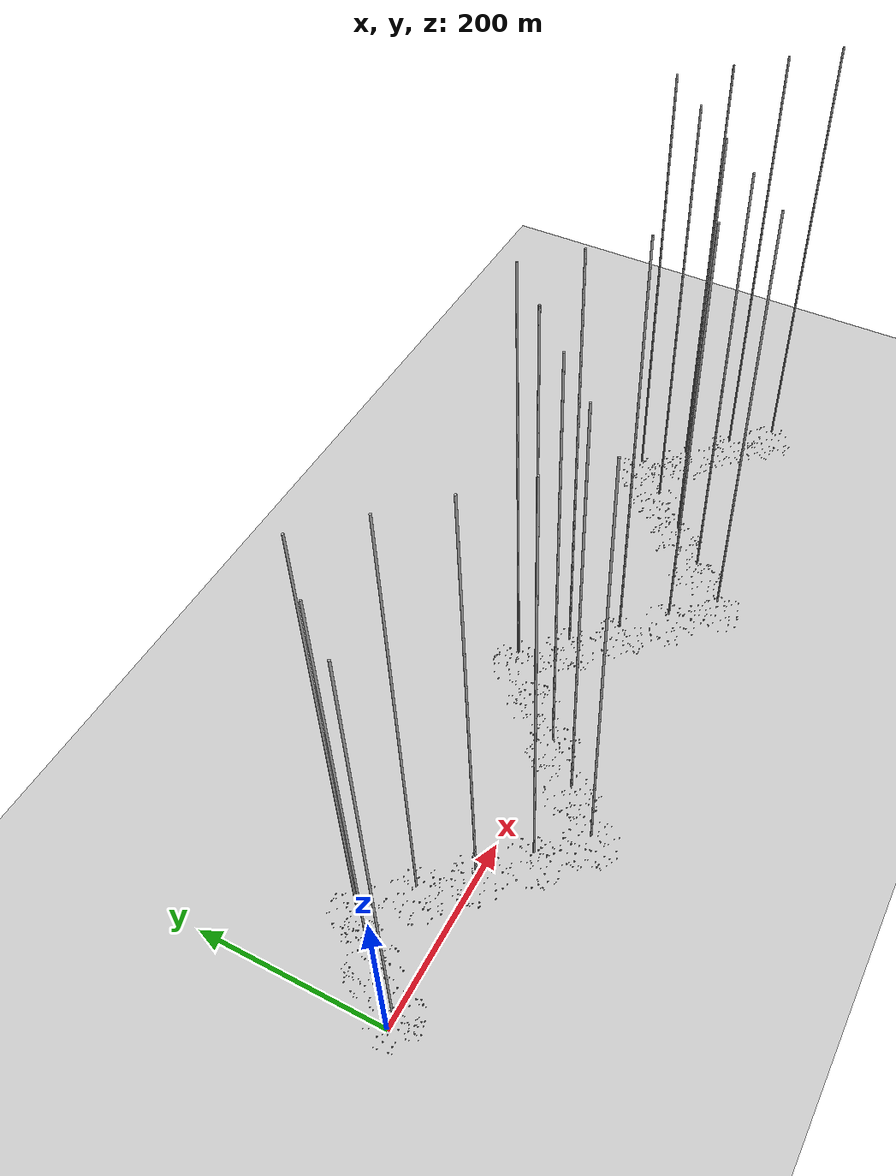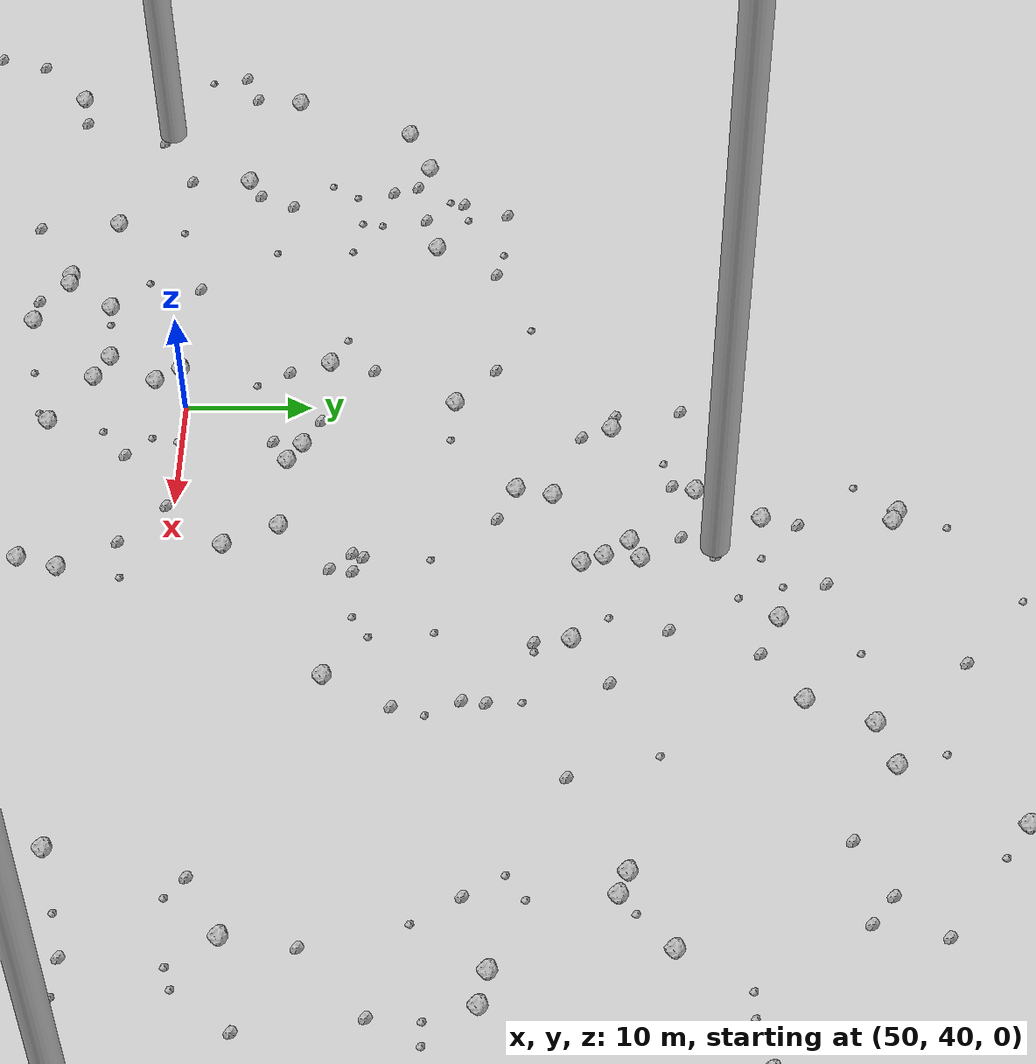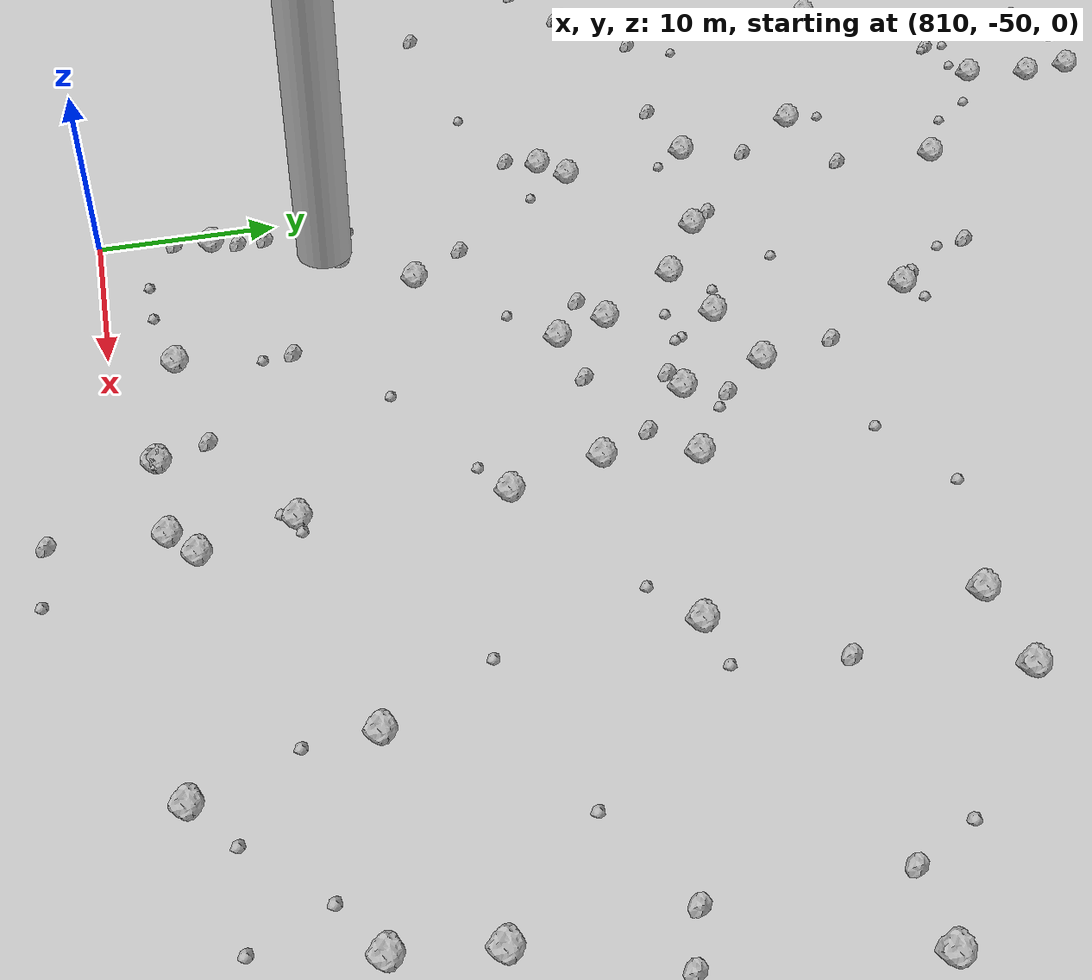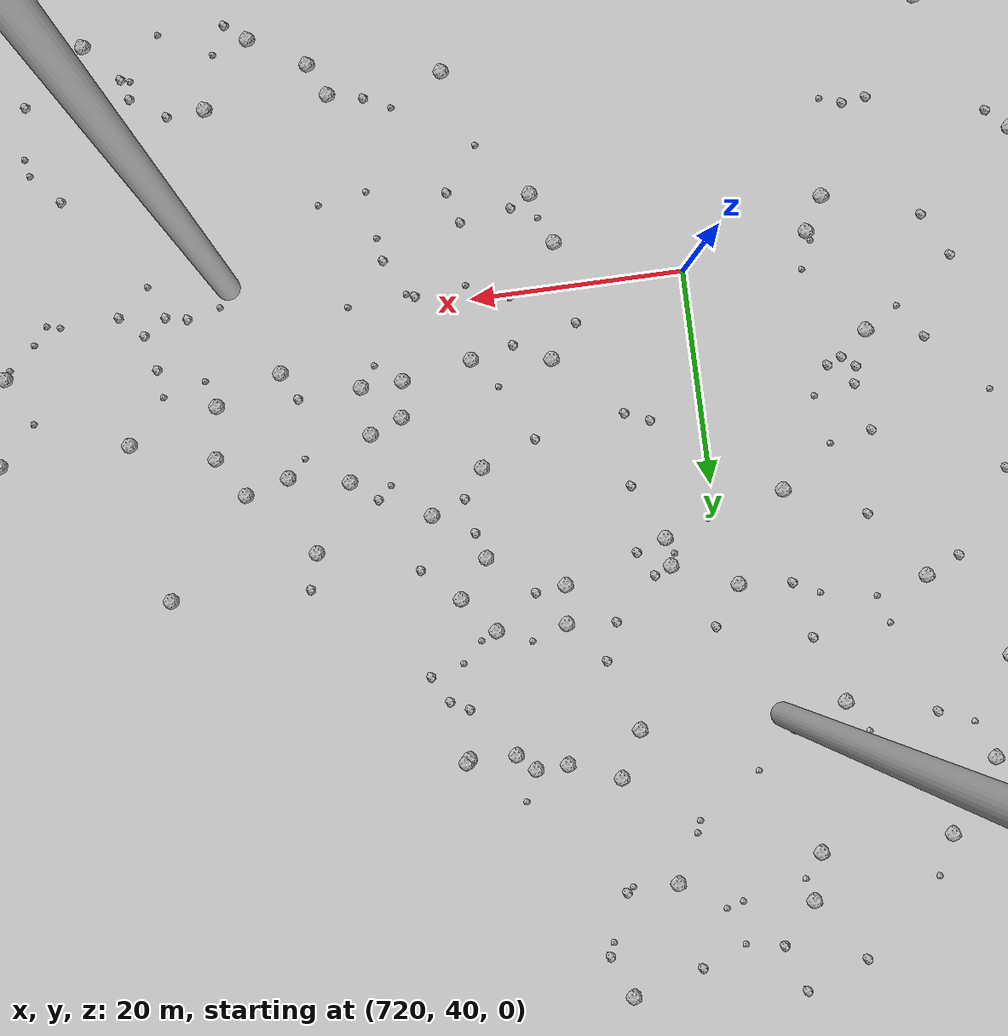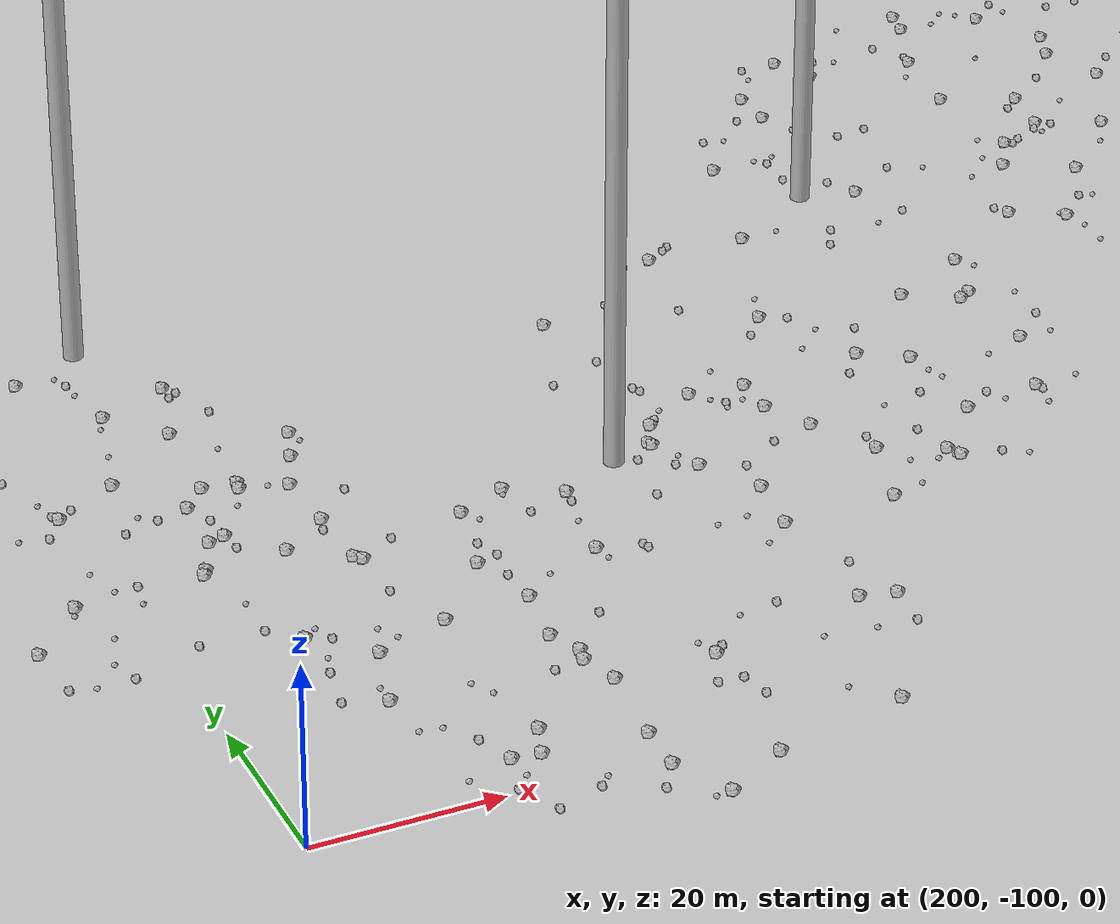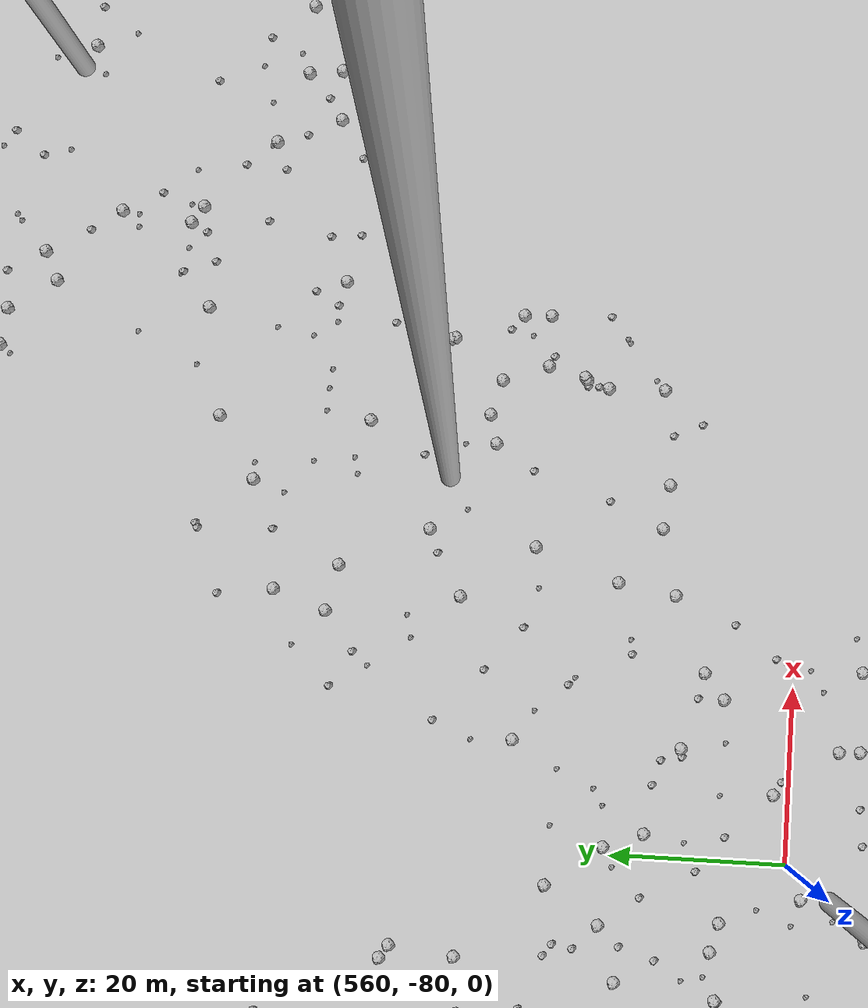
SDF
<sdf version="1.6">
 <world name="default">
  <include><uri>model://custom_ground</uri></include>
  <include><uri>model://sun</uri></include>
  <spherical_coordinates>
   <surface_model>EARTH_WGS84</surface_model>
   <latitude_deg>38.161479</latitude_deg>
   <longitude_deg>-122.454630</longitude_deg>
   <elevation>488.0</elevation>
   <heading_deg>90</heading_deg>
  </spherical_coordinates>
  <model name="rock1_0_0">
   <include><uri>model://rock1</uri><pose>14.003152754416249 -19.172089309877126 0.5 0 0 0</pose></include>
  </model>
  <model name="rock1_0_1">
   <include><uri>model://rock1</uri><pose>-10.769497221475962 -1.6153621248733714 0.5 0 0 0</pose></include>
  </model>
  <model name="rock1_0_2">
   <include><uri>model://rock1</uri><pose>-9.219295211612037 5.029225498820701 0.5 0 0 0</pose></include>
  </model>
  <model name="rock1_0_3">
   <include><uri>model://rock1</uri><pose>26.798721019652056 -6.222210888823977 0.5 0 0 0</pose></include>
  </model>
  <model name="rock1_0_4">
   <include><uri>model://rock1</uri><pose>-16.409507815319724 -10.679864082211793 0.5 0 0 0</pose></include>
  </model>
  <model name="rock1_0_5">
   <include><uri>model://rock1</uri><pose>21.055822012386884 -24.901092174642812 0.5 0 0 0</pose></include>
  </model>
  <model name="rock1_0_6">
   <include><uri>model://rock1</uri><pose>34.85470821379378 -7.82175812655511 0.5 0 0 0</pose></include>
  </model>
  <model name="rock1_0_7">
   <include><uri>model://rock1</uri><pose>7.269582818066841 -16.510152945980835 0.5 0 0 0</pose></include>
  </model>
  <model name="rock1_0_8">
   <include><uri>model://rock1</uri><pose>37.43791030881973 -2.932541775579651 0.5 0 0 0</pose></include>
  </model>
  <model name="rock1_0_9">
   <include><uri>model://rock1</uri><pose>21.78607754828959 19.998094251555756 0.5 0 0 0</pose></include>
  </model>
  <model name="rock1_0_10">
   <include><uri>model://rock1</uri><pose>30.75779689441147 12.34537848764922 0.5 0 0 0</pose></include>
  </model>
  <model name="rock1_0_11">
   <include><uri>model://rock1</uri><pose>33.23190222995296 -15.998293530328434 0.5 0 0 0</pose></include>
  </model>
  <model name="rock1_0_12">
   <include><uri>model://rock1</uri><pose>-10.50353050738606 -11.117603569233875 0.5 0 0 0</pose></include>
  </model>
  <model name="rock1_0_13">
   <include><uri>model://rock1</uri><pose>16.944692215354152 -25.94789619877936 0.5 0 0 0</pose></include>
  </model>
  <model name="rock1_0_14">
   <include><uri>model://rock1</uri><pose>-6.054517044995237 -11.423847118010645 0.5 0 0 0</pose></include>
  </model>
  <model name="rock1_0_15">
   <include><uri>model://rock1</uri><pose>7.972226254529836 -22.481924310800768 0.5 0 0 0</pose></include>
  </model>
  <model name="rock1_0_16">
   <include><uri>model://rock1</uri><pose>29.67631738772043 -0.6907466967468707 0.5 0 0 0</pose></include>
  </model>
  <model name="rock1_0_17">
   <include><uri>model://rock1</uri><pose>19.588181543198026 -22.6142936922495 0.5 0 0 0</pose></include>
  </model>
  <model name="rock1_0_18">
   <include><uri>model://rock1</uri><pose>35.79826095948114 11.627722984927736 0.5 0 0 0</pose></include>
  </model>
  <model name="rock1_0_19">
   <include><uri>model://rock1</uri><pose>11.194022819033098 -7.799987242348646 0.5 0 0 0</pose></include>
  </model>
  <model name="rock1_0_20">
   <include><uri>model://rock1</uri><pose>7.173253872946997 1.4170511199053806 0.5 0 0 0</pose></include>
  </model>
  <model name="rock1_0_21">
   <include><uri>model://rock1</uri><pose>4.626203410921704 -8.291863220499462 0.5 0 0 0</pose></include>
  </model>
  <model name="rock1_0_22">
   <include><uri>model://rock1</uri><pose>9.550269785202008 -27.939003110961423 0.5 0 0 0</pose></include>
  </model>
  <model name="rock1_0_23">
   <include><uri>model://rock1</uri><pose>36.696982578919226 -12.739101668206189 0.5 0 0 0</pose></include>
  </model>
  <model name="rock1_0_24">
   <include><uri>model://rock1</uri><pose>1.812405688505244 6.779470506799619 0.5 0 0 0</pose></include>
  </model>
  <model name="rock1_0_25">
   <include><uri>model://rock1</uri><pose>19.525953290873247 4.636568248175415 0.5 0 0 0</pose></include>
  </model>
  <model name="rock1_0_26">
   <include><uri>model://rock1</uri><pose>0.4283806910543895 -17.83017192072367 0.5 0 0 0</pose></include>
  </model>
  <model name="rock2_0_0">
   <include><uri>model://rock2</uri><pose>22.115333299509828 -18.475516153143587 0.3 0 0 0</pose></include>
  </model>
  <model name="rock2_0_1">
   <include><uri>model://rock2</uri><pose>9.296399754992926 20.259388664598745 0.3 0 0 0</pose></include>
  </model>
  <model name="rock2_0_2">
   <include><uri>model://rock2</uri><pose>2.6312842386152084 -2.528047752219152 0.3 0 0 0</pose></include>
  </model>
  <model name="rock2_0_3">
   <include><uri>model://rock2</uri><pose>16.862816089835718 -7.390283353298976 0.3 0 0 0</pose></include>
  </model>
  <model name="rock2_0_4">
   <include><uri>model://rock2</uri><pose>18.973475793024406 6.493884570623841 0.3 0 0 0</pose></include>
  </model>
  <model name="rock2_0_5">
   <include><uri>model://rock2</uri><pose>15.210191729259876 -20.2191616102443 0.3 0 0 0</pose></include>
  </model>
  <model name="rock2_0_6">
   <include><uri>model://rock2</uri><pose>3.344012177440643 12.772946332731607 0.3 0 0 0</pose></include>
  </model>
  <model name="rock2_0_7">
   <include><uri>model://rock2</uri><pose>17.459570901677466 28.67395238107705 0.3 0 0 0</pose></include>
  </model>
  <model name="rock2_0_8">
   <include><uri>model://rock2</uri><pose>7.583410609726428 -24.6860163267105 0.3 0 0 0</pose></include>
  </model>
  <model name="rock2_0_9">
   <include><uri>model://rock2</uri><pose>11.540274373922912 5.612574066023626 0.3 0 0 0</pose></include>
  </model>
  <model name="rock2_0_10">
   <include><uri>model://rock2</uri><pose>31.526264110691855 -12.830426750431883 0.3 0 0 0</pose></include>
  </model>
  <model name="rock2_0_11">
   <include><uri>model://rock2</uri><pose>-3.623604083262105 -2.113262353885318 0.3 0 0 0</pose></include>
  </model>
  <model name="rock2_0_12">
   <include><uri>model://rock2</uri><pose>13.806293932558418 -12.044869276532594 0.3 0 0 0</pose></include>
  </model>
  <model name="rock2_0_13">
   <include><uri>model://rock2</uri><pose>4.001837810359202 -14.59295799486269 0.3 0 0 0</pose></include>
  </model>
  <model name="rock2_0_14">
   <include><uri>model://rock2</uri><pose>14.307886913518352 -21.939365525578815 0.3 0 0 0</pose></include>
  </model>
  <model name="rock2_0_15">
   <include><uri>model://rock2</uri><pose>-5.25988311911183 2.222010134946757 0.3 0 0 0</pose></include>
  </model>
  <model name="rock2_0_16">
   <include><uri>model://rock2</uri><pose>-18.044376271620685 -0.23067712467892676 0.3 0 0 0</pose></include>
  </model>
  <model name="rock2_0_17">
   <include><uri>model://rock2</uri><pose>-8.84563420867927 19.3418294086091 0.3 0 0 0</pose></include>
  </model>
  <model name="rock2_0_18">
   <include><uri>model://rock2</uri><pose>17.253158023210958 -5.286549872726731 0.3 0 0 0</pose></include>
  </model>
  <model name="rock2_0_19">
   <include><uri>model://rock2</uri><pose>9.074251532045952 -21.188228978142877 0.3 0 0 0</pose></include>
  </model>
  <model name="rock2_0_20">
   <include><uri>model://rock2</uri><pose>12.36185200655627 -2.8801964644880726 0.3 0 0 0</pose></include>
  </model>
  <model name="rock2_0_21">
   <include><uri>model://rock2</uri><pose>12.608125451565002 -14.039496326869124 0.3 0 0 0</pose></include>
  </model>
  <model name="rock2_0_22">
   <include><uri>model://rock2</uri><pose>9.448101055206397 -15.81849575716401 0.3 0 0 0</pose></include>
  </model>
  <model name="rock2_0_23">
   <include><uri>model://rock2</uri><pose>-6.128046957912275 15.135694417246341 0.3 0 0 0</pose></include>
  </model>
  <model name="rock2_0_24">
   <include><uri>model://rock2</uri><pose>35.145760665350885 -8.98308375169989 0.3 0 0 0</pose></include>
  </model>
  <model name="rock2_0_25">
   <include><uri>model://rock2</uri><pose>4.394007097871974 -1.4110272061156586 0.3 0 0 0</pose></include>
  </model>
  <model name="rock2_0_26">
   <include><uri>model://rock2</uri><pose>10.318676752546448 24.19888108340242 0.3 0 0 0</pose></include>
  </model>
  <model name="rock3_0_0">
   <include><uri>model://rock3</uri><pose>19.790943797819182 6.389377425410096 0.2 0 0 0</pose></include>
  </model>
  <model name="rock3_0_1">
   <include><uri>model://rock3</uri><pose>4.416686359396746 7.112292163795942 0.2 0 0 0</pose></include>
  </model>
  <model name="rock3_0_2">
   <include><uri>model://rock3</uri><pose>32.1236234990863 -19.12061555949971 0.2 0 0 0</pose></include>
  </model>
  <model name="rock3_0_3">
   <include><uri>model://rock3</uri><pose>4.551588826758671 -22.84134099825445 0.2 0 0 0</pose></include>
  </model>
  <model name="rock3_0_4">
   <include><uri>model://rock3</uri><pose>0.8661424117122749 -21.276999499638055 0.2 0 0 0</pose></include>
  </model>
  <model name="rock3_0_5">
   <include><uri>model://rock3</uri><pose>-18.13497089999223 3.3366880043515295 0.2 0 0 0</pose></include>
  </model>
  <model name="rock3_0_6">
   <include><uri>model://rock3</uri><pose>33.55236873281782 -1.077258993307236 0.2 0 0 0</pose></include>
  </model>
  <model name="rock3_0_7">
   <include><uri>model://rock3</uri><pose>34.43744886997728 -15.83802587019109 0.2 0 0 0</pose></include>
  </model>
  <model name="rock3_0_8">
   <include><uri>model://rock3</uri><pose>4.245208825331023 -28.341628746355468 0.2 0 0 0</pose></include>
  </model>
  <model name="rock3_0_9">
   <include><uri>model://rock3</uri><pose>12.91722233113461 11.578956316169595 0.2 0 0 0</pose></include>
  </model>
  <model name="rock3_0_10">
   <include><uri>model://rock3</uri><pose>-1.8823550049596527 6.952105621658063 0.2 0 0 0</pose></include>
  </model>
  <model name="rock3_0_11">
   <include><uri>model://rock3</uri><pose>-14.513603709753827 8.026346856073658 0.2 0 0 0</pose></include>
  </model>
  <model name="rock3_0_12">
   <include><uri>model://rock3</uri><pose>3.729048708964868 0.22956325164224012 0.2 0 0 0</pose></include>
  </model>
  <model name="rock3_0_13">
   <include><uri>model://rock3</uri><pose>15.241731696289676 7.542228117051842 0.2 0 0 0</pose></include>
  </model>
  <model name="rock3_0_14">
   <include><uri>model://rock3</uri><pose>32.61420224036152 -19.248009081515512 0.2 0 0 0</pose></include>
  </model>
  <model name="rock3_0_15">
   <include><uri>model://rock3</uri><pose>32.58156144908877 19.441626464152158 0.2 0 0 0</pose></include>
  </model>
  <model name="rock3_0_16">
   <include><uri>model://rock3</uri><pose>11.93910076311813 -10.282394790837827 0.2 0 0 0</pose></include>
  </model>
  <model name="rock3_0_17">
   <include><uri>model://rock3</uri><pose>18.88404008414475 -16.944750297750748 0.2 0 0 0</pose></include>
  </model>
  <model name="rock3_0_18">
   <include><uri>model://rock3</uri><pose>-1.9463426805926787 16.987252190907448 0.2 0 0 0</pose></include>
  </model>
  <model name="rock3_0_19">
   <include><uri>model://rock3</uri><pose>-4.987003157869873 14.807195456027436 0.2 0 0 0</pose></include>
  </model>
  <model name="rock3_0_20">
   <include><uri>model://rock3</uri><pose>36.30333780950231 5.204504972045356 0.2 0 0 0</pose></include>
  </model>
  <model name="rock3_0_21">
   <include><uri>model://rock3</uri><pose>1.0702225226962732 -11.071623665225555 0.2 0 0 0</pose></include>
  </model>
  <model name="rock3_0_22">
   <include><uri>model://rock3</uri><pose>0.9543686848988528 3.4386424257805714 0.2 0 0 0</pose></include>
  </model>
  <model name="rock3_0_23">
   <include><uri>model://rock3</uri><pose>20.299312278287942 2.97876913034667 0.2 0 0 0</pose></include>
  </model>
  <model name="rock3_0_24">
   <include><uri>model://rock3</uri><pose>27.976497329939605 -23.508628566801118 0.2 0 0 0</pose></include>
  </model>
  <model name="rock3_0_25">
   <include><uri>model://rock3</uri><pose>19.92093955956686 -18.373246192790923 0.2 0 0 0</pose></include>
  </model>
  <model name="rock3_0_26">
   <include><uri>model://rock3</uri><pose>-16.292038133426505 -14.06913415658437 0.2 0 0 0</pose></include>
  </model>
  <model name="rock1_1_0">
   <include><uri>model://rock1</uri><pose>45.53403351159595 51.18173014442321 0.5 0 0 0</pose></include>
  </model>
  <model name="rock1_1_1">
   <include><uri>model://rock1</uri><pose>35.9719522734614 29.341820308086028 0.5 0 0 0</pose></include>
  </model>
  <model name="rock1_1_2">
   <include><uri>model://rock1</uri><pose>18.681746049818514 56.55375117307958 0.5 0 0 0</pose></include>
  </model>
  <model name="rock1_1_3">
   <include><uri>model://rock1</uri><pose>51.95205193717821 29.281695005223767 0.5 0 0 0</pose></include>
  </model>
  <model name="rock1_1_4">
   <include><uri>model://rock1</uri><pose>65.80925344993976 28.543044913939184 0.5 0 0 0</pose></include>
  </model>
  <model name="rock1_1_5">
   <include><uri>model://rock1</uri><pose>32.43372469017588 59.334673469813815 0.5 0 0 0</pose></include>
  </model>
  <model name="rock1_1_6">
   <include><uri>model://rock1</uri><pose>46.267485076221995 39.2405049523154 0.5 0 0 0</pose></include>
  </model>
  <model name="rock1_1_7">
   <include><uri>model://rock1</uri><pose>40.74991383684626 22.805485984880267 0.5 0 0 0</pose></include>
  </model>
  <model name="rock1_1_8">
   <include><uri>model://rock1</uri><pose>41.10723128931339 26.815783487591226 0.5 0 0 0</pose></include>
  </model>
  <model name="rock1_1_9">
   <include><uri>model://rock1</uri><pose>52.05726798718982 15.094294407876443 0.5 0 0 0</pose></include>
  </model>
  <model name="rock1_1_10">
   <include><uri>model://rock1</uri><pose>53.49698628460962 19.097372245101713 0.5 0 0 0</pose></include>
  </model>
  <model name="rock1_1_11">
   <include><uri>model://rock1</uri><pose>29.914524056261513 32.64164741150813 0.5 0 0 0</pose></include>
  </model>
  <model name="rock1_1_12">
   <include><uri>model://rock1</uri><pose>66.69566566127833 31.65152129666201 0.5 0 0 0</pose></include>
  </model>
  <model name="rock1_1_13">
   <include><uri>model://rock1</uri><pose>39.57108128247053 32.95291081273528 0.5 0 0 0</pose></include>
  </model>
  <model name="rock1_1_14">
   <include><uri>model://rock1</uri><pose>45.06622769819851 33.4583937773297 0.5 0 0 0</pose></include>
  </model>
  <model name="rock1_1_15">
   <include><uri>model://rock1</uri><pose>36.90698227649406 29.305425181353243 0.5 0 0 0</pose></include>
  </model>
  <model name="rock1_1_16">
   <include><uri>model://rock1</uri><pose>55.850692218608 48.367047390588496 0.5 0 0 0</pose></include>
  </model>
  <model name="rock1_1_17">
   <include><uri>model://rock1</uri><pose>14.787433270223811 46.87793330584786 0.5 0 0 0</pose></include>
  </model>
  <model name="rock1_1_18">
   <include><uri>model://rock1</uri><pose>22.936737540867348 58.404066459316546 0.5 0 0 0</pose></include>
  </model>
  <model name="rock1_1_19">
   <include><uri>model://rock1</uri><pose>47.569272852404936 37.315105910173884 0.5 0 0 0</pose></include>
  </model>
  <model name="rock1_1_20">
   <include><uri>model://rock1</uri><pose>24.64594973507829 43.17400424289459 0.5 0 0 0</pose></include>
  </model>
  <model name="rock1_1_21">
   <include><uri>model://rock1</uri><pose>47.28075500165118 32.3570630522852 0.5 0 0 0</pose></include>
  </model>
  <model name="rock1_1_22">
   <include><uri>model://rock1</uri><pose>54.12460849913178 49.47087358286408 0.5 0 0 0</pose></include>
  </model>
  <model name="rock1_1_23">
   <include><uri>model://rock1</uri><pose>49.676091055491035 61.310228926001656 0.5 0 0 0</pose></include>
  </model>
  <model name="rock1_1_24">
   <include><uri>model://rock1</uri><pose>62.43378801227862 48.160410898547894 0.5 0 0 0</pose></include>
  </model>
  <model name="rock1_1_25">
   <include><uri>model://rock1</uri><pose>14.619704220333151 28.099342127706745 0.5 0 0 0</pose></include>
  </model>
  <model name="rock1_1_26">
   <include><uri>model://rock1</uri><pose>64.37913657748126 43.98949637721336 0.5 0 0 0</pose></include>
  </model>
  <model name="rock2_1_0">
   <include><uri>model://rock2</uri><pose>38.83048372370382 27.074732717874706 0.3 0 0 0</pose></include>
  </model>
  <model name="rock2_1_1">
   <include><uri>model://rock2</uri><pose>46.04739209951017 64.4913164804986 0.3 0 0 0</pose></include>
  </model>
  <model name="rock2_1_2">
   <include><uri>model://rock2</uri><pose>19.7828205899732 35.59856334637793 0.3 0 0 0</pose></include>
  </model>
  <model name="rock2_1_3">
   <include><uri>model://rock2</uri><pose>25.7816033954493 55.48881631167406 0.3 0 0 0</pose></include>
  </model>
  <model name="rock2_1_4">
   <include><uri>model://rock2</uri><pose>28.358492347405114 65.12012935132131 0.3 0 0 0</pose></include>
  </model>
  <model name="rock2_1_5">
   <include><uri>model://rock2</uri><pose>60.44870937305133 39.39468659527579 0.3 0 0 0</pose></include>
  </model>
  <model name="rock2_1_6">
   <include><uri>model://rock2</uri><pose>29.032532915306138 58.3556579861774 0.3 0 0 0</pose></include>
  </model>
  <model name="rock2_1_7">
   <include><uri>model://rock2</uri><pose>27.504929026187817 47.11066569359798 0.3 0 0 0</pose></include>
  </model>
  <model name="rock2_1_8">
   <include><uri>model://rock2</uri><pose>37.3047280446288 40.12931345277454 0.3 0 0 0</pose></include>
  </model>
  <model name="rock2_1_9">
   <include><uri>model://rock2</uri><pose>26.290888980484755 44.28247804311099 0.3 0 0 0</pose></include>
  </model>
  <model name="rock2_1_10">
   <include><uri>model://rock2</uri><pose>35.346445482981025 64.32962092829234 0.3 0 0 0</pose></include>
  </model>
  <model name="rock2_1_11">
   <include><uri>model://rock2</uri><pose>64.08388475495137 36.02759106773043 0.3 0 0 0</pose></include>
  </model>
  <model name="rock2_1_12">
   <include><uri>model://rock2</uri><pose>53.80073952590885 47.17434114686356 0.3 0 0 0</pose></include>
  </model>
  <model name="rock2_1_13">
   <include><uri>model://rock2</uri><pose>24.610609699880285 38.34685623604064 0.3 0 0 0</pose></include>
  </model>
  <model name="rock2_1_14">
   <include><uri>model://rock2</uri><pose>11.545222966697615 42.02855610300807 0.3 0 0 0</pose></include>
  </model>
  <model name="rock2_1_15">
   <include><uri>model://rock2</uri><pose>27.10379478339523 61.45275068829807 0.3 0 0 0</pose></include>
  </model>
  <model name="rock2_1_16">
   <include><uri>model://rock2</uri><pose>14.259390374849216 43.18615673215941 0.3 0 0 0</pose></include>
  </model>
  <model name="rock2_1_17">
   <include><uri>model://rock2</uri><pose>40.99995523415883 19.018505952075117 0.3 0 0 0</pose></include>
  </model>
  <model name="rock2_1_18">
   <include><uri>model://rock2</uri><pose>51.60823805299818 50.80209557383974 0.3 0 0 0</pose></include>
  </model>
  <model name="rock2_1_19">
   <include><uri>model://rock2</uri><pose>25.118724271744327 57.509005654317235 0.3 0 0 0</pose></include>
  </model>
  <model name="rock2_1_20">
   <include><uri>model://rock2</uri><pose>30.38355705789383 26.177268996809584 0.3 0 0 0</pose></include>
  </model>
  <model name="rock2_1_21">
   <include><uri>model://rock2</uri><pose>65.02030150240606 53.92741154030329 0.3 0 0 0</pose></include>
  </model>
  <model name="rock2_1_22">
   <include><uri>model://rock2</uri><pose>55.31485011139816 35.71890002422659 0.3 0 0 0</pose></include>
  </model>
  <model name="rock2_1_23">
   <include><uri>model://rock2</uri><pose>46.48637045764857 48.03195972113849 0.3 0 0 0</pose></include>
  </model>
  <model name="rock2_1_24">
   <include><uri>model://rock2</uri><pose>46.205640513533616 54.77638902577189 0.3 0 0 0</pose></include>
  </model>
  <model name="rock2_1_25">
   <include><uri>model://rock2</uri><pose>66.51349575582458 52.28204716815751 0.3 0 0 0</pose></include>
  </model>
  <model name="rock2_1_26">
   <include><uri>model://rock2</uri><pose>65.37587699292362 54.776376754222326 0.3 0 0 0</pose></include>
  </model>
  <model name="rock3_1_0">
   <include><uri>model://rock3</uri><pose>52.789480488377514 33.70656732621661 0.2 0 0 0</pose></include>
  </model>
  <model name="rock3_1_1">
   <include><uri>model://rock3</uri><pose>32.92262558403607 64.86515174144441 0.2 0 0 0</pose></include>
  </model>
  <model name="rock3_1_2">
   <include><uri>model://rock3</uri><pose>29.33682530221537 52.996513719795956 0.2 0 0 0</pose></include>
  </model>
  <model name="rock3_1_3">
   <include><uri>model://rock3</uri><pose>26.711785883797482 60.26827754094138 0.2 0 0 0</pose></include>
  </model>
  <model name="rock3_1_4">
   <include><uri>model://rock3</uri><pose>11.999525474585377 39.098846167653875 0.2 0 0 0</pose></include>
  </model>
  <model name="rock3_1_5">
   <include><uri>model://rock3</uri><pose>36.49594196361771 35.845079897051384 0.2 0 0 0</pose></include>
  </model>
  <model name="rock3_1_6">
   <include><uri>model://rock3</uri><pose>32.65924679107471 52.346382658553104 0.2 0 0 0</pose></include>
  </model>
  <model name="rock3_1_7">
   <include><uri>model://rock3</uri><pose>42.46969337399177 23.338487307949684 0.2 0 0 0</pose></include>
  </model>
  <model name="rock3_1_8">
   <include><uri>model://rock3</uri><pose>45.21014105637217 12.868087476256523 0.2 0 0 0</pose></include>
  </model>
  <model name="rock3_1_9">
   <include><uri>model://rock3</uri><pose>54.52911214810782 19.09796220379816 0.2 0 0 0</pose></include>
  </model>
  <model name="rock3_1_10">
   <include><uri>model://rock3</uri><pose>67.40227529853053 36.467732568365975 0.2 0 0 0</pose></include>
  </model>
  <model name="rock3_1_11">
   <include><uri>model://rock3</uri><pose>26.23009685149415 52.426836895946174 0.2 0 0 0</pose></include>
  </model>
  <model name="rock3_1_12">
   <include><uri>model://rock3</uri><pose>29.55845331233442 54.64650639669705 0.2 0 0 0</pose></include>
  </model>
  <model name="rock3_1_13">
   <include><uri>model://rock3</uri><pose>30.631860921710874 38.154636880366354 0.2 0 0 0</pose></include>
  </model>
  <model name="rock3_1_14">
   <include><uri>model://rock3</uri><pose>24.90533643596104 50.29830940841621 0.2 0 0 0</pose></include>
  </model>
  <model name="rock3_1_15">
   <include><uri>model://rock3</uri><pose>47.76400319943766 45.47846764570143 0.2 0 0 0</pose></include>
  </model>
  <model name="rock3_1_16">
   <include><uri>model://rock3</uri><pose>53.760105095653614 39.61003925858334 0.2 0 0 0</pose></include>
  </model>
  <model name="rock3_1_17">
   <include><uri>model://rock3</uri><pose>53.32640762251543 61.038117042584815 0.2 0 0 0</pose></include>
  </model>
  <model name="rock3_1_18">
   <include><uri>model://rock3</uri><pose>32.88248492915526 46.085352418851066 0.2 0 0 0</pose></include>
  </model>
  <model name="rock3_1_19">
   <include><uri>model://rock3</uri><pose>28.83772513216956 61.8346391328161 0.2 0 0 0</pose></include>
  </model>
  <model name="rock3_1_20">
   <include><uri>model://rock3</uri><pose>61.312664590725156 23.485868899357726 0.2 0 0 0</pose></include>
  </model>
  <model name="rock3_1_21">
   <include><uri>model://rock3</uri><pose>50.91023286961855 28.44922322581733 0.2 0 0 0</pose></include>
  </model>
  <model name="rock3_1_22">
   <include><uri>model://rock3</uri><pose>53.42409644352798 37.61497389864785 0.2 0 0 0</pose></include>
  </model>
  <model name="rock3_1_23">
   <include><uri>model://rock3</uri><pose>42.764744666798215 52.45476584084156 0.2 0 0 0</pose></include>
  </model>
  <model name="rock3_1_24">
   <include><uri>model://rock3</uri><pose>41.45912786815808 67.2335089073937 0.2 0 0 0</pose></include>
  </model>
  <model name="rock3_1_25">
   <include><uri>model://rock3</uri><pose>46.59413520554491 27.537451571037817 0.2 0 0 0</pose></include>
  </model>
  <model name="rock3_1_26">
   <include><uri>model://rock3</uri><pose>41.24633998529451 33.08705980104841 0.2 0 0 0</pose></include>
  </model>
  <model name="rock1_2_0">
   <include><uri>model://rock1</uri><pose>65.32037074465723 75.75455488585938 0.5 0 0 0</pose></include>
  </model>
  <model name="rock1_2_1">
   <include><uri>model://rock1</uri><pose>70.89690024471373 85.96924514362827 0.5 0 0 0</pose></include>
  </model>
  <model name="rock1_2_2">
   <include><uri>model://rock1</uri><pose>78.39345835402338 87.54000209279442 0.5 0 0 0</pose></include>
  </model>
  <model name="rock1_2_3">
   <include><uri>model://rock1</uri><pose>109.55326423801435 80.23516884283453 0.5 0 0 0</pose></include>
  </model>
  <model name="rock1_2_4">
   <include><uri>model://rock1</uri><pose>84.12969675585569 93.86876973610964 0.5 0 0 0</pose></include>
  </model>
  <model name="rock1_2_5">
   <include><uri>model://rock1</uri><pose>79.55827262090348 108.38147721419132 0.5 0 0 0</pose></include>
  </model>
  <model name="rock1_2_6">
   <include><uri>model://rock1</uri><pose>61.29540161380639 85.03373162251778 0.5 0 0 0</pose></include>
  </model>
  <model name="rock1_2_7">
   <include><uri>model://rock1</uri><pose>61.428210514295 95.08124979432125 0.5 0 0 0</pose></include>
  </model>
  <model name="rock1_2_8">
   <include><uri>model://rock1</uri><pose>95.19626210552067 73.8446198308979 0.5 0 0 0</pose></include>
  </model>
  <model name="rock1_2_9">
   <include><uri>model://rock1</uri><pose>58.5482077096453 80.04471548727903 0.5 0 0 0</pose></include>
  </model>
  <model name="rock1_2_10">
   <include><uri>model://rock1</uri><pose>63.62924003019196 74.94682082678864 0.5 0 0 0</pose></include>
  </model>
  <model name="rock1_2_11">
   <include><uri>model://rock1</uri><pose>73.06318852591636 70.53797305611629 0.5 0 0 0</pose></include>
  </model>
  <model name="rock1_2_12">
   <include><uri>model://rock1</uri><pose>58.56082992412409 66.23137245101216 0.5 0 0 0</pose></include>
  </model>
  <model name="rock1_2_13">
   <include><uri>model://rock1</uri><pose>101.31464422348212 64.93401308268149 0.5 0 0 0</pose></include>
  </model>
  <model name="rock1_2_14">
   <include><uri>model://rock1</uri><pose>108.76915448831755 83.91812648426722 0.5 0 0 0</pose></include>
  </model>
  <model name="rock1_2_15">
   <include><uri>model://rock1</uri><pose>104.03260665396168 64.3451883797764 0.5 0 0 0</pose></include>
  </model>
  <model name="rock1_2_16">
   <include><uri>model://rock1</uri><pose>93.30433353949641 74.52662813246081 0.5 0 0 0</pose></include>
  </model>
  <model name="rock1_2_17">
   <include><uri>model://rock1</uri><pose>80.42683343318382 92.56409917083214 0.5 0 0 0</pose></include>
  </model>
  <model name="rock1_2_18">
   <include><uri>model://rock1</uri><pose>65.81651546780856 71.28349499311597 0.5 0 0 0</pose></include>
  </model>
  <model name="rock1_2_19">
   <include><uri>model://rock1</uri><pose>89.0877143409119 102.81329186330379 0.5 0 0 0</pose></include>
  </model>
  <model name="rock1_2_20">
   <include><uri>model://rock1</uri><pose>87.08228899849853 108.39132817461717 0.5 0 0 0</pose></include>
  </model>
  <model name="rock1_2_21">
   <include><uri>model://rock1</uri><pose>65.1123232010964 73.00352177849341 0.5 0 0 0</pose></include>
  </model>
  <model name="rock1_2_22">
   <include><uri>model://rock1</uri><pose>52.27809193373583 73.6406909494101 0.5 0 0 0</pose></include>
  </model>
  <model name="rock1_2_23">
   <include><uri>model://rock1</uri><pose>60.50904311687285 95.49952909290491 0.5 0 0 0</pose></include>
  </model>
  <model name="rock1_2_24">
   <include><uri>model://rock1</uri><pose>99.51557785487374 77.68361187932277 0.5 0 0 0</pose></include>
  </model>
  <model name="rock1_2_25">
   <include><uri>model://rock1</uri><pose>59.14160363700083 69.06962491026808 0.5 0 0 0</pose></include>
  </model>
  <model name="rock1_2_26">
   <include><uri>model://rock1</uri><pose>76.62567000846718 52.2856685926442 0.5 0 0 0</pose></include>
  </model>
  <model name="rock2_2_0">
   <include><uri>model://rock2</uri><pose>61.84619074062364 87.8301221117132 0.3 0 0 0</pose></include>
  </model>
  <model name="rock2_2_1">
   <include><uri>model://rock2</uri><pose>50.91089041376223 73.95925569925377 0.3 0 0 0</pose></include>
  </model>
  <model name="rock2_2_2">
   <include><uri>model://rock2</uri><pose>63.112684905530955 78.91569863144301 0.3 0 0 0</pose></include>
  </model>
  <model name="rock2_2_3">
   <include><uri>model://rock2</uri><pose>76.98720050600522 73.3845118022738 0.3 0 0 0</pose></include>
  </model>
  <model name="rock2_2_4">
   <include><uri>model://rock2</uri><pose>61.500381411155786 64.8642262067239 0.3 0 0 0</pose></include>
  </model>
  <model name="rock2_2_5">
   <include><uri>model://rock2</uri><pose>95.38030511716144 63.06737640813204 0.3 0 0 0</pose></include>
  </model>
  <model name="rock2_2_6">
   <include><uri>model://rock2</uri><pose>97.27601816698659 91.28624989834556 0.3 0 0 0</pose></include>
  </model>
  <model name="rock2_2_7">
   <include><uri>model://rock2</uri><pose>78.6923562252681 62.57253291125836 0.3 0 0 0</pose></include>
  </model>
  <model name="rock2_2_8">
   <include><uri>model://rock2</uri><pose>82.5721717831704 108.01558262724005 0.3 0 0 0</pose></include>
  </model>
  <model name="rock2_2_9">
   <include><uri>model://rock2</uri><pose>79.29820288966661 57.462228800343496 0.3 0 0 0</pose></include>
  </model>
  <model name="rock2_2_10">
   <include><uri>model://rock2</uri><pose>66.73734960123492 54.037999559163886 0.3 0 0 0</pose></include>
  </model>
  <model name="rock2_2_11">
   <include><uri>model://rock2</uri><pose>73.31369102994037 67.79296317908566 0.3 0 0 0</pose></include>
  </model>
  <model name="rock2_2_12">
   <include><uri>model://rock2</uri><pose>90.50237725335862 90.3568874724962 0.3 0 0 0</pose></include>
  </model>
  <model name="rock2_2_13">
   <include><uri>model://rock2</uri><pose>98.27501459871098 96.54889089938354 0.3 0 0 0</pose></include>
  </model>
  <model name="rock2_2_14">
   <include><uri>model://rock2</uri><pose>55.98959482520024 82.5304261652249 0.3 0 0 0</pose></include>
  </model>
  <model name="rock2_2_15">
   <include><uri>model://rock2</uri><pose>78.87721390792152 64.36031834238479 0.3 0 0 0</pose></include>
  </model>
  <model name="rock2_2_16">
   <include><uri>model://rock2</uri><pose>58.0377264206826 78.32403546008557 0.3 0 0 0</pose></include>
  </model>
  <model name="rock2_2_17">
   <include><uri>model://rock2</uri><pose>83.36577057369615 106.1583721108083 0.3 0 0 0</pose></include>
  </model>
  <model name="rock2_2_18">
   <include><uri>model://rock2</uri><pose>64.85013430190038 81.52819255114554 0.3 0 0 0</pose></include>
  </model>
  <model name="rock2_2_19">
   <include><uri>model://rock2</uri><pose>53.133568834060355 71.33019354134868 0.3 0 0 0</pose></include>
  </model>
  <model name="rock2_2_20">
   <include><uri>model://rock2</uri><pose>67.54947727302448 89.73963323046812 0.3 0 0 0</pose></include>
  </model>
  <model name="rock2_2_21">
   <include><uri>model://rock2</uri><pose>74.17501244995631 84.52326598673193 0.3 0 0 0</pose></include>
  </model>
  <model name="rock2_2_22">
   <include><uri>model://rock2</uri><pose>72.05053885451747 77.80676953079379 0.3 0 0 0</pose></include>
  </model>
  <model name="rock2_2_23">
   <include><uri>model://rock2</uri><pose>85.35646323634765 70.25466153733888 0.3 0 0 0</pose></include>
  </model>
  <model name="rock2_2_24">
   <include><uri>model://rock2</uri><pose>74.86154200280183 99.67237829597049 0.3 0 0 0</pose></include>
  </model>
  <model name="rock2_2_25">
   <include><uri>model://rock2</uri><pose>95.01183052727639 92.92029493182028 0.3 0 0 0</pose></include>
  </model>
  <model name="rock2_2_26">
   <include><uri>model://rock2</uri><pose>50.32895557124702 79.10354972206085 0.3 0 0 0</pose></include>
  </model>
  <model name="rock3_2_0">
   <include><uri>model://rock3</uri><pose>55.63619029999377 77.7015006127742 0.2 0 0 0</pose></include>
  </model>
  <model name="rock3_2_1">
   <include><uri>model://rock3</uri><pose>73.9556576908941 91.95463219381557 0.2 0 0 0</pose></include>
  </model>
  <model name="rock3_2_2">
   <include><uri>model://rock3</uri><pose>65.00733795283487 84.9538687289928 0.2 0 0 0</pose></include>
  </model>
  <model name="rock3_2_3">
   <include><uri>model://rock3</uri><pose>57.90614988274329 92.31274291202135 0.2 0 0 0</pose></include>
  </model>
  <model name="rock3_2_4">
   <include><uri>model://rock3</uri><pose>68.84419648331276 83.07474915016132 0.2 0 0 0</pose></include>
  </model>
  <model name="rock3_2_5">
   <include><uri>model://rock3</uri><pose>72.38263054666378 60.36329223256237 0.2 0 0 0</pose></include>
  </model>
  <model name="rock3_2_6">
   <include><uri>model://rock3</uri><pose>78.6931771339375 66.98708805767146 0.2 0 0 0</pose></include>
  </model>
  <model name="rock3_2_7">
   <include><uri>model://rock3</uri><pose>74.09013517387942 67.80461508600678 0.2 0 0 0</pose></include>
  </model>
  <model name="rock3_2_8">
   <include><uri>model://rock3</uri><pose>93.52276111517328 66.00469121072568 0.2 0 0 0</pose></include>
  </model>
  <model name="rock3_2_9">
   <include><uri>model://rock3</uri><pose>88.44472592906257 106.71311843398601 0.2 0 0 0</pose></include>
  </model>
  <model name="rock3_2_10">
   <include><uri>model://rock3</uri><pose>68.91769291624357 104.38164748821141 0.2 0 0 0</pose></include>
  </model>
  <model name="rock3_2_11">
   <include><uri>model://rock3</uri><pose>102.5698187823978 82.94931999092059 0.2 0 0 0</pose></include>
  </model>
  <model name="rock3_2_12">
   <include><uri>model://rock3</uri><pose>96.56064406586754 75.07816203879327 0.2 0 0 0</pose></include>
  </model>
  <model name="rock3_2_13">
   <include><uri>model://rock3</uri><pose>104.64626453968108 82.99372253432301 0.2 0 0 0</pose></include>
  </model>
  <model name="rock3_2_14">
   <include><uri>model://rock3</uri><pose>72.81572031156006 55.461731659097374 0.2 0 0 0</pose></include>
  </model>
  <model name="rock3_2_15">
   <include><uri>model://rock3</uri><pose>91.6906550621787 100.9907131679837 0.2 0 0 0</pose></include>
  </model>
  <model name="rock3_2_16">
   <include><uri>model://rock3</uri><pose>61.83120731290272 99.24624842606744 0.2 0 0 0</pose></include>
  </model>
  <model name="rock3_2_17">
   <include><uri>model://rock3</uri><pose>70.85177777975525 73.33730256919404 0.2 0 0 0</pose></include>
  </model>
  <model name="rock3_2_18">
   <include><uri>model://rock3</uri><pose>70.96717244286847 54.193696487267374 0.2 0 0 0</pose></include>
  </model>
  <model name="rock3_2_19">
   <include><uri>model://rock3</uri><pose>67.7562272751458 86.44462972543838 0.2 0 0 0</pose></include>
  </model>
  <model name="rock3_2_20">
   <include><uri>model://rock3</uri><pose>82.95381433728713 97.55231087420879 0.2 0 0 0</pose></include>
  </model>
  <model name="rock3_2_21">
   <include><uri>model://rock3</uri><pose>83.3288396037272 76.95250849019101 0.2 0 0 0</pose></include>
  </model>
  <model name="rock3_2_22">
   <include><uri>model://rock3</uri><pose>67.33661525551607 106.01956651778424 0.2 0 0 0</pose></include>
  </model>
  <model name="rock3_2_23">
   <include><uri>model://rock3</uri><pose>82.0913369692741 105.38289575159095 0.2 0 0 0</pose></include>
  </model>
  <model name="rock3_2_24">
   <include><uri>model://rock3</uri><pose>79.93151510831478 59.91230210386634 0.2 0 0 0</pose></include>
  </model>
  <model name="rock3_2_25">
   <include><uri>model://rock3</uri><pose>95.52949973296646 67.43989314727746 0.2 0 0 0</pose></include>
  </model>
  <model name="rock3_2_26">
   <include><uri>model://rock3</uri><pose>65.42593471631994 59.873044671335315 0.2 0 0 0</pose></include>
  </model>
  <model name="rock1_3_0">
   <include><uri>model://rock1</uri><pose>93.45141684299388 30.697732816948587 0.5 0 0 0</pose></include>
  </model>
  <model name="rock1_3_1">
   <include><uri>model://rock1</uri><pose>131.48704368426712 24.14334533988034 0.5 0 0 0</pose></include>
  </model>
  <model name="rock1_3_2">
   <include><uri>model://rock1</uri><pose>123.65654299727267 16.44849416296248 0.5 0 0 0</pose></include>
  </model>
  <model name="rock1_3_3">
   <include><uri>model://rock1</uri><pose>106.41488204678674 17.2146651544488 0.5 0 0 0</pose></include>
  </model>
  <model name="rock1_3_4">
   <include><uri>model://rock1</uri><pose>134.65519432282954 42.15927567689101 0.5 0 0 0</pose></include>
  </model>
  <model name="rock1_3_5">
   <include><uri>model://rock1</uri><pose>123.4268707847375 47.85575535174485 0.5 0 0 0</pose></include>
  </model>
  <model name="rock1_3_6">
   <include><uri>model://rock1</uri><pose>136.73038455425896 48.47485027929742 0.5 0 0 0</pose></include>
  </model>
  <model name="rock1_3_7">
   <include><uri>model://rock1</uri><pose>91.86878938621848 33.61366956589458 0.5 0 0 0</pose></include>
  </model>
  <model name="rock1_3_8">
   <include><uri>model://rock1</uri><pose>149.98192558775776 39.18910680538032 0.5 0 0 0</pose></include>
  </model>
  <model name="rock1_3_9">
   <include><uri>model://rock1</uri><pose>113.48965627440452 40.437535182349905 0.5 0 0 0</pose></include>
  </model>
  <model name="rock1_3_10">
   <include><uri>model://rock1</uri><pose>112.37331006087526 24.554688958315772 0.5 0 0 0</pose></include>
  </model>
  <model name="rock1_3_11">
   <include><uri>model://rock1</uri><pose>141.86482241438623 54.81133378033778 0.5 0 0 0</pose></include>
  </model>
  <model name="rock1_3_12">
   <include><uri>model://rock1</uri><pose>115.19165431627779 35.24503968548119 0.5 0 0 0</pose></include>
  </model>
  <model name="rock1_3_13">
   <include><uri>model://rock1</uri><pose>134.35639597112828 34.33156576769858 0.5 0 0 0</pose></include>
  </model>
  <model name="rock1_3_14">
   <include><uri>model://rock1</uri><pose>117.76415519057453 29.659771357953616 0.5 0 0 0</pose></include>
  </model>
  <model name="rock1_3_15">
   <include><uri>model://rock1</uri><pose>146.23327056385799 52.10695081774355 0.5 0 0 0</pose></include>
  </model>
  <model name="rock1_3_16">
   <include><uri>model://rock1</uri><pose>111.01660781220475 29.111449302690932 0.5 0 0 0</pose></include>
  </model>
  <model name="rock1_3_17">
   <include><uri>model://rock1</uri><pose>114.26305449964224 11.842527603190373 0.5 0 0 0</pose></include>
  </model>
  <model name="rock1_3_18">
   <include><uri>model://rock1</uri><pose>137.84821847259394 32.50186852990072 0.5 0 0 0</pose></include>
  </model>
  <model name="rock1_3_19">
   <include><uri>model://rock1</uri><pose>142.78027113828432 36.59481092827335 0.5 0 0 0</pose></include>
  </model>
  <model name="rock1_3_20">
   <include><uri>model://rock1</uri><pose>144.24819426010947 29.90247856735738 0.5 0 0 0</pose></include>
  </model>
  <model name="rock1_3_21">
   <include><uri>model://rock1</uri><pose>119.87079167628188 18.284996579627823 0.5 0 0 0</pose></include>
  </model>
  <model name="rock1_3_22">
   <include><uri>model://rock1</uri><pose>100.58702392571935 18.237261082071182 0.5 0 0 0</pose></include>
  </model>
  <model name="rock1_3_23">
   <include><uri>model://rock1</uri><pose>138.80142373927683 61.24224173819062 0.5 0 0 0</pose></include>
  </model>
  <model name="rock1_3_24">
   <include><uri>model://rock1</uri><pose>122.58469266733832 69.28031834128419 0.5 0 0 0</pose></include>
  </model>
  <model name="rock1_3_25">
   <include><uri>model://rock1</uri><pose>98.86400721959865 46.492716806565554 0.5 0 0 0</pose></include>
  </model>
  <model name="rock1_3_26">
   <include><uri>model://rock1</uri><pose>113.88659900032867 57.57946944514879 0.5 0 0 0</pose></include>
  </model>
  <model name="rock2_3_0">
   <include><uri>model://rock2</uri><pose>94.03916974383718 43.87965331840207 0.3 0 0 0</pose></include>
  </model>
  <model name="rock2_3_1">
   <include><uri>model://rock2</uri><pose>116.13294408496986 52.721701987165 0.3 0 0 0</pose></include>
  </model>
  <model name="rock2_3_2">
   <include><uri>model://rock2</uri><pose>106.16544577082709 47.915882073213 0.3 0 0 0</pose></include>
  </model>
  <model name="rock2_3_3">
   <include><uri>model://rock2</uri><pose>146.42517125174567 40.69730631544864 0.3 0 0 0</pose></include>
  </model>
  <model name="rock2_3_4">
   <include><uri>model://rock2</uri><pose>104.96470821764578 56.867630428293324 0.3 0 0 0</pose></include>
  </model>
  <model name="rock2_3_5">
   <include><uri>model://rock2</uri><pose>129.67316851896823 23.71499057471794 0.3 0 0 0</pose></include>
  </model>
  <model name="rock2_3_6">
   <include><uri>model://rock2</uri><pose>123.464215420946 27.306089299623096 0.3 0 0 0</pose></include>
  </model>
  <model name="rock2_3_7">
   <include><uri>model://rock2</uri><pose>111.26104413967721 46.547902909757845 0.3 0 0 0</pose></include>
  </model>
  <model name="rock2_3_8">
   <include><uri>model://rock2</uri><pose>126.1001136572907 65.01536606526824 0.3 0 0 0</pose></include>
  </model>
  <model name="rock2_3_9">
   <include><uri>model://rock2</uri><pose>136.92326446090044 26.634925313881162 0.3 0 0 0</pose></include>
  </model>
  <model name="rock2_3_10">
   <include><uri>model://rock2</uri><pose>125.90011711404503 24.32889279603218 0.3 0 0 0</pose></include>
  </model>
  <model name="rock2_3_11">
   <include><uri>model://rock2</uri><pose>114.56139583891373 23.751747514911813 0.3 0 0 0</pose></include>
  </model>
  <model name="rock2_3_12">
   <include><uri>model://rock2</uri><pose>113.67503687322487 29.238234379757056 0.3 0 0 0</pose></include>
  </model>
  <model name="rock2_3_13">
   <include><uri>model://rock2</uri><pose>124.92088884083984 30.473605645079417 0.3 0 0 0</pose></include>
  </model>
  <model name="rock2_3_14">
   <include><uri>model://rock2</uri><pose>140.67162449793506 28.588482836565912 0.3 0 0 0</pose></include>
  </model>
  <model name="rock2_3_15">
   <include><uri>model://rock2</uri><pose>131.03542225831146 61.83157200403228 0.3 0 0 0</pose></include>
  </model>
  <model name="rock2_3_16">
   <include><uri>model://rock2</uri><pose>147.19727390006716 27.973692338545014 0.3 0 0 0</pose></include>
  </model>
  <model name="rock2_3_17">
   <include><uri>model://rock2</uri><pose>126.70392801462447 54.676849646961664 0.3 0 0 0</pose></include>
  </model>
  <model name="rock2_3_18">
   <include><uri>model://rock2</uri><pose>118.01185796878053 12.425536990519863 0.3 0 0 0</pose></include>
  </model>
  <model name="rock2_3_19">
   <include><uri>model://rock2</uri><pose>99.58638892601448 51.95022679092284 0.3 0 0 0</pose></include>
  </model>
  <model name="rock2_3_20">
   <include><uri>model://rock2</uri><pose>127.61894090627933 58.43964325929355 0.3 0 0 0</pose></include>
  </model>
  <model name="rock2_3_21">
   <include><uri>model://rock2</uri><pose>115.40448874160322 15.46231475052275 0.3 0 0 0</pose></include>
  </model>
  <model name="rock2_3_22">
   <include><uri>model://rock2</uri><pose>135.84471635034865 42.12096627559389 0.3 0 0 0</pose></include>
  </model>
  <model name="rock2_3_23">
   <include><uri>model://rock2</uri><pose>100.55427082860916 35.75984215822518 0.3 0 0 0</pose></include>
  </model>
  <model name="rock2_3_24">
   <include><uri>model://rock2</uri><pose>135.08611984274228 22.618440527218482 0.3 0 0 0</pose></include>
  </model>
  <model name="rock2_3_25">
   <include><uri>model://rock2</uri><pose>125.5436937803562 49.22443164279292 0.3 0 0 0</pose></include>
  </model>
  <model name="rock2_3_26">
   <include><uri>model://rock2</uri><pose>120.33890679945651 69.59322556646288 0.3 0 0 0</pose></include>
  </model>
  <model name="rock3_3_0">
   <include><uri>model://rock3</uri><pose>103.56524832073646 35.507475614951616 0.2 0 0 0</pose></include>
  </model>
  <model name="rock3_3_1">
   <include><uri>model://rock3</uri><pose>129.38667905786264 55.8396110917537 0.2 0 0 0</pose></include>
  </model>
  <model name="rock3_3_2">
   <include><uri>model://rock3</uri><pose>93.41776401694284 30.832858711008623 0.2 0 0 0</pose></include>
  </model>
  <model name="rock3_3_3">
   <include><uri>model://rock3</uri><pose>131.02755613728132 48.5777321988143 0.2 0 0 0</pose></include>
  </model>
  <model name="rock3_3_4">
   <include><uri>model://rock3</uri><pose>131.36598866196059 38.08733556734816 0.2 0 0 0</pose></include>
  </model>
  <model name="rock3_3_5">
   <include><uri>model://rock3</uri><pose>136.56329266244532 30.788577972942214 0.2 0 0 0</pose></include>
  </model>
  <model name="rock3_3_6">
   <include><uri>model://rock3</uri><pose>102.89146673836063 43.51843702045934 0.2 0 0 0</pose></include>
  </model>
  <model name="rock3_3_7">
   <include><uri>model://rock3</uri><pose>96.95364393027941 34.90083913539809 0.2 0 0 0</pose></include>
  </model>
  <model name="rock3_3_8">
   <include><uri>model://rock3</uri><pose>101.13817112686971 42.983683404674586 0.2 0 0 0</pose></include>
  </model>
  <model name="rock3_3_9">
   <include><uri>model://rock3</uri><pose>107.09645808262128 20.247456841353532 0.2 0 0 0</pose></include>
  </model>
  <model name="rock3_3_10">
   <include><uri>model://rock3</uri><pose>108.42741228926269 14.18257849631501 0.2 0 0 0</pose></include>
  </model>
  <model name="rock3_3_11">
   <include><uri>model://rock3</uri><pose>126.29043394465512 40.83068483714878 0.2 0 0 0</pose></include>
  </model>
  <model name="rock3_3_12">
   <include><uri>model://rock3</uri><pose>95.64459560276288 42.42186078892597 0.2 0 0 0</pose></include>
  </model>
  <model name="rock3_3_13">
   <include><uri>model://rock3</uri><pose>127.05833844276444 26.50250881506078 0.2 0 0 0</pose></include>
  </model>
  <model name="rock3_3_14">
   <include><uri>model://rock3</uri><pose>121.05178220740731 32.56624911009376 0.2 0 0 0</pose></include>
  </model>
  <model name="rock3_3_15">
   <include><uri>model://rock3</uri><pose>119.07932267456317 32.07958972152453 0.2 0 0 0</pose></include>
  </model>
  <model name="rock3_3_16">
   <include><uri>model://rock3</uri><pose>97.54821246072545 59.5113894383837 0.2 0 0 0</pose></include>
  </model>
  <model name="rock3_3_17">
   <include><uri>model://rock3</uri><pose>112.96242785091623 21.301528962624175 0.2 0 0 0</pose></include>
  </model>
  <model name="rock3_3_18">
   <include><uri>model://rock3</uri><pose>110.76293602197052 19.05904220968916 0.2 0 0 0</pose></include>
  </model>
  <model name="rock3_3_19">
   <include><uri>model://rock3</uri><pose>134.4174796702782 47.345238710060485 0.2 0 0 0</pose></include>
  </model>
  <model name="rock3_3_20">
   <include><uri>model://rock3</uri><pose>120.58659655308739 26.77231985965576 0.2 0 0 0</pose></include>
  </model>
  <model name="rock3_3_21">
   <include><uri>model://rock3</uri><pose>139.91364500320526 62.023451916959914 0.2 0 0 0</pose></include>
  </model>
  <model name="rock3_3_22">
   <include><uri>model://rock3</uri><pose>117.84330894500226 40.184163570425596 0.2 0 0 0</pose></include>
  </model>
  <model name="rock3_3_23">
   <include><uri>model://rock3</uri><pose>106.99827529132257 60.61729282205593 0.2 0 0 0</pose></include>
  </model>
  <model name="rock3_3_24">
   <include><uri>model://rock3</uri><pose>135.18411568134158 27.689878372580942 0.2 0 0 0</pose></include>
  </model>
  <model name="rock3_3_25">
   <include><uri>model://rock3</uri><pose>141.1323594043138 50.43365432432192 0.2 0 0 0</pose></include>
  </model>
  <model name="rock3_3_26">
   <include><uri>model://rock3</uri><pose>105.14355758715716 60.6167788380665 0.2 0 0 0</pose></include>
  </model>
  <model name="rock1_4_0">
   <include><uri>model://rock1</uri><pose>149.40067839368493 20.700889220023626 0.5 0 0 0</pose></include>
  </model>
  <model name="rock1_4_1">
   <include><uri>model://rock1</uri><pose>180.96145715038506 6.097633849586003 0.5 0 0 0</pose></include>
  </model>
  <model name="rock1_4_2">
   <include><uri>model://rock1</uri><pose>137.1520099938865 -16.139921756476674 0.5 0 0 0</pose></include>
  </model>
  <model name="rock1_4_3">
   <include><uri>model://rock1</uri><pose>132.99450047267644 -5.2206784924811025 0.5 0 0 0</pose></include>
  </model>
  <model name="rock1_4_4">
   <include><uri>model://rock1</uri><pose>177.34721732792048 -18.545745037337166 0.5 0 0 0</pose></include>
  </model>
  <model name="rock1_4_5">
   <include><uri>model://rock1</uri><pose>174.44902584244102 24.709530594428834 0.5 0 0 0</pose></include>
  </model>
  <model name="rock1_4_6">
   <include><uri>model://rock1</uri><pose>157.88845728257937 -3.3492255563498006 0.5 0 0 0</pose></include>
  </model>
  <model name="rock1_4_7">
   <include><uri>model://rock1</uri><pose>164.1169642190823 23.155435605284758 0.5 0 0 0</pose></include>
  </model>
  <model name="rock1_4_8">
   <include><uri>model://rock1</uri><pose>133.6960267511133 5.993352055987586 0.5 0 0 0</pose></include>
  </model>
  <model name="rock1_4_9">
   <include><uri>model://rock1</uri><pose>132.59557053935796 -4.152924710073695 0.5 0 0 0</pose></include>
  </model>
  <model name="rock1_4_10">
   <include><uri>model://rock1</uri><pose>138.84571023971992 7.827518296240207 0.5 0 0 0</pose></include>
  </model>
  <model name="rock1_4_11">
   <include><uri>model://rock1</uri><pose>150.48608945026348 -25.809965604089516 0.5 0 0 0</pose></include>
  </model>
  <model name="rock1_4_12">
   <include><uri>model://rock1</uri><pose>178.2861752329919 14.179088357228764 0.5 0 0 0</pose></include>
  </model>
  <model name="rock1_4_13">
   <include><uri>model://rock1</uri><pose>151.30772061183666 7.992765932320012 0.5 0 0 0</pose></include>
  </model>
  <model name="rock1_4_14">
   <include><uri>model://rock1</uri><pose>170.2583391890232 -3.0287459413184408 0.5 0 0 0</pose></include>
  </model>
  <model name="rock1_4_15">
   <include><uri>model://rock1</uri><pose>163.8263313508925 5.833343292298423 0.5 0 0 0</pose></include>
  </model>
  <model name="rock1_4_16">
   <include><uri>model://rock1</uri><pose>168.71479680341935 -1.6278864969095004 0.5 0 0 0</pose></include>
  </model>
  <model name="rock1_4_17">
   <include><uri>model://rock1</uri><pose>158.0843398628486 -21.982718501508906 0.5 0 0 0</pose></include>
  </model>
  <model name="rock1_4_18">
   <include><uri>model://rock1</uri><pose>156.9263092093548 24.001604861173746 0.5 0 0 0</pose></include>
  </model>
  <model name="rock1_4_19">
   <include><uri>model://rock1</uri><pose>141.36154227047942 2.131755967597428 0.5 0 0 0</pose></include>
  </model>
  <model name="rock1_4_20">
   <include><uri>model://rock1</uri><pose>160.00990680619336 13.773178978205536 0.5 0 0 0</pose></include>
  </model>
  <model name="rock1_4_21">
   <include><uri>model://rock1</uri><pose>159.52780939008179 15.789548808174224 0.5 0 0 0</pose></include>
  </model>
  <model name="rock1_4_22">
   <include><uri>model://rock1</uri><pose>168.70467535501157 19.57429822007321 0.5 0 0 0</pose></include>
  </model>
  <model name="rock1_4_23">
   <include><uri>model://rock1</uri><pose>135.8306175419226 -15.552227143090755 0.5 0 0 0</pose></include>
  </model>
  <model name="rock1_4_24">
   <include><uri>model://rock1</uri><pose>140.60269641453777 -13.735195889431036 0.5 0 0 0</pose></include>
  </model>
  <model name="rock1_4_25">
   <include><uri>model://rock1</uri><pose>162.78750962005472 -26.502339888604574 0.5 0 0 0</pose></include>
  </model>
  <model name="rock1_4_26">
   <include><uri>model://rock1</uri><pose>178.91967414138296 -0.3058342348503871 0.5 0 0 0</pose></include>
  </model>
  <model name="rock2_4_0">
   <include><uri>model://rock2</uri><pose>149.11660734711705 4.385972296911191 0.3 0 0 0</pose></include>
  </model>
  <model name="rock2_4_1">
   <include><uri>model://rock2</uri><pose>182.675247198123 -12.775968435137582 0.3 0 0 0</pose></include>
  </model>
  <model name="rock2_4_2">
   <include><uri>model://rock2</uri><pose>145.00944442278484 4.193191016187292 0.3 0 0 0</pose></include>
  </model>
  <model name="rock2_4_3">
   <include><uri>model://rock2</uri><pose>157.08368516571073 3.2315197727407394 0.3 0 0 0</pose></include>
  </model>
  <model name="rock2_4_4">
   <include><uri>model://rock2</uri><pose>168.59658372376092 -28.153268825820263 0.3 0 0 0</pose></include>
  </model>
  <model name="rock2_4_5">
   <include><uri>model://rock2</uri><pose>166.09914634558706 -8.396341996265548 0.3 0 0 0</pose></include>
  </model>
  <model name="rock2_4_6">
   <include><uri>model://rock2</uri><pose>152.7740956328658 -12.390762327174986 0.3 0 0 0</pose></include>
  </model>
  <model name="rock2_4_7">
   <include><uri>model://rock2</uri><pose>164.04950907449097 -17.658062306215513 0.3 0 0 0</pose></include>
  </model>
  <model name="rock2_4_8">
   <include><uri>model://rock2</uri><pose>151.02625448429407 0.43579122635340894 0.3 0 0 0</pose></include>
  </model>
  <model name="rock2_4_9">
   <include><uri>model://rock2</uri><pose>153.7937274773313 10.091782076380078 0.3 0 0 0</pose></include>
  </model>
  <model name="rock2_4_10">
   <include><uri>model://rock2</uri><pose>173.60627209141057 -9.365699258534438 0.3 0 0 0</pose></include>
  </model>
  <model name="rock2_4_11">
   <include><uri>model://rock2</uri><pose>178.15978043236242 -23.78851162007284 0.3 0 0 0</pose></include>
  </model>
  <model name="rock2_4_12">
   <include><uri>model://rock2</uri><pose>177.4379436573342 14.280418997741855 0.3 0 0 0</pose></include>
  </model>
  <model name="rock2_4_13">
   <include><uri>model://rock2</uri><pose>168.51399168163854 5.892541223662562 0.3 0 0 0</pose></include>
  </model>
  <model name="rock2_4_14">
   <include><uri>model://rock2</uri><pose>132.18184504107845 -2.689168693296189 0.3 0 0 0</pose></include>
  </model>
  <model name="rock2_4_15">
   <include><uri>model://rock2</uri><pose>160.5824938728377 19.136821895915467 0.3 0 0 0</pose></include>
  </model>
  <model name="rock2_4_16">
   <include><uri>model://rock2</uri><pose>179.63630546773572 14.283122364419697 0.3 0 0 0</pose></include>
  </model>
  <model name="rock2_4_17">
   <include><uri>model://rock2</uri><pose>143.0199992328156 16.55029292684378 0.3 0 0 0</pose></include>
  </model>
  <model name="rock2_4_18">
   <include><uri>model://rock2</uri><pose>188.88864058130264 -7.378838657356496 0.3 0 0 0</pose></include>
  </model>
  <model name="rock2_4_19">
   <include><uri>model://rock2</uri><pose>175.40829116226166 3.750912758633021 0.3 0 0 0</pose></include>
  </model>
  <model name="rock2_4_20">
   <include><uri>model://rock2</uri><pose>181.9084080948728 -4.064224643938289 0.3 0 0 0</pose></include>
  </model>
  <model name="rock2_4_21">
   <include><uri>model://rock2</uri><pose>136.79459437221237 -8.735993037634138 0.3 0 0 0</pose></include>
  </model>
  <model name="rock2_4_22">
   <include><uri>model://rock2</uri><pose>182.4074403896555 10.724753845856931 0.3 0 0 0</pose></include>
  </model>
  <model name="rock2_4_23">
   <include><uri>model://rock2</uri><pose>138.76121419535085 5.316424906735655 0.3 0 0 0</pose></include>
  </model>
  <model name="rock2_4_24">
   <include><uri>model://rock2</uri><pose>148.13508205074987 -10.195439957517301 0.3 0 0 0</pose></include>
  </model>
  <model name="rock2_4_25">
   <include><uri>model://rock2</uri><pose>177.89138276898535 3.0238042568098322 0.3 0 0 0</pose></include>
  </model>
  <model name="rock2_4_26">
   <include><uri>model://rock2</uri><pose>142.1837324829441 10.339080786961205 0.3 0 0 0</pose></include>
  </model>
  <model name="rock3_4_0">
   <include><uri>model://rock3</uri><pose>164.12462717443685 6.995189655415075 0.2 0 0 0</pose></include>
  </model>
  <model name="rock3_4_1">
   <include><uri>model://rock3</uri><pose>165.48082987961314 24.8312214118154 0.2 0 0 0</pose></include>
  </model>
  <model name="rock3_4_2">
   <include><uri>model://rock3</uri><pose>159.71699019691957 -8.703884554953337 0.2 0 0 0</pose></include>
  </model>
  <model name="rock3_4_3">
   <include><uri>model://rock3</uri><pose>155.86856958635715 4.301151621975151 0.2 0 0 0</pose></include>
  </model>
  <model name="rock3_4_4">
   <include><uri>model://rock3</uri><pose>147.9246988695 -27.352929764284095 0.2 0 0 0</pose></include>
  </model>
  <model name="rock3_4_5">
   <include><uri>model://rock3</uri><pose>165.73246056749988 7.360517447009869 0.2 0 0 0</pose></include>
  </model>
  <model name="rock3_4_6">
   <include><uri>model://rock3</uri><pose>161.53590733451284 -26.89054341019904 0.2 0 0 0</pose></include>
  </model>
  <model name="rock3_4_7">
   <include><uri>model://rock3</uri><pose>150.92335609091987 -16.50513334276255 0.2 0 0 0</pose></include>
  </model>
  <model name="rock3_4_8">
   <include><uri>model://rock3</uri><pose>172.07209921379655 6.026292909229753 0.2 0 0 0</pose></include>
  </model>
  <model name="rock3_4_9">
   <include><uri>model://rock3</uri><pose>133.50625764796504 -7.818707236567196 0.2 0 0 0</pose></include>
  </model>
  <model name="rock3_4_10">
   <include><uri>model://rock3</uri><pose>163.0016684196033 1.3097082462202998 0.2 0 0 0</pose></include>
  </model>
  <model name="rock3_4_11">
   <include><uri>model://rock3</uri><pose>184.17215561199563 1.5583698483941255 0.2 0 0 0</pose></include>
  </model>
  <model name="rock3_4_12">
   <include><uri>model://rock3</uri><pose>135.4398463630264 -5.748526345950225 0.2 0 0 0</pose></include>
  </model>
  <model name="rock3_4_13">
   <include><uri>model://rock3</uri><pose>182.39776421542916 15.93566645946833 0.2 0 0 0</pose></include>
  </model>
  <model name="rock3_4_14">
   <include><uri>model://rock3</uri><pose>161.67520716709535 -6.0051036544800915 0.2 0 0 0</pose></include>
  </model>
  <model name="rock3_4_15">
   <include><uri>model://rock3</uri><pose>157.66559476141953 22.59609943314924 0.2 0 0 0</pose></include>
  </model>
  <model name="rock3_4_16">
   <include><uri>model://rock3</uri><pose>188.71388648950585 -8.359630073480094 0.2 0 0 0</pose></include>
  </model>
  <model name="rock3_4_17">
   <include><uri>model://rock3</uri><pose>179.14470753590416 -5.040325734083883 0.2 0 0 0</pose></include>
  </model>
  <model name="rock3_4_18">
   <include><uri>model://rock3</uri><pose>149.9735931794718 16.943525906649732 0.2 0 0 0</pose></include>
  </model>
  <model name="rock3_4_19">
   <include><uri>model://rock3</uri><pose>145.72162554589005 23.99769931058418 0.2 0 0 0</pose></include>
  </model>
  <model name="rock3_4_20">
   <include><uri>model://rock3</uri><pose>164.6216945902746 26.345614473313518 0.2 0 0 0</pose></include>
  </model>
  <model name="rock3_4_21">
   <include><uri>model://rock3</uri><pose>167.4853397068068 -26.590764081295596 0.2 0 0 0</pose></include>
  </model>
  <model name="rock3_4_22">
   <include><uri>model://rock3</uri><pose>167.60302364485352 8.774995325770618 0.2 0 0 0</pose></include>
  </model>
  <model name="rock3_4_23">
   <include><uri>model://rock3</uri><pose>134.8629678167546 11.62453160379441 0.2 0 0 0</pose></include>
  </model>
  <model name="rock3_4_24">
   <include><uri>model://rock3</uri><pose>177.49706218072168 -3.647820455392065 0.2 0 0 0</pose></include>
  </model>
  <model name="rock3_4_25">
   <include><uri>model://rock3</uri><pose>144.05944803413018 7.381152632719029 0.2 0 0 0</pose></include>
  </model>
  <model name="rock3_4_26">
   <include><uri>model://rock3</uri><pose>138.09281414295842 16.450328508383194 0.2 0 0 0</pose></include>
  </model>
  <model name="rock1_5_0">
   <include><uri>model://rock1</uri><pose>222.2745526615635 -48.82319420742927 0.5 0 0 0</pose></include>
  </model>
  <model name="rock1_5_1">
   <include><uri>model://rock1</uri><pose>188.1884192565887 -60.560512364435354 0.5 0 0 0</pose></include>
  </model>
  <model name="rock1_5_2">
   <include><uri>model://rock1</uri><pose>205.27739899052474 -34.10105722152685 0.5 0 0 0</pose></include>
  </model>
  <model name="rock1_5_3">
   <include><uri>model://rock1</uri><pose>176.36684603241116 -33.598286506557876 0.5 0 0 0</pose></include>
  </model>
  <model name="rock1_5_4">
   <include><uri>model://rock1</uri><pose>202.81824128073276 -11.199268879988772 0.5 0 0 0</pose></include>
  </model>
  <model name="rock1_5_5">
   <include><uri>model://rock1</uri><pose>175.77640552962447 -50.20403823359118 0.5 0 0 0</pose></include>
  </model>
  <model name="rock1_5_6">
   <include><uri>model://rock1</uri><pose>208.25918708095537 -52.967969392710785 0.5 0 0 0</pose></include>
  </model>
  <model name="rock1_5_7">
   <include><uri>model://rock1</uri><pose>221.82253195673616 -41.31156425569209 0.5 0 0 0</pose></include>
  </model>
  <model name="rock1_5_8">
   <include><uri>model://rock1</uri><pose>223.96845419798817 -36.176178389741914 0.5 0 0 0</pose></include>
  </model>
  <model name="rock1_5_9">
   <include><uri>model://rock1</uri><pose>223.27464481027803 -57.369626453731115 0.5 0 0 0</pose></include>
  </model>
  <model name="rock1_5_10">
   <include><uri>model://rock1</uri><pose>216.84987284825507 -39.90391953498083 0.5 0 0 0</pose></include>
  </model>
  <model name="rock1_5_11">
   <include><uri>model://rock1</uri><pose>173.61004868752036 -45.39108911852439 0.5 0 0 0</pose></include>
  </model>
  <model name="rock1_5_12">
   <include><uri>model://rock1</uri><pose>210.7139053985756 -41.35628064036713 0.5 0 0 0</pose></include>
  </model>
  <model name="rock1_5_13">
   <include><uri>model://rock1</uri><pose>181.84169293233649 -53.819746533696076 0.5 0 0 0</pose></include>
  </model>
  <model name="rock1_5_14">
   <include><uri>model://rock1</uri><pose>214.16885586084965 -26.952877881833118 0.5 0 0 0</pose></include>
  </model>
  <model name="rock1_5_15">
   <include><uri>model://rock1</uri><pose>225.53331994711414 -31.763351564883187 0.5 0 0 0</pose></include>
  </model>
  <model name="rock1_5_16">
   <include><uri>model://rock1</uri><pose>194.18036937385511 -54.069144300147016 0.5 0 0 0</pose></include>
  </model>
  <model name="rock1_5_17">
   <include><uri>model://rock1</uri><pose>212.23617466311177 -47.747383639946285 0.5 0 0 0</pose></include>
  </model>
  <model name="rock1_5_18">
   <include><uri>model://rock1</uri><pose>217.0500070170562 -38.792752842712474 0.5 0 0 0</pose></include>
  </model>
  <model name="rock1_5_19">
   <include><uri>model://rock1</uri><pose>210.376172112674 -48.359536180378825 0.5 0 0 0</pose></include>
  </model>
  <model name="rock1_5_20">
   <include><uri>model://rock1</uri><pose>208.97819964223117 -21.05587431422674 0.5 0 0 0</pose></include>
  </model>
  <model name="rock1_5_21">
   <include><uri>model://rock1</uri><pose>216.92155504345885 -52.83674682040048 0.5 0 0 0</pose></include>
  </model>
  <model name="rock1_5_22">
   <include><uri>model://rock1</uri><pose>198.1974327853406 -38.08221018588887 0.5 0 0 0</pose></include>
  </model>
  <model name="rock1_5_23">
   <include><uri>model://rock1</uri><pose>207.80183529079147 -53.769789038272606 0.5 0 0 0</pose></include>
  </model>
  <model name="rock1_5_24">
   <include><uri>model://rock1</uri><pose>216.75377906721843 -17.888597054500067 0.5 0 0 0</pose></include>
  </model>
  <model name="rock1_5_25">
   <include><uri>model://rock1</uri><pose>213.358818609264 -38.360738121824724 0.5 0 0 0</pose></include>
  </model>
  <model name="rock1_5_26">
   <include><uri>model://rock1</uri><pose>184.9886404255297 -23.030530193942013 0.5 0 0 0</pose></include>
  </model>
  <model name="rock2_5_0">
   <include><uri>model://rock2</uri><pose>188.79855522066984 -67.28471882327801 0.3 0 0 0</pose></include>
  </model>
  <model name="rock2_5_1">
   <include><uri>model://rock2</uri><pose>196.11859094387486 -40.88424015452458 0.3 0 0 0</pose></include>
  </model>
  <model name="rock2_5_2">
   <include><uri>model://rock2</uri><pose>217.7542843942203 -19.026327691621027 0.3 0 0 0</pose></include>
  </model>
  <model name="rock2_5_3">
   <include><uri>model://rock2</uri><pose>203.3834273233619 -43.164648352529504 0.3 0 0 0</pose></include>
  </model>
  <model name="rock2_5_4">
   <include><uri>model://rock2</uri><pose>209.63087696456165 -65.28593032967437 0.3 0 0 0</pose></include>
  </model>
  <model name="rock2_5_5">
   <include><uri>model://rock2</uri><pose>195.31028047038825 -67.98175988897373 0.3 0 0 0</pose></include>
  </model>
  <model name="rock2_5_6">
   <include><uri>model://rock2</uri><pose>184.58419556297977 -52.48143885158209 0.3 0 0 0</pose></include>
  </model>
  <model name="rock2_5_7">
   <include><uri>model://rock2</uri><pose>195.15587701759097 -28.94561933604907 0.3 0 0 0</pose></include>
  </model>
  <model name="rock2_5_8">
   <include><uri>model://rock2</uri><pose>180.9339261814916 -58.88879967777342 0.3 0 0 0</pose></include>
  </model>
  <model name="rock2_5_9">
   <include><uri>model://rock2</uri><pose>202.86890609097182 -65.18484456852816 0.3 0 0 0</pose></include>
  </model>
  <model name="rock2_5_10">
   <include><uri>model://rock2</uri><pose>197.73176112712025 -36.97331401113431 0.3 0 0 0</pose></include>
  </model>
  <model name="rock2_5_11">
   <include><uri>model://rock2</uri><pose>226.63318002829513 -44.15771549445555 0.3 0 0 0</pose></include>
  </model>
  <model name="rock2_5_12">
   <include><uri>model://rock2</uri><pose>180.60108192159976 -59.37700971147986 0.3 0 0 0</pose></include>
  </model>
  <model name="rock2_5_13">
   <include><uri>model://rock2</uri><pose>207.21676326641335 -42.05621667649581 0.3 0 0 0</pose></include>
  </model>
  <model name="rock2_5_14">
   <include><uri>model://rock2</uri><pose>199.90480711176465 -36.55907591655639 0.3 0 0 0</pose></include>
  </model>
  <model name="rock2_5_15">
   <include><uri>model://rock2</uri><pose>219.59026415293263 -24.072225349317307 0.3 0 0 0</pose></include>
  </model>
  <model name="rock2_5_16">
   <include><uri>model://rock2</uri><pose>212.61379347287604 -50.043669460452776 0.3 0 0 0</pose></include>
  </model>
  <model name="rock2_5_17">
   <include><uri>model://rock2</uri><pose>181.65598342161877 -53.50296281946589 0.3 0 0 0</pose></include>
  </model>
  <model name="rock2_5_18">
   <include><uri>model://rock2</uri><pose>207.69768251587277 -13.001282074251144 0.3 0 0 0</pose></include>
  </model>
  <model name="rock2_5_19">
   <include><uri>model://rock2</uri><pose>201.12495347730547 -52.74111169653095 0.3 0 0 0</pose></include>
  </model>
  <model name="rock2_5_20">
   <include><uri>model://rock2</uri><pose>216.74788240467262 -19.765903612515082 0.3 0 0 0</pose></include>
  </model>
  <model name="rock2_5_21">
   <include><uri>model://rock2</uri><pose>185.20365207295023 -50.774096459611776 0.3 0 0 0</pose></include>
  </model>
  <model name="rock2_5_22">
   <include><uri>model://rock2</uri><pose>191.91930902867426 -35.285242977309316 0.3 0 0 0</pose></include>
  </model>
  <model name="rock2_5_23">
   <include><uri>model://rock2</uri><pose>221.72287803560025 -50.51379378529954 0.3 0 0 0</pose></include>
  </model>
  <model name="rock2_5_24">
   <include><uri>model://rock2</uri><pose>212.0414890163284 -44.193035970939206 0.3 0 0 0</pose></include>
  </model>
  <model name="rock2_5_25">
   <include><uri>model://rock2</uri><pose>179.09399446248406 -29.03591504592915 0.3 0 0 0</pose></include>
  </model>
  <model name="rock2_5_26">
   <include><uri>model://rock2</uri><pose>189.58115993845132 -21.798158029787565 0.3 0 0 0</pose></include>
  </model>
  <model name="rock3_5_0">
   <include><uri>model://rock3</uri><pose>207.93644132264595 -15.149783340189835 0.2 0 0 0</pose></include>
  </model>
  <model name="rock3_5_1">
   <include><uri>model://rock3</uri><pose>208.05848080246122 -22.862893233488244 0.2 0 0 0</pose></include>
  </model>
  <model name="rock3_5_2">
   <include><uri>model://rock3</uri><pose>217.7696030711116 -31.412224363809294 0.2 0 0 0</pose></include>
  </model>
  <model name="rock3_5_3">
   <include><uri>model://rock3</uri><pose>179.36746701584357 -61.22643702831377 0.2 0 0 0</pose></include>
  </model>
  <model name="rock3_5_4">
   <include><uri>model://rock3</uri><pose>205.6016370656426 -40.62111351920387 0.2 0 0 0</pose></include>
  </model>
  <model name="rock3_5_5">
   <include><uri>model://rock3</uri><pose>191.41650850727953 -67.93016702905402 0.2 0 0 0</pose></include>
  </model>
  <model name="rock3_5_6">
   <include><uri>model://rock3</uri><pose>173.52367792897937 -50.36306016834669 0.2 0 0 0</pose></include>
  </model>
  <model name="rock3_5_7">
   <include><uri>model://rock3</uri><pose>215.60351808493675 -42.62067651907593 0.2 0 0 0</pose></include>
  </model>
  <model name="rock3_5_8">
   <include><uri>model://rock3</uri><pose>193.12206926158956 -40.16226127956236 0.2 0 0 0</pose></include>
  </model>
  <model name="rock3_5_9">
   <include><uri>model://rock3</uri><pose>195.87432106815214 -60.505724886942104 0.2 0 0 0</pose></include>
  </model>
  <model name="rock3_5_10">
   <include><uri>model://rock3</uri><pose>182.03371000051158 -54.5577928658228 0.2 0 0 0</pose></include>
  </model>
  <model name="rock3_5_11">
   <include><uri>model://rock3</uri><pose>180.2945245594867 -60.47656663700003 0.2 0 0 0</pose></include>
  </model>
  <model name="rock3_5_12">
   <include><uri>model://rock3</uri><pose>197.10981366432475 -34.40025402104743 0.2 0 0 0</pose></include>
  </model>
  <model name="rock3_5_13">
   <include><uri>model://rock3</uri><pose>194.33643531361324 -64.77866539501566 0.2 0 0 0</pose></include>
  </model>
  <model name="rock3_5_14">
   <include><uri>model://rock3</uri><pose>206.9523178564237 -28.29544578065714 0.2 0 0 0</pose></include>
  </model>
  <model name="rock3_5_15">
   <include><uri>model://rock3</uri><pose>200.56724225964027 -55.84510822640242 0.2 0 0 0</pose></include>
  </model>
  <model name="rock3_5_16">
   <include><uri>model://rock3</uri><pose>179.00736906961797 -41.220718995434 0.2 0 0 0</pose></include>
  </model>
  <model name="rock3_5_17">
   <include><uri>model://rock3</uri><pose>193.70772617018423 -55.169046222164994 0.2 0 0 0</pose></include>
  </model>
  <model name="rock3_5_18">
   <include><uri>model://rock3</uri><pose>182.32825875413278 -20.0061899133852 0.2 0 0 0</pose></include>
  </model>
  <model name="rock3_5_19">
   <include><uri>model://rock3</uri><pose>209.71917321565599 -59.945515227199664 0.2 0 0 0</pose></include>
  </model>
  <model name="rock3_5_20">
   <include><uri>model://rock3</uri><pose>226.10920971103647 -33.28390302305094 0.2 0 0 0</pose></include>
  </model>
  <model name="rock3_5_21">
   <include><uri>model://rock3</uri><pose>219.81689701282733 -40.21280312041503 0.2 0 0 0</pose></include>
  </model>
  <model name="rock3_5_22">
   <include><uri>model://rock3</uri><pose>197.6000807463572 -48.65971554037685 0.2 0 0 0</pose></include>
  </model>
  <model name="rock3_5_23">
   <include><uri>model://rock3</uri><pose>207.0645833518891 -11.130609733550408 0.2 0 0 0</pose></include>
  </model>
  <model name="rock3_5_24">
   <include><uri>model://rock3</uri><pose>179.09821356437521 -57.73254752425447 0.2 0 0 0</pose></include>
  </model>
  <model name="rock3_5_25">
   <include><uri>model://rock3</uri><pose>198.75649586916012 -52.65106703956361 0.2 0 0 0</pose></include>
  </model>
  <model name="rock3_5_26">
   <include><uri>model://rock3</uri><pose>190.62573809561206 -17.946149758163628 0.2 0 0 0</pose></include>
  </model>
  <model name="rock1_6_0">
   <include><uri>model://rock1</uri><pose>234.50383399173558 -77.5937076711122 0.5 0 0 0</pose></include>
  </model>
  <model name="rock1_6_1">
   <include><uri>model://rock1</uri><pose>233.3081048221963 -62.82692009665232 0.5 0 0 0</pose></include>
  </model>
  <model name="rock1_6_2">
   <include><uri>model://rock1</uri><pose>235.57877982524687 -53.47707907064198 0.5 0 0 0</pose></include>
  </model>
  <model name="rock1_6_3">
   <include><uri>model://rock1</uri><pose>218.31097181027522 -73.63865177343959 0.5 0 0 0</pose></include>
  </model>
  <model name="rock1_6_4">
   <include><uri>model://rock1</uri><pose>235.72051747385964 -82.79116320067007 0.5 0 0 0</pose></include>
  </model>
  <model name="rock1_6_5">
   <include><uri>model://rock1</uri><pose>241.15275618687318 -50.97773415148463 0.5 0 0 0</pose></include>
  </model>
  <model name="rock1_6_6">
   <include><uri>model://rock1</uri><pose>246.93415544918435 -54.2121085944462 0.5 0 0 0</pose></include>
  </model>
  <model name="rock1_6_7">
   <include><uri>model://rock1</uri><pose>226.3275639560575 -70.95052462187779 0.5 0 0 0</pose></include>
  </model>
  <model name="rock1_6_8">
   <include><uri>model://rock1</uri><pose>222.56668790820336 -56.64632392478337 0.5 0 0 0</pose></include>
  </model>
  <model name="rock1_6_9">
   <include><uri>model://rock1</uri><pose>215.99561442601677 -81.67708907700404 0.5 0 0 0</pose></include>
  </model>
  <model name="rock1_6_10">
   <include><uri>model://rock1</uri><pose>239.16520860863938 -108.31743159964354 0.5 0 0 0</pose></include>
  </model>
  <model name="rock1_6_11">
   <include><uri>model://rock1</uri><pose>235.5149023701623 -70.43601074430262 0.5 0 0 0</pose></include>
  </model>
  <model name="rock1_6_12">
   <include><uri>model://rock1</uri><pose>246.0754893045162 -104.39094335246553 0.5 0 0 0</pose></include>
  </model>
  <model name="rock1_6_13">
   <include><uri>model://rock1</uri><pose>245.22510292842642 -65.09360988977187 0.5 0 0 0</pose></include>
  </model>
  <model name="rock1_6_14">
   <include><uri>model://rock1</uri><pose>265.0474916255539 -83.76167931461711 0.5 0 0 0</pose></include>
  </model>
  <model name="rock1_6_15">
   <include><uri>model://rock1</uri><pose>226.95099872213268 -91.71286625756446 0.5 0 0 0</pose></include>
  </model>
  <model name="rock1_6_16">
   <include><uri>model://rock1</uri><pose>225.54597621284807 -95.52937879173524 0.5 0 0 0</pose></include>
  </model>
  <model name="rock1_6_17">
   <include><uri>model://rock1</uri><pose>222.60461728705965 -95.19123508806756 0.5 0 0 0</pose></include>
  </model>
  <model name="rock1_6_18">
   <include><uri>model://rock1</uri><pose>260.5859823154304 -101.16774075735114 0.5 0 0 0</pose></include>
  </model>
  <model name="rock1_6_19">
   <include><uri>model://rock1</uri><pose>235.92126385831673 -102.07631807445729 0.5 0 0 0</pose></include>
  </model>
  <model name="rock1_6_20">
   <include><uri>model://rock1</uri><pose>264.51870459914403 -68.63340200082501 0.5 0 0 0</pose></include>
  </model>
  <model name="rock1_6_21">
   <include><uri>model://rock1</uri><pose>212.64631294071626 -68.3537265950012 0.5 0 0 0</pose></include>
  </model>
  <model name="rock1_6_22">
   <include><uri>model://rock1</uri><pose>268.80828509060694 -84.70081918212352 0.5 0 0 0</pose></include>
  </model>
  <model name="rock1_6_23">
   <include><uri>model://rock1</uri><pose>237.0737857683049 -86.99321595479127 0.5 0 0 0</pose></include>
  </model>
  <model name="rock1_6_24">
   <include><uri>model://rock1</uri><pose>236.0845387499458 -96.59869620203571 0.5 0 0 0</pose></include>
  </model>
  <model name="rock1_6_25">
   <include><uri>model://rock1</uri><pose>247.81669949527355 -87.09283692545091 0.5 0 0 0</pose></include>
  </model>
  <model name="rock1_6_26">
   <include><uri>model://rock1</uri><pose>236.08119460901148 -81.12413406543322 0.5 0 0 0</pose></include>
  </model>
  <model name="rock2_6_0">
   <include><uri>model://rock2</uri><pose>223.45373730121554 -104.13108655693914 0.3 0 0 0</pose></include>
  </model>
  <model name="rock2_6_1">
   <include><uri>model://rock2</uri><pose>221.1053940846365 -90.85276205274461 0.3 0 0 0</pose></include>
  </model>
  <model name="rock2_6_2">
   <include><uri>model://rock2</uri><pose>240.62579135668128 -75.59577858626137 0.3 0 0 0</pose></include>
  </model>
  <model name="rock2_6_3">
   <include><uri>model://rock2</uri><pose>257.25148151290705 -81.08137420189925 0.3 0 0 0</pose></include>
  </model>
  <model name="rock2_6_4">
   <include><uri>model://rock2</uri><pose>215.1113537273297 -69.18380360667823 0.3 0 0 0</pose></include>
  </model>
  <model name="rock2_6_5">
   <include><uri>model://rock2</uri><pose>227.34153546766396 -54.738228295343625 0.3 0 0 0</pose></include>
  </model>
  <model name="rock2_6_6">
   <include><uri>model://rock2</uri><pose>211.69209211671102 -79.82949543718738 0.3 0 0 0</pose></include>
  </model>
  <model name="rock2_6_7">
   <include><uri>model://rock2</uri><pose>249.25817993757022 -94.87429598765354 0.3 0 0 0</pose></include>
  </model>
  <model name="rock2_6_8">
   <include><uri>model://rock2</uri><pose>235.77456195932822 -61.89719720271166 0.3 0 0 0</pose></include>
  </model>
  <model name="rock2_6_9">
   <include><uri>model://rock2</uri><pose>223.47769792372088 -63.70277384699922 0.3 0 0 0</pose></include>
  </model>
  <model name="rock2_6_10">
   <include><uri>model://rock2</uri><pose>233.80553350467946 -105.14964472903686 0.3 0 0 0</pose></include>
  </model>
  <model name="rock2_6_11">
   <include><uri>model://rock2</uri><pose>228.4859257630043 -102.45368363188355 0.3 0 0 0</pose></include>
  </model>
  <model name="rock2_6_12">
   <include><uri>model://rock2</uri><pose>246.71527902712918 -55.797568385899396 0.3 0 0 0</pose></include>
  </model>
  <model name="rock2_6_13">
   <include><uri>model://rock2</uri><pose>232.496408222023 -83.10481678110692 0.3 0 0 0</pose></include>
  </model>
  <model name="rock2_6_14">
   <include><uri>model://rock2</uri><pose>221.25984382475434 -99.798614197479 0.3 0 0 0</pose></include>
  </model>
  <model name="rock2_6_15">
   <include><uri>model://rock2</uri><pose>268.35130267048834 -89.5993866803092 0.3 0 0 0</pose></include>
  </model>
  <model name="rock2_6_16">
   <include><uri>model://rock2</uri><pose>234.81867488730333 -59.19589184919541 0.3 0 0 0</pose></include>
  </model>
  <model name="rock2_6_17">
   <include><uri>model://rock2</uri><pose>212.64398447600797 -74.66023514059205 0.3 0 0 0</pose></include>
  </model>
  <model name="rock2_6_18">
   <include><uri>model://rock2</uri><pose>242.13266937314046 -55.930179397359524 0.3 0 0 0</pose></include>
  </model>
  <model name="rock2_6_19">
   <include><uri>model://rock2</uri><pose>267.09212903089957 -77.52388577266665 0.3 0 0 0</pose></include>
  </model>
  <model name="rock2_6_20">
   <include><uri>model://rock2</uri><pose>245.85739552938273 -91.37271517978769 0.3 0 0 0</pose></include>
  </model>
  <model name="rock2_6_21">
   <include><uri>model://rock2</uri><pose>248.9979556936201 -85.80279792852392 0.3 0 0 0</pose></include>
  </model>
  <model name="rock2_6_22">
   <include><uri>model://rock2</uri><pose>249.87060873079213 -66.07422986329331 0.3 0 0 0</pose></include>
  </model>
  <model name="rock2_6_23">
   <include><uri>model://rock2</uri><pose>248.50018672653766 -91.59075847845526 0.3 0 0 0</pose></include>
  </model>
  <model name="rock2_6_24">
   <include><uri>model://rock2</uri><pose>255.16085029703459 -58.17688183255503 0.3 0 0 0</pose></include>
  </model>
  <model name="rock2_6_25">
   <include><uri>model://rock2</uri><pose>250.09372282029076 -66.82369691306027 0.3 0 0 0</pose></include>
  </model>
  <model name="rock2_6_26">
   <include><uri>model://rock2</uri><pose>235.24240705862167 -65.7591022712484 0.3 0 0 0</pose></include>
  </model>
  <model name="rock3_6_0">
   <include><uri>model://rock3</uri><pose>236.02259526953776 -96.2237866661957 0.2 0 0 0</pose></include>
  </model>
  <model name="rock3_6_1">
   <include><uri>model://rock3</uri><pose>236.9028911551786 -55.05856580566751 0.2 0 0 0</pose></include>
  </model>
  <model name="rock3_6_2">
   <include><uri>model://rock3</uri><pose>261.72744285501125 -65.60990392462847 0.2 0 0 0</pose></include>
  </model>
  <model name="rock3_6_3">
   <include><uri>model://rock3</uri><pose>264.25607253197927 -89.13173452552306 0.2 0 0 0</pose></include>
  </model>
  <model name="rock3_6_4">
   <include><uri>model://rock3</uri><pose>252.9798308671576 -81.72498767858534 0.2 0 0 0</pose></include>
  </model>
  <model name="rock3_6_5">
   <include><uri>model://rock3</uri><pose>225.58880131992282 -84.1535269520485 0.2 0 0 0</pose></include>
  </model>
  <model name="rock3_6_6">
   <include><uri>model://rock3</uri><pose>216.56550369588754 -87.24720226430685 0.2 0 0 0</pose></include>
  </model>
  <model name="rock3_6_7">
   <include><uri>model://rock3</uri><pose>218.87826637710265 -87.59871474802193 0.2 0 0 0</pose></include>
  </model>
  <model name="rock3_6_8">
   <include><uri>model://rock3</uri><pose>240.94090743308476 -51.670130302781104 0.2 0 0 0</pose></include>
  </model>
  <model name="rock3_6_9">
   <include><uri>model://rock3</uri><pose>261.51195467615327 -71.05089142898859 0.2 0 0 0</pose></include>
  </model>
  <model name="rock3_6_10">
   <include><uri>model://rock3</uri><pose>256.8951722236693 -97.19110956189803 0.2 0 0 0</pose></include>
  </model>
  <model name="rock3_6_11">
   <include><uri>model://rock3</uri><pose>247.10509406973233 -84.47004136487271 0.2 0 0 0</pose></include>
  </model>
  <model name="rock3_6_12">
   <include><uri>model://rock3</uri><pose>216.0355399134343 -79.02614534845515 0.2 0 0 0</pose></include>
  </model>
  <model name="rock3_6_13">
   <include><uri>model://rock3</uri><pose>245.8313423522035 -59.4553585576835 0.2 0 0 0</pose></include>
  </model>
  <model name="rock3_6_14">
   <include><uri>model://rock3</uri><pose>217.6309322654008 -96.62583063051606 0.2 0 0 0</pose></include>
  </model>
  <model name="rock3_6_15">
   <include><uri>model://rock3</uri><pose>245.71137780955956 -66.90069559756014 0.2 0 0 0</pose></include>
  </model>
  <model name="rock3_6_16">
   <include><uri>model://rock3</uri><pose>258.29083202536003 -65.89978729253139 0.2 0 0 0</pose></include>
  </model>
  <model name="rock3_6_17">
   <include><uri>model://rock3</uri><pose>237.50983669709015 -108.19734847867007 0.2 0 0 0</pose></include>
  </model>
  <model name="rock3_6_18">
   <include><uri>model://rock3</uri><pose>221.04732597954657 -71.46758181807255 0.2 0 0 0</pose></include>
  </model>
  <model name="rock3_6_19">
   <include><uri>model://rock3</uri><pose>239.17664697653424 -67.26246271216183 0.2 0 0 0</pose></include>
  </model>
  <model name="rock3_6_20">
   <include><uri>model://rock3</uri><pose>258.76679770234443 -88.4414148738093 0.2 0 0 0</pose></include>
  </model>
  <model name="rock3_6_21">
   <include><uri>model://rock3</uri><pose>219.78182982443752 -69.37995515847034 0.2 0 0 0</pose></include>
  </model>
  <model name="rock3_6_22">
   <include><uri>model://rock3</uri><pose>229.75139107667758 -101.13054355388087 0.2 0 0 0</pose></include>
  </model>
  <model name="rock3_6_23">
   <include><uri>model://rock3</uri><pose>224.26831337561563 -81.84171966240436 0.2 0 0 0</pose></include>
  </model>
  <model name="rock3_6_24">
   <include><uri>model://rock3</uri><pose>222.90637392430824 -97.92286396446607 0.2 0 0 0</pose></include>
  </model>
  <model name="rock3_6_25">
   <include><uri>model://rock3</uri><pose>214.24370908622953 -66.85135026321291 0.2 0 0 0</pose></include>
  </model>
  <model name="rock3_6_26">
   <include><uri>model://rock3</uri><pose>213.4494311168834 -72.14697968890567 0.2 0 0 0</pose></include>
  </model>
  <model name="rock1_7_0">
   <include><uri>model://rock1</uri><pose>258.77773272849254 -49.44944897081764 0.5 0 0 0</pose></include>
  </model>
  <model name="rock1_7_1">
   <include><uri>model://rock1</uri><pose>279.6344721533314 -59.50869429389942 0.5 0 0 0</pose></include>
  </model>
  <model name="rock1_7_2">
   <include><uri>model://rock1</uri><pose>266.70412038298275 -41.803870900982346 0.5 0 0 0</pose></include>
  </model>
  <model name="rock1_7_3">
   <include><uri>model://rock1</uri><pose>287.01260475591624 -64.20368864570082 0.5 0 0 0</pose></include>
  </model>
  <model name="rock1_7_4">
   <include><uri>model://rock1</uri><pose>261.4866526571261 -55.03180355117675 0.5 0 0 0</pose></include>
  </model>
  <model name="rock1_7_5">
   <include><uri>model://rock1</uri><pose>275.2951606209975 -13.924996675995288 0.5 0 0 0</pose></include>
  </model>
  <model name="rock1_7_6">
   <include><uri>model://rock1</uri><pose>306.03060404192263 -27.679680411538826 0.5 0 0 0</pose></include>
  </model>
  <model name="rock1_7_7">
   <include><uri>model://rock1</uri><pose>286.82471326966026 -13.72971638899157 0.5 0 0 0</pose></include>
  </model>
  <model name="rock1_7_8">
   <include><uri>model://rock1</uri><pose>280.669520391149 -30.22520703360719 0.5 0 0 0</pose></include>
  </model>
  <model name="rock1_7_9">
   <include><uri>model://rock1</uri><pose>304.310333482078 -45.45841225640751 0.5 0 0 0</pose></include>
  </model>
  <model name="rock1_7_10">
   <include><uri>model://rock1</uri><pose>292.1158823110541 -56.21490438586634 0.5 0 0 0</pose></include>
  </model>
  <model name="rock1_7_11">
   <include><uri>model://rock1</uri><pose>303.9945473737159 -34.559566418973795 0.5 0 0 0</pose></include>
  </model>
  <model name="rock1_7_12">
   <include><uri>model://rock1</uri><pose>302.59215375419103 -35.435496409264736 0.5 0 0 0</pose></include>
  </model>
  <model name="rock1_7_13">
   <include><uri>model://rock1</uri><pose>275.5657621258533 -52.56715918056048 0.5 0 0 0</pose></include>
  </model>
  <model name="rock1_7_14">
   <include><uri>model://rock1</uri><pose>258.8186852128401 -22.263975261624623 0.5 0 0 0</pose></include>
  </model>
  <model name="rock1_7_15">
   <include><uri>model://rock1</uri><pose>276.9936249128808 -68.49922464760131 0.5 0 0 0</pose></include>
  </model>
  <model name="rock1_7_16">
   <include><uri>model://rock1</uri><pose>258.56463061581184 -49.00389171007402 0.5 0 0 0</pose></include>
  </model>
  <model name="rock1_7_17">
   <include><uri>model://rock1</uri><pose>286.23200450392187 -62.6293637460497 0.5 0 0 0</pose></include>
  </model>
  <model name="rock1_7_18">
   <include><uri>model://rock1</uri><pose>260.27688636441326 -45.88375878793542 0.5 0 0 0</pose></include>
  </model>
  <model name="rock1_7_19">
   <include><uri>model://rock1</uri><pose>259.9050639376823 -37.76980392786191 0.5 0 0 0</pose></include>
  </model>
  <model name="rock1_7_20">
   <include><uri>model://rock1</uri><pose>272.8431416978426 -47.308073631312396 0.5 0 0 0</pose></include>
  </model>
  <model name="rock1_7_21">
   <include><uri>model://rock1</uri><pose>296.98309891493005 -32.18465908540945 0.5 0 0 0</pose></include>
  </model>
  <model name="rock1_7_22">
   <include><uri>model://rock1</uri><pose>291.54770654489994 -44.52068664119693 0.5 0 0 0</pose></include>
  </model>
  <model name="rock1_7_23">
   <include><uri>model://rock1</uri><pose>272.81531081921594 -42.491635646152574 0.5 0 0 0</pose></include>
  </model>
  <model name="rock1_7_24">
   <include><uri>model://rock1</uri><pose>265.42228343776577 -61.439300574641706 0.5 0 0 0</pose></include>
  </model>
  <model name="rock1_7_25">
   <include><uri>model://rock1</uri><pose>286.63501869398686 -41.480682172387304 0.5 0 0 0</pose></include>
  </model>
  <model name="rock1_7_26">
   <include><uri>model://rock1</uri><pose>300.8925914374255 -55.0773520117266 0.5 0 0 0</pose></include>
  </model>
  <model name="rock2_7_0">
   <include><uri>model://rock2</uri><pose>259.3991454072451 -53.715980372520704 0.3 0 0 0</pose></include>
  </model>
  <model name="rock2_7_1">
   <include><uri>model://rock2</uri><pose>261.22389868226264 -44.73748240779247 0.3 0 0 0</pose></include>
  </model>
  <model name="rock2_7_2">
   <include><uri>model://rock2</uri><pose>266.7354429716882 -20.677982796477508 0.3 0 0 0</pose></include>
  </model>
  <model name="rock2_7_3">
   <include><uri>model://rock2</uri><pose>295.5245081177375 -53.93280444106364 0.3 0 0 0</pose></include>
  </model>
  <model name="rock2_7_4">
   <include><uri>model://rock2</uri><pose>284.1843491992189 -44.56985012468929 0.3 0 0 0</pose></include>
  </model>
  <model name="rock2_7_5">
   <include><uri>model://rock2</uri><pose>262.35161735807304 -38.817502182730315 0.3 0 0 0</pose></include>
  </model>
  <model name="rock2_7_6">
   <include><uri>model://rock2</uri><pose>279.789216964218 -56.84799690576385 0.3 0 0 0</pose></include>
  </model>
  <model name="rock2_7_7">
   <include><uri>model://rock2</uri><pose>261.9167501126024 -37.96498603845426 0.3 0 0 0</pose></include>
  </model>
  <model name="rock2_7_8">
   <include><uri>model://rock2</uri><pose>273.5115146467339 -24.9996407834792 0.3 0 0 0</pose></include>
  </model>
  <model name="rock2_7_9">
   <include><uri>model://rock2</uri><pose>254.552518682743 -34.06832105204506 0.3 0 0 0</pose></include>
  </model>
  <model name="rock2_7_10">
   <include><uri>model://rock2</uri><pose>278.4349075381459 -11.695113431002781 0.3 0 0 0</pose></include>
  </model>
  <model name="rock2_7_11">
   <include><uri>model://rock2</uri><pose>260.7841935135043 -31.39174830982408 0.3 0 0 0</pose></include>
  </model>
  <model name="rock2_7_12">
   <include><uri>model://rock2</uri><pose>285.2731271871789 -57.7335420960524 0.3 0 0 0</pose></include>
  </model>
  <model name="rock2_7_13">
   <include><uri>model://rock2</uri><pose>272.06488159131027 -13.958452067670883 0.3 0 0 0</pose></include>
  </model>
  <model name="rock2_7_14">
   <include><uri>model://rock2</uri><pose>265.9496020554128 -56.89237646325892 0.3 0 0 0</pose></include>
  </model>
  <model name="rock2_7_15">
   <include><uri>model://rock2</uri><pose>256.22431993197847 -51.323231338474336 0.3 0 0 0</pose></include>
  </model>
  <model name="rock2_7_16">
   <include><uri>model://rock2</uri><pose>270.6696157025371 -53.74494944859357 0.3 0 0 0</pose></include>
  </model>
  <model name="rock2_7_17">
   <include><uri>model://rock2</uri><pose>283.4791510768839 -31.288953703750416 0.3 0 0 0</pose></include>
  </model>
  <model name="rock2_7_18">
   <include><uri>model://rock2</uri><pose>269.6042215839134 -44.61389860032562 0.3 0 0 0</pose></include>
  </model>
  <model name="rock2_7_19">
   <include><uri>model://rock2</uri><pose>289.1404270292007 -51.08802283616385 0.3 0 0 0</pose></include>
  </model>
  <model name="rock2_7_20">
   <include><uri>model://rock2</uri><pose>301.279437967987 -55.73244160243853 0.3 0 0 0</pose></include>
  </model>
  <model name="rock2_7_21">
   <include><uri>model://rock2</uri><pose>295.22852045335634 -18.575095074402334 0.3 0 0 0</pose></include>
  </model>
  <model name="rock2_7_22">
   <include><uri>model://rock2</uri><pose>308.4620905833426 -41.375848834118436 0.3 0 0 0</pose></include>
  </model>
  <model name="rock2_7_23">
   <include><uri>model://rock2</uri><pose>289.0706339688513 -36.25953115080232 0.3 0 0 0</pose></include>
  </model>
  <model name="rock2_7_24">
   <include><uri>model://rock2</uri><pose>278.2408824595893 -33.041459559289606 0.3 0 0 0</pose></include>
  </model>
  <model name="rock2_7_25">
   <include><uri>model://rock2</uri><pose>277.62471717851145 -12.275905925851902 0.3 0 0 0</pose></include>
  </model>
  <model name="rock2_7_26">
   <include><uri>model://rock2</uri><pose>291.30401668466766 -65.01728999418093 0.3 0 0 0</pose></include>
  </model>
  <model name="rock3_7_0">
   <include><uri>model://rock3</uri><pose>284.6744298615492 -63.61826404235642 0.2 0 0 0</pose></include>
  </model>
  <model name="rock3_7_1">
   <include><uri>model://rock3</uri><pose>307.5167012161225 -29.249894194770995 0.2 0 0 0</pose></include>
  </model>
  <model name="rock3_7_2">
   <include><uri>model://rock3</uri><pose>299.6578431285681 -46.95143308762371 0.2 0 0 0</pose></include>
  </model>
  <model name="rock3_7_3">
   <include><uri>model://rock3</uri><pose>285.191928812483 -34.66745103017207 0.2 0 0 0</pose></include>
  </model>
  <model name="rock3_7_4">
   <include><uri>model://rock3</uri><pose>268.3990558061107 -43.39441169483407 0.2 0 0 0</pose></include>
  </model>
  <model name="rock3_7_5">
   <include><uri>model://rock3</uri><pose>296.76736120695233 -55.91591695066945 0.2 0 0 0</pose></include>
  </model>
  <model name="rock3_7_6">
   <include><uri>model://rock3</uri><pose>260.46661644561243 -35.523562247278996 0.2 0 0 0</pose></include>
  </model>
  <model name="rock3_7_7">
   <include><uri>model://rock3</uri><pose>286.528684797862 -63.734168733351126 0.2 0 0 0</pose></include>
  </model>
  <model name="rock3_7_8">
   <include><uri>model://rock3</uri><pose>292.2240764068361 -47.289367419496145 0.2 0 0 0</pose></include>
  </model>
  <model name="rock3_7_9">
   <include><uri>model://rock3</uri><pose>282.1714793314175 -26.08397924387294 0.2 0 0 0</pose></include>
  </model>
  <model name="rock3_7_10">
   <include><uri>model://rock3</uri><pose>282.04695257817286 -37.793677759060216 0.2 0 0 0</pose></include>
  </model>
  <model name="rock3_7_11">
   <include><uri>model://rock3</uri><pose>280.84677317065615 -67.21642764306502 0.2 0 0 0</pose></include>
  </model>
  <model name="rock3_7_12">
   <include><uri>model://rock3</uri><pose>291.1925536225089 -13.29887372505906 0.2 0 0 0</pose></include>
  </model>
  <model name="rock3_7_13">
   <include><uri>model://rock3</uri><pose>271.50144979961954 -44.70628982396876 0.2 0 0 0</pose></include>
  </model>
  <model name="rock3_7_14">
   <include><uri>model://rock3</uri><pose>270.983921095854 -38.11129152212277 0.2 0 0 0</pose></include>
  </model>
  <model name="rock3_7_15">
   <include><uri>model://rock3</uri><pose>281.83132995202516 -62.78385827562842 0.2 0 0 0</pose></include>
  </model>
  <model name="rock3_7_16">
   <include><uri>model://rock3</uri><pose>262.5380238556166 -43.213546431011 0.2 0 0 0</pose></include>
  </model>
  <model name="rock3_7_17">
   <include><uri>model://rock3</uri><pose>262.0658400610909 -32.00440445034591 0.2 0 0 0</pose></include>
  </model>
  <model name="rock3_7_18">
   <include><uri>model://rock3</uri><pose>293.75750787301337 -66.42020747178745 0.2 0 0 0</pose></include>
  </model>
  <model name="rock3_7_19">
   <include><uri>model://rock3</uri><pose>292.86374044491066 -49.136507199148994 0.2 0 0 0</pose></include>
  </model>
  <model name="rock3_7_20">
   <include><uri>model://rock3</uri><pose>308.72034473196334 -36.233552322332514 0.2 0 0 0</pose></include>
  </model>
  <model name="rock3_7_21">
   <include><uri>model://rock3</uri><pose>308.10968389878815 -45.259443359702416 0.2 0 0 0</pose></include>
  </model>
  <model name="rock3_7_22">
   <include><uri>model://rock3</uri><pose>300.62317914642364 -58.27559767063429 0.2 0 0 0</pose></include>
  </model>
  <model name="rock3_7_23">
   <include><uri>model://rock3</uri><pose>260.4281612675248 -52.16830868922767 0.2 0 0 0</pose></include>
  </model>
  <model name="rock3_7_24">
   <include><uri>model://rock3</uri><pose>269.35309820093124 -45.57628748557586 0.2 0 0 0</pose></include>
  </model>
  <model name="rock3_7_25">
   <include><uri>model://rock3</uri><pose>305.96931302188113 -54.476212706350324 0.2 0 0 0</pose></include>
  </model>
  <model name="rock3_7_26">
   <include><uri>model://rock3</uri><pose>284.5338834055448 -51.88493809535689 0.2 0 0 0</pose></include>
  </model>
  <model name="rock1_8_0">
   <include><uri>model://rock1</uri><pose>328.8925603007882 -14.287545257264165 0.5 0 0 0</pose></include>
  </model>
  <model name="rock1_8_1">
   <include><uri>model://rock1</uri><pose>311.6715601240426 18.539630821112866 0.5 0 0 0</pose></include>
  </model>
  <model name="rock1_8_2">
   <include><uri>model://rock1</uri><pose>301.84758817750355 11.453229764641819 0.5 0 0 0</pose></include>
  </model>
  <model name="rock1_8_3">
   <include><uri>model://rock1</uri><pose>340.1501739881816 -13.98236713190692 0.5 0 0 0</pose></include>
  </model>
  <model name="rock1_8_4">
   <include><uri>model://rock1</uri><pose>339.9886641386641 12.375964743586145 0.5 0 0 0</pose></include>
  </model>
  <model name="rock1_8_5">
   <include><uri>model://rock1</uri><pose>327.8878630908823 28.47914457384445 0.5 0 0 0</pose></include>
  </model>
  <model name="rock1_8_6">
   <include><uri>model://rock1</uri><pose>321.6742070656729 -10.222153352746307 0.5 0 0 0</pose></include>
  </model>
  <model name="rock1_8_7">
   <include><uri>model://rock1</uri><pose>337.19164458584515 -5.605565318573763 0.5 0 0 0</pose></include>
  </model>
  <model name="rock1_8_8">
   <include><uri>model://rock1</uri><pose>309.307935475694 23.270002437467554 0.5 0 0 0</pose></include>
  </model>
  <model name="rock1_8_9">
   <include><uri>model://rock1</uri><pose>343.0570575062897 -19.018506244835876 0.5 0 0 0</pose></include>
  </model>
  <model name="rock1_8_10">
   <include><uri>model://rock1</uri><pose>340.0421657672767 -20.8900542605129 0.5 0 0 0</pose></include>
  </model>
  <model name="rock1_8_11">
   <include><uri>model://rock1</uri><pose>327.24720257360724 25.193733480616345 0.5 0 0 0</pose></include>
  </model>
  <model name="rock1_8_12">
   <include><uri>model://rock1</uri><pose>324.00304766107433 17.158781820987734 0.5 0 0 0</pose></include>
  </model>
  <model name="rock1_8_13">
   <include><uri>model://rock1</uri><pose>348.95496054516843 0.3462921478849985 0.5 0 0 0</pose></include>
  </model>
  <model name="rock1_8_14">
   <include><uri>model://rock1</uri><pose>347.6582028437184 0.25508949563452177 0.5 0 0 0</pose></include>
  </model>
  <model name="rock1_8_15">
   <include><uri>model://rock1</uri><pose>322.88510414056447 7.036547494436867 0.5 0 0 0</pose></include>
  </model>
  <model name="rock1_8_16">
   <include><uri>model://rock1</uri><pose>340.5078562063041 -16.343753468100644 0.5 0 0 0</pose></include>
  </model>
  <model name="rock1_8_17">
   <include><uri>model://rock1</uri><pose>290.9845206408303 2.0584216852707016 0.5 0 0 0</pose></include>
  </model>
  <model name="rock1_8_18">
   <include><uri>model://rock1</uri><pose>348.59294323858853 -2.9950495976990723 0.5 0 0 0</pose></include>
  </model>
  <model name="rock1_8_19">
   <include><uri>model://rock1</uri><pose>303.32155666235053 -9.10639064488483 0.5 0 0 0</pose></include>
  </model>
  <model name="rock1_8_20">
   <include><uri>model://rock1</uri><pose>322.39317119896805 -23.671118769081914 0.5 0 0 0</pose></include>
  </model>
  <model name="rock1_8_21">
   <include><uri>model://rock1</uri><pose>316.7219860028981 -20.477909993283124 0.5 0 0 0</pose></include>
  </model>
  <model name="rock1_8_22">
   <include><uri>model://rock1</uri><pose>330.9185639582698 3.621822657410327 0.5 0 0 0</pose></include>
  </model>
  <model name="rock1_8_23">
   <include><uri>model://rock1</uri><pose>324.38690066730317 -5.587276445424681 0.5 0 0 0</pose></include>
  </model>
  <model name="rock1_8_24">
   <include><uri>model://rock1</uri><pose>330.05631937819095 -2.6238785964549223 0.5 0 0 0</pose></include>
  </model>
  <model name="rock1_8_25">
   <include><uri>model://rock1</uri><pose>342.8135181379113 5.324655751695808 0.5 0 0 0</pose></include>
  </model>
  <model name="rock1_8_26">
   <include><uri>model://rock1</uri><pose>301.65775610345054 16.502850906498814 0.5 0 0 0</pose></include>
  </model>
  <model name="rock2_8_0">
   <include><uri>model://rock2</uri><pose>335.913139098854 7.682858060470188 0.3 0 0 0</pose></include>
  </model>
  <model name="rock2_8_1">
   <include><uri>model://rock2</uri><pose>307.7650478951358 4.067089798918346 0.3 0 0 0</pose></include>
  </model>
  <model name="rock2_8_2">
   <include><uri>model://rock2</uri><pose>313.68056479240914 21.96565432293231 0.3 0 0 0</pose></include>
  </model>
  <model name="rock2_8_3">
   <include><uri>model://rock2</uri><pose>305.05806857122116 23.487716423386587 0.3 0 0 0</pose></include>
  </model>
  <model name="rock2_8_4">
   <include><uri>model://rock2</uri><pose>339.97087925154705 -5.9928165861999645 0.3 0 0 0</pose></include>
  </model>
  <model name="rock2_8_5">
   <include><uri>model://rock2</uri><pose>300.01836574596183 -3.273129151476894 0.3 0 0 0</pose></include>
  </model>
  <model name="rock2_8_6">
   <include><uri>model://rock2</uri><pose>301.51124195638755 -5.533644970103449 0.3 0 0 0</pose></include>
  </model>
  <model name="rock2_8_7">
   <include><uri>model://rock2</uri><pose>346.12307049910305 9.056688018093737 0.3 0 0 0</pose></include>
  </model>
  <model name="rock2_8_8">
   <include><uri>model://rock2</uri><pose>292.9708796641915 8.9553887411602 0.3 0 0 0</pose></include>
  </model>
  <model name="rock2_8_9">
   <include><uri>model://rock2</uri><pose>296.7448992072989 -15.679639173606441 0.3 0 0 0</pose></include>
  </model>
  <model name="rock2_8_10">
   <include><uri>model://rock2</uri><pose>324.1893721542481 18.829703560391195 0.3 0 0 0</pose></include>
  </model>
  <model name="rock2_8_11">
   <include><uri>model://rock2</uri><pose>321.81410899284606 22.26174862774849 0.3 0 0 0</pose></include>
  </model>
  <model name="rock2_8_12">
   <include><uri>model://rock2</uri><pose>309.38240194294923 -5.096138016125213 0.3 0 0 0</pose></include>
  </model>
  <model name="rock2_8_13">
   <include><uri>model://rock2</uri><pose>326.01478357075905 -19.868621993941222 0.3 0 0 0</pose></include>
  </model>
  <model name="rock2_8_14">
   <include><uri>model://rock2</uri><pose>337.7968857150289 -12.18020258308091 0.3 0 0 0</pose></include>
  </model>
  <model name="rock2_8_15">
   <include><uri>model://rock2</uri><pose>297.34211340672357 1.3613957010621682 0.3 0 0 0</pose></include>
  </model>
  <model name="rock2_8_16">
   <include><uri>model://rock2</uri><pose>297.24279686307193 -2.8529457929324593 0.3 0 0 0</pose></include>
  </model>
  <model name="rock2_8_17">
   <include><uri>model://rock2</uri><pose>329.3327712037224 -3.52343956191811 0.3 0 0 0</pose></include>
  </model>
  <model name="rock2_8_18">
   <include><uri>model://rock2</uri><pose>315.79727139360466 -18.659941068622224 0.3 0 0 0</pose></include>
  </model>
  <model name="rock2_8_19">
   <include><uri>model://rock2</uri><pose>331.6914253427918 -3.2442527084838666 0.3 0 0 0</pose></include>
  </model>
  <model name="rock2_8_20">
   <include><uri>model://rock2</uri><pose>298.83770895240485 12.188743953216616 0.3 0 0 0</pose></include>
  </model>
  <model name="rock2_8_21">
   <include><uri>model://rock2</uri><pose>325.3021301885186 -5.7280231799778 0.3 0 0 0</pose></include>
  </model>
  <model name="rock2_8_22">
   <include><uri>model://rock2</uri><pose>303.8131068677726 7.516659214847898 0.3 0 0 0</pose></include>
  </model>
  <model name="rock2_8_23">
   <include><uri>model://rock2</uri><pose>311.3731259565666 4.4311737113484355 0.3 0 0 0</pose></include>
  </model>
  <model name="rock2_8_24">
   <include><uri>model://rock2</uri><pose>306.2108385492185 -14.837455152783347 0.3 0 0 0</pose></include>
  </model>
  <model name="rock2_8_25">
   <include><uri>model://rock2</uri><pose>326.4229537615678 -5.011899956825744 0.3 0 0 0</pose></include>
  </model>
  <model name="rock2_8_26">
   <include><uri>model://rock2</uri><pose>329.0597758981157 2.158939375914521 0.3 0 0 0</pose></include>
  </model>
  <model name="rock3_8_0">
   <include><uri>model://rock3</uri><pose>302.52317460847814 -16.20541542575929 0.2 0 0 0</pose></include>
  </model>
  <model name="rock3_8_1">
   <include><uri>model://rock3</uri><pose>331.4322630378434 25.42605575993837 0.2 0 0 0</pose></include>
  </model>
  <model name="rock3_8_2">
   <include><uri>model://rock3</uri><pose>348.59607595332875 2.030756721256381 0.2 0 0 0</pose></include>
  </model>
  <model name="rock3_8_3">
   <include><uri>model://rock3</uri><pose>347.81171501966605 6.294432566011103 0.2 0 0 0</pose></include>
  </model>
  <model name="rock3_8_4">
   <include><uri>model://rock3</uri><pose>329.9438819750984 -4.440606775025348 0.2 0 0 0</pose></include>
  </model>
  <model name="rock3_8_5">
   <include><uri>model://rock3</uri><pose>320.48894237201597 -7.44374741104069 0.2 0 0 0</pose></include>
  </model>
  <model name="rock3_8_6">
   <include><uri>model://rock3</uri><pose>323.2323191678372 -29.689523034652257 0.2 0 0 0</pose></include>
  </model>
  <model name="rock3_8_7">
   <include><uri>model://rock3</uri><pose>296.31217817793 2.5888045991467834 0.2 0 0 0</pose></include>
  </model>
  <model name="rock3_8_8">
   <include><uri>model://rock3</uri><pose>295.37580339979127 8.520009515407857 0.2 0 0 0</pose></include>
  </model>
  <model name="rock3_8_9">
   <include><uri>model://rock3</uri><pose>302.25080943282177 16.823612923331773 0.2 0 0 0</pose></include>
  </model>
  <model name="rock3_8_10">
   <include><uri>model://rock3</uri><pose>322.0838319328887 14.23351810673671 0.2 0 0 0</pose></include>
  </model>
  <model name="rock3_8_11">
   <include><uri>model://rock3</uri><pose>335.6495632268715 1.5207765049428161 0.2 0 0 0</pose></include>
  </model>
  <model name="rock3_8_12">
   <include><uri>model://rock3</uri><pose>313.22980991055414 -6.59360311426429 0.2 0 0 0</pose></include>
  </model>
  <model name="rock3_8_13">
   <include><uri>model://rock3</uri><pose>323.2548038519181 -26.11534227042617 0.2 0 0 0</pose></include>
  </model>
  <model name="rock3_8_14">
   <include><uri>model://rock3</uri><pose>304.8065063494826 21.14069848824692 0.2 0 0 0</pose></include>
  </model>
  <model name="rock3_8_15">
   <include><uri>model://rock3</uri><pose>298.6869529481939 2.775061328898012 0.2 0 0 0</pose></include>
  </model>
  <model name="rock3_8_16">
   <include><uri>model://rock3</uri><pose>312.8738810261848 21.169568782878628 0.2 0 0 0</pose></include>
  </model>
  <model name="rock3_8_17">
   <include><uri>model://rock3</uri><pose>316.1654936321991 28.434954790891936 0.2 0 0 0</pose></include>
  </model>
  <model name="rock3_8_18">
   <include><uri>model://rock3</uri><pose>334.9296323283636 -9.248657877096282 0.2 0 0 0</pose></include>
  </model>
  <model name="rock3_8_19">
   <include><uri>model://rock3</uri><pose>320.233657773916 28.55084344921874 0.2 0 0 0</pose></include>
  </model>
  <model name="rock3_8_20">
   <include><uri>model://rock3</uri><pose>300.2492937988822 -0.4813091944828045 0.2 0 0 0</pose></include>
  </model>
  <model name="rock3_8_21">
   <include><uri>model://rock3</uri><pose>317.2111029063396 -10.963991802318557 0.2 0 0 0</pose></include>
  </model>
  <model name="rock3_8_22">
   <include><uri>model://rock3</uri><pose>322.07959863345417 -3.368043256189292 0.2 0 0 0</pose></include>
  </model>
  <model name="rock3_8_23">
   <include><uri>model://rock3</uri><pose>327.5981733038287 -20.210313721639388 0.2 0 0 0</pose></include>
  </model>
  <model name="rock3_8_24">
   <include><uri>model://rock3</uri><pose>322.0796005373989 -22.583646356684774 0.2 0 0 0</pose></include>
  </model>
  <model name="rock3_8_25">
   <include><uri>model://rock3</uri><pose>316.1018444379123 21.199330903787015 0.2 0 0 0</pose></include>
  </model>
  <model name="rock3_8_26">
   <include><uri>model://rock3</uri><pose>331.89116746385537 15.20274088366142 0.2 0 0 0</pose></include>
  </model>
  <model name="rock1_9_0">
   <include><uri>model://rock1</uri><pose>384.11303317243306 29.239217249843914 0.5 0 0 0</pose></include>
  </model>
  <model name="rock1_9_1">
   <include><uri>model://rock1</uri><pose>347.33495063393985 48.74091660713972 0.5 0 0 0</pose></include>
  </model>
  <model name="rock1_9_2">
   <include><uri>model://rock1</uri><pose>348.4821913053132 31.684180181648966 0.5 0 0 0</pose></include>
  </model>
  <model name="rock1_9_3">
   <include><uri>model://rock1</uri><pose>372.8419878087793 43.591227358244815 0.5 0 0 0</pose></include>
  </model>
  <model name="rock1_9_4">
   <include><uri>model://rock1</uri><pose>352.6478247674526 28.068230466558646 0.5 0 0 0</pose></include>
  </model>
  <model name="rock1_9_5">
   <include><uri>model://rock1</uri><pose>341.5185492011249 16.478963997196082 0.5 0 0 0</pose></include>
  </model>
  <model name="rock1_9_6">
   <include><uri>model://rock1</uri><pose>386.816240944106 39.35840449780147 0.5 0 0 0</pose></include>
  </model>
  <model name="rock1_9_7">
   <include><uri>model://rock1</uri><pose>368.6229630883801 60.583121635158456 0.5 0 0 0</pose></include>
  </model>
  <model name="rock1_9_8">
   <include><uri>model://rock1</uri><pose>354.7377136561502 53.98874205118398 0.5 0 0 0</pose></include>
  </model>
  <model name="rock1_9_9">
   <include><uri>model://rock1</uri><pose>337.3854406108801 31.72808752790642 0.5 0 0 0</pose></include>
  </model>
  <model name="rock1_9_10">
   <include><uri>model://rock1</uri><pose>362.945456220994 43.72592189686314 0.5 0 0 0</pose></include>
  </model>
  <model name="rock1_9_11">
   <include><uri>model://rock1</uri><pose>353.48111064036516 58.649083366116955 0.5 0 0 0</pose></include>
  </model>
  <model name="rock1_9_12">
   <include><uri>model://rock1</uri><pose>351.11472152500784 36.1206338841766 0.5 0 0 0</pose></include>
  </model>
  <model name="rock1_9_13">
   <include><uri>model://rock1</uri><pose>369.50102823642277 51.44130818200246 0.5 0 0 0</pose></include>
  </model>
  <model name="rock1_9_14">
   <include><uri>model://rock1</uri><pose>370.2977067576625 50.64781201825135 0.5 0 0 0</pose></include>
  </model>
  <model name="rock1_9_15">
   <include><uri>model://rock1</uri><pose>343.16703819215036 30.431617108608894 0.5 0 0 0</pose></include>
  </model>
  <model name="rock1_9_16">
   <include><uri>model://rock1</uri><pose>336.81992974299476 23.970667425339798 0.5 0 0 0</pose></include>
  </model>
  <model name="rock1_9_17">
   <include><uri>model://rock1</uri><pose>386.52886525740536 42.26177998673749 0.5 0 0 0</pose></include>
  </model>
  <model name="rock1_9_18">
   <include><uri>model://rock1</uri><pose>364.6239800229584 59.87517825897568 0.5 0 0 0</pose></include>
  </model>
  <model name="rock1_9_19">
   <include><uri>model://rock1</uri><pose>378.1564128335634 47.2888440260262 0.5 0 0 0</pose></include>
  </model>
  <model name="rock1_9_20">
   <include><uri>model://rock1</uri><pose>348.73317895257196 66.35227504699839 0.5 0 0 0</pose></include>
  </model>
  <model name="rock1_9_21">
   <include><uri>model://rock1</uri><pose>366.7271346753459 42.694685310300386 0.5 0 0 0</pose></include>
  </model>
  <model name="rock1_9_22">
   <include><uri>model://rock1</uri><pose>357.77743273069206 60.92260911299141 0.5 0 0 0</pose></include>
  </model>
  <model name="rock1_9_23">
   <include><uri>model://rock1</uri><pose>355.9493585589652 48.96006586012065 0.5 0 0 0</pose></include>
  </model>
  <model name="rock1_9_24">
   <include><uri>model://rock1</uri><pose>372.36479189195376 58.07763272428586 0.5 0 0 0</pose></include>
  </model>
  <model name="rock1_9_25">
   <include><uri>model://rock1</uri><pose>376.90363581775136 37.058445995761545 0.5 0 0 0</pose></include>
  </model>
  <model name="rock1_9_26">
   <include><uri>model://rock1</uri><pose>346.1557251514723 42.582497141954974 0.5 0 0 0</pose></include>
  </model>
  <model name="rock2_9_0">
   <include><uri>model://rock2</uri><pose>355.8642933000457 11.492549689834 0.3 0 0 0</pose></include>
  </model>
  <model name="rock2_9_1">
   <include><uri>model://rock2</uri><pose>351.7804100445329 31.442957408500035 0.3 0 0 0</pose></include>
  </model>
  <model name="rock2_9_2">
   <include><uri>model://rock2</uri><pose>377.8352065486926 34.8785899058943 0.3 0 0 0</pose></include>
  </model>
  <model name="rock2_9_3">
   <include><uri>model://rock2</uri><pose>366.1665341599287 34.876705397310545 0.3 0 0 0</pose></include>
  </model>
  <model name="rock2_9_4">
   <include><uri>model://rock2</uri><pose>351.0252364810358 32.099896505205 0.3 0 0 0</pose></include>
  </model>
  <model name="rock2_9_5">
   <include><uri>model://rock2</uri><pose>362.9912414278432 53.94666146384978 0.3 0 0 0</pose></include>
  </model>
  <model name="rock2_9_6">
   <include><uri>model://rock2</uri><pose>373.1687738887483 35.877254203915896 0.3 0 0 0</pose></include>
  </model>
  <model name="rock2_9_7">
   <include><uri>model://rock2</uri><pose>340.1653356082263 27.06639053420897 0.3 0 0 0</pose></include>
  </model>
  <model name="rock2_9_8">
   <include><uri>model://rock2</uri><pose>375.6322057992777 19.51882001715563 0.3 0 0 0</pose></include>
  </model>
  <model name="rock2_9_9">
   <include><uri>model://rock2</uri><pose>336.6692379102871 52.2566536043542 0.3 0 0 0</pose></include>
  </model>
  <model name="rock2_9_10">
   <include><uri>model://rock2</uri><pose>371.0340952302153 64.30257357742215 0.3 0 0 0</pose></include>
  </model>
  <model name="rock2_9_11">
   <include><uri>model://rock2</uri><pose>358.52233143999877 17.479156366383 0.3 0 0 0</pose></include>
  </model>
  <model name="rock2_9_12">
   <include><uri>model://rock2</uri><pose>367.62228594831373 61.96317737211762 0.3 0 0 0</pose></include>
  </model>
  <model name="rock2_9_13">
   <include><uri>model://rock2</uri><pose>346.2520199234218 23.778821779130933 0.3 0 0 0</pose></include>
  </model>
  <model name="rock2_9_14">
   <include><uri>model://rock2</uri><pose>367.0493663025433 21.791617769281245 0.3 0 0 0</pose></include>
  </model>
  <model name="rock2_9_15">
   <include><uri>model://rock2</uri><pose>352.568286502802 47.92590351185277 0.3 0 0 0</pose></include>
  </model>
  <model name="rock2_9_16">
   <include><uri>model://rock2</uri><pose>374.1750243676357 23.1952393410958 0.3 0 0 0</pose></include>
  </model>
  <model name="rock2_9_17">
   <include><uri>model://rock2</uri><pose>385.2073185091848 47.96293371596702 0.3 0 0 0</pose></include>
  </model>
  <model name="rock2_9_18">
   <include><uri>model://rock2</uri><pose>370.1201251927416 24.197700585553044 0.3 0 0 0</pose></include>
  </model>
  <model name="rock2_9_19">
   <include><uri>model://rock2</uri><pose>341.00658038170985 43.48034564004881 0.3 0 0 0</pose></include>
  </model>
  <model name="rock2_9_20">
   <include><uri>model://rock2</uri><pose>353.7308138571496 60.88667952205997 0.3 0 0 0</pose></include>
  </model>
  <model name="rock2_9_21">
   <include><uri>model://rock2</uri><pose>378.06603507752834 63.607438964584176 0.3 0 0 0</pose></include>
  </model>
  <model name="rock2_9_22">
   <include><uri>model://rock2</uri><pose>356.40489439286665 59.4987228230639 0.3 0 0 0</pose></include>
  </model>
  <model name="rock2_9_23">
   <include><uri>model://rock2</uri><pose>350.14051005473135 23.690150827283407 0.3 0 0 0</pose></include>
  </model>
  <model name="rock2_9_24">
   <include><uri>model://rock2</uri><pose>358.5938599777418 69.82215762767811 0.3 0 0 0</pose></include>
  </model>
  <model name="rock2_9_25">
   <include><uri>model://rock2</uri><pose>375.3027939603275 41.3195320194095 0.3 0 0 0</pose></include>
  </model>
  <model name="rock2_9_26">
   <include><uri>model://rock2</uri><pose>360.324226209311 66.65723562644618 0.3 0 0 0</pose></include>
  </model>
  <model name="rock3_9_0">
   <include><uri>model://rock3</uri><pose>374.3078320987098 18.476441421118817 0.2 0 0 0</pose></include>
  </model>
  <model name="rock3_9_1">
   <include><uri>model://rock3</uri><pose>347.694362720757 39.36595981493942 0.2 0 0 0</pose></include>
  </model>
  <model name="rock3_9_2">
   <include><uri>model://rock3</uri><pose>340.94897191152626 62.74380722674486 0.2 0 0 0</pose></include>
  </model>
  <model name="rock3_9_3">
   <include><uri>model://rock3</uri><pose>350.06066292950266 29.455007530598753 0.2 0 0 0</pose></include>
  </model>
  <model name="rock3_9_4">
   <include><uri>model://rock3</uri><pose>377.85179397351936 35.85265188874515 0.2 0 0 0</pose></include>
  </model>
  <model name="rock3_9_5">
   <include><uri>model://rock3</uri><pose>353.0223566204565 36.45062240356433 0.2 0 0 0</pose></include>
  </model>
  <model name="rock3_9_6">
   <include><uri>model://rock3</uri><pose>378.62069650422285 52.29735852133291 0.2 0 0 0</pose></include>
  </model>
  <model name="rock3_9_7">
   <include><uri>model://rock3</uri><pose>335.1856389161617 26.374342888997976 0.2 0 0 0</pose></include>
  </model>
  <model name="rock3_9_8">
   <include><uri>model://rock3</uri><pose>383.7685984087084 53.03590106318574 0.2 0 0 0</pose></include>
  </model>
  <model name="rock3_9_9">
   <include><uri>model://rock3</uri><pose>383.76851582155564 35.55307568373348 0.2 0 0 0</pose></include>
  </model>
  <model name="rock3_9_10">
   <include><uri>model://rock3</uri><pose>355.7030864632387 25.084506075778933 0.2 0 0 0</pose></include>
  </model>
  <model name="rock3_9_11">
   <include><uri>model://rock3</uri><pose>382.5348974912361 21.40136883020016 0.2 0 0 0</pose></include>
  </model>
  <model name="rock3_9_12">
   <include><uri>model://rock3</uri><pose>350.26065580397744 37.67445360785501 0.2 0 0 0</pose></include>
  </model>
  <model name="rock3_9_13">
   <include><uri>model://rock3</uri><pose>343.6863949040058 40.778527080659074 0.2 0 0 0</pose></include>
  </model>
  <model name="rock3_9_14">
   <include><uri>model://rock3</uri><pose>363.09354535354623 42.36373383756234 0.2 0 0 0</pose></include>
  </model>
  <model name="rock3_9_15">
   <include><uri>model://rock3</uri><pose>385.6961102932949 38.263574544598825 0.2 0 0 0</pose></include>
  </model>
  <model name="rock3_9_16">
   <include><uri>model://rock3</uri><pose>350.0199862556917 65.55103797725576 0.2 0 0 0</pose></include>
  </model>
  <model name="rock3_9_17">
   <include><uri>model://rock3</uri><pose>378.7817689580284 39.9768159305722 0.2 0 0 0</pose></include>
  </model>
  <model name="rock3_9_18">
   <include><uri>model://rock3</uri><pose>351.40249630376627 14.145217311141344 0.2 0 0 0</pose></include>
  </model>
  <model name="rock3_9_19">
   <include><uri>model://rock3</uri><pose>372.14554924099986 42.46417916387532 0.2 0 0 0</pose></include>
  </model>
  <model name="rock3_9_20">
   <include><uri>model://rock3</uri><pose>341.1371777643288 32.171520886410235 0.2 0 0 0</pose></include>
  </model>
  <model name="rock3_9_21">
   <include><uri>model://rock3</uri><pose>340.9188225023845 24.810961068506533 0.2 0 0 0</pose></include>
  </model>
  <model name="rock3_9_22">
   <include><uri>model://rock3</uri><pose>369.790259040144 30.275557712805103 0.2 0 0 0</pose></include>
  </model>
  <model name="rock3_9_23">
   <include><uri>model://rock3</uri><pose>380.1693081656989 54.98454429200873 0.2 0 0 0</pose></include>
  </model>
  <model name="rock3_9_24">
   <include><uri>model://rock3</uri><pose>333.6275931444655 27.464260227485894 0.2 0 0 0</pose></include>
  </model>
  <model name="rock3_9_25">
   <include><uri>model://rock3</uri><pose>369.70154828658804 40.037718315893024 0.2 0 0 0</pose></include>
  </model>
  <model name="rock3_9_26">
   <include><uri>model://rock3</uri><pose>368.1920809786855 25.35427864917728 0.2 0 0 0</pose></include>
  </model>
  <model name="rock1_10_0">
   <include><uri>model://rock1</uri><pose>400.49144228935216 54.5030716357966 0.5 0 0 0</pose></include>
  </model>
  <model name="rock1_10_1">
   <include><uri>model://rock1</uri><pose>383.240515265851 81.4869202069816 0.5 0 0 0</pose></include>
  </model>
  <model name="rock1_10_2">
   <include><uri>model://rock1</uri><pose>415.0933389200317 76.75417224590726 0.5 0 0 0</pose></include>
  </model>
  <model name="rock1_10_3">
   <include><uri>model://rock1</uri><pose>395.9221206292478 106.38533898010839 0.5 0 0 0</pose></include>
  </model>
  <model name="rock1_10_4">
   <include><uri>model://rock1</uri><pose>391.0010028144831 89.95668330210233 0.5 0 0 0</pose></include>
  </model>
  <model name="rock1_10_5">
   <include><uri>model://rock1</uri><pose>404.6445034503546 64.04982056052532 0.5 0 0 0</pose></include>
  </model>
  <model name="rock1_10_6">
   <include><uri>model://rock1</uri><pose>402.1110685662926 90.76413196227489 0.5 0 0 0</pose></include>
  </model>
  <model name="rock1_10_7">
   <include><uri>model://rock1</uri><pose>413.73145159226914 97.15052738755284 0.5 0 0 0</pose></include>
  </model>
  <model name="rock1_10_8">
   <include><uri>model://rock1</uri><pose>423.14721264369956 79.38857969769157 0.5 0 0 0</pose></include>
  </model>
  <model name="rock1_10_9">
   <include><uri>model://rock1</uri><pose>396.38422863464206 107.00209895815054 0.5 0 0 0</pose></include>
  </model>
  <model name="rock1_10_10">
   <include><uri>model://rock1</uri><pose>392.55686743378374 106.01616736221925 0.5 0 0 0</pose></include>
  </model>
  <model name="rock1_10_11">
   <include><uri>model://rock1</uri><pose>402.2044543869802 76.43006647469379 0.5 0 0 0</pose></include>
  </model>
  <model name="rock1_10_12">
   <include><uri>model://rock1</uri><pose>416.2710746073901 61.72973590794426 0.5 0 0 0</pose></include>
  </model>
  <model name="rock1_10_13">
   <include><uri>model://rock1</uri><pose>403.54035802550544 104.53921265643746 0.5 0 0 0</pose></include>
  </model>
  <model name="rock1_10_14">
   <include><uri>model://rock1</uri><pose>390.5868951842173 98.71114086760846 0.5 0 0 0</pose></include>
  </model>
  <model name="rock1_10_15">
   <include><uri>model://rock1</uri><pose>395.08448335967444 91.1731028377975 0.5 0 0 0</pose></include>
  </model>
  <model name="rock1_10_16">
   <include><uri>model://rock1</uri><pose>399.5095034806246 105.37936290032548 0.5 0 0 0</pose></include>
  </model>
  <model name="rock1_10_17">
   <include><uri>model://rock1</uri><pose>427.82412799535666 90.33747159756514 0.5 0 0 0</pose></include>
  </model>
  <model name="rock1_10_18">
   <include><uri>model://rock1</uri><pose>415.61519155950276 83.37142654247805 0.5 0 0 0</pose></include>
  </model>
  <model name="rock1_10_19">
   <include><uri>model://rock1</uri><pose>384.09042613913624 54.676194884656915 0.5 0 0 0</pose></include>
  </model>
  <model name="rock1_10_20">
   <include><uri>model://rock1</uri><pose>373.4936162960559 89.58610670832834 0.5 0 0 0</pose></include>
  </model>
  <model name="rock1_10_21">
   <include><uri>model://rock1</uri><pose>403.00547259132924 84.50784189868898 0.5 0 0 0</pose></include>
  </model>
  <model name="rock1_10_22">
   <include><uri>model://rock1</uri><pose>420.8256614648261 68.65121963729086 0.5 0 0 0</pose></include>
  </model>
  <model name="rock1_10_23">
   <include><uri>model://rock1</uri><pose>387.89599346824986 85.00462010392746 0.5 0 0 0</pose></include>
  </model>
  <model name="rock1_10_24">
   <include><uri>model://rock1</uri><pose>400.5822570787299 83.27764224143402 0.5 0 0 0</pose></include>
  </model>
  <model name="rock1_10_25">
   <include><uri>model://rock1</uri><pose>407.089801822087 92.43667751655235 0.5 0 0 0</pose></include>
  </model>
  <model name="rock1_10_26">
   <include><uri>model://rock1</uri><pose>413.0433919314119 74.36771381417302 0.5 0 0 0</pose></include>
  </model>
  <model name="rock2_10_0">
   <include><uri>model://rock2</uri><pose>383.92633113890815 56.501167495229836 0.3 0 0 0</pose></include>
  </model>
  <model name="rock2_10_1">
   <include><uri>model://rock2</uri><pose>406.75651615749376 51.393305719793624 0.3 0 0 0</pose></include>
  </model>
  <model name="rock2_10_2">
   <include><uri>model://rock2</uri><pose>376.1800156854791 77.62051283855888 0.3 0 0 0</pose></include>
  </model>
  <model name="rock2_10_3">
   <include><uri>model://rock2</uri><pose>413.7009874622546 56.536074987650665 0.3 0 0 0</pose></include>
  </model>
  <model name="rock2_10_4">
   <include><uri>model://rock2</uri><pose>388.9895830706007 102.96351826967984 0.3 0 0 0</pose></include>
  </model>
  <model name="rock2_10_5">
   <include><uri>model://rock2</uri><pose>422.87152108700315 65.84797845656247 0.3 0 0 0</pose></include>
  </model>
  <model name="rock2_10_6">
   <include><uri>model://rock2</uri><pose>381.8297221059833 61.54662956686148 0.3 0 0 0</pose></include>
  </model>
  <model name="rock2_10_7">
   <include><uri>model://rock2</uri><pose>375.59328185025464 75.08688080916991 0.3 0 0 0</pose></include>
  </model>
  <model name="rock2_10_8">
   <include><uri>model://rock2</uri><pose>384.0941119828413 56.16997288398919 0.3 0 0 0</pose></include>
  </model>
  <model name="rock2_10_9">
   <include><uri>model://rock2</uri><pose>414.7379448044802 71.13238191844142 0.3 0 0 0</pose></include>
  </model>
  <model name="rock2_10_10">
   <include><uri>model://rock2</uri><pose>375.96759437024497 87.35078810418648 0.3 0 0 0</pose></include>
  </model>
  <model name="rock2_10_11">
   <include><uri>model://rock2</uri><pose>401.5367583389051 103.62868096905592 0.3 0 0 0</pose></include>
  </model>
  <model name="rock2_10_12">
   <include><uri>model://rock2</uri><pose>405.28893953790515 83.23657886711275 0.3 0 0 0</pose></include>
  </model>
  <model name="rock2_10_13">
   <include><uri>model://rock2</uri><pose>397.5968630052244 106.73340842941428 0.3 0 0 0</pose></include>
  </model>
  <model name="rock2_10_14">
   <include><uri>model://rock2</uri><pose>405.2925818955775 85.09560211710846 0.3 0 0 0</pose></include>
  </model>
  <model name="rock2_10_15">
   <include><uri>model://rock2</uri><pose>378.12926110852914 82.72690308121702 0.3 0 0 0</pose></include>
  </model>
  <model name="rock2_10_16">
   <include><uri>model://rock2</uri><pose>407.3713531819734 108.53172357716959 0.3 0 0 0</pose></include>
  </model>
  <model name="rock2_10_17">
   <include><uri>model://rock2</uri><pose>390.3933367849283 74.9218319928061 0.3 0 0 0</pose></include>
  </model>
  <model name="rock2_10_18">
   <include><uri>model://rock2</uri><pose>406.48828169116223 109.04059504548835 0.3 0 0 0</pose></include>
  </model>
  <model name="rock2_10_19">
   <include><uri>model://rock2</uri><pose>379.0694881211749 97.67653589431998 0.3 0 0 0</pose></include>
  </model>
  <model name="rock2_10_20">
   <include><uri>model://rock2</uri><pose>408.13719652261733 73.02003962501968 0.3 0 0 0</pose></include>
  </model>
  <model name="rock2_10_21">
   <include><uri>model://rock2</uri><pose>374.60469960005827 69.73283372435435 0.3 0 0 0</pose></include>
  </model>
  <model name="rock2_10_22">
   <include><uri>model://rock2</uri><pose>381.6482854913014 61.12566453439157 0.3 0 0 0</pose></include>
  </model>
  <model name="rock2_10_23">
   <include><uri>model://rock2</uri><pose>410.31707199904616 98.65834819153352 0.3 0 0 0</pose></include>
  </model>
  <model name="rock2_10_24">
   <include><uri>model://rock2</uri><pose>407.2608543833825 84.55752848572902 0.3 0 0 0</pose></include>
  </model>
  <model name="rock2_10_25">
   <include><uri>model://rock2</uri><pose>412.79843869967976 88.87708632150671 0.3 0 0 0</pose></include>
  </model>
  <model name="rock2_10_26">
   <include><uri>model://rock2</uri><pose>372.457672086443 89.7518216486723 0.3 0 0 0</pose></include>
  </model>
  <model name="rock3_10_0">
   <include><uri>model://rock3</uri><pose>373.98717875774344 78.98840022556087 0.2 0 0 0</pose></include>
  </model>
  <model name="rock3_10_1">
   <include><uri>model://rock3</uri><pose>378.2858019802626 90.85628566228007 0.2 0 0 0</pose></include>
  </model>
  <model name="rock3_10_2">
   <include><uri>model://rock3</uri><pose>376.7355221798086 78.45812753909175 0.2 0 0 0</pose></include>
  </model>
  <model name="rock3_10_3">
   <include><uri>model://rock3</uri><pose>393.0662500447596 90.0262639460063 0.2 0 0 0</pose></include>
  </model>
  <model name="rock3_10_4">
   <include><uri>model://rock3</uri><pose>397.6211182350873 61.103892189761545 0.2 0 0 0</pose></include>
  </model>
  <model name="rock3_10_5">
   <include><uri>model://rock3</uri><pose>393.9932218095966 106.31250855175003 0.2 0 0 0</pose></include>
  </model>
  <model name="rock3_10_6">
   <include><uri>model://rock3</uri><pose>395.7914140889592 58.78124140523693 0.2 0 0 0</pose></include>
  </model>
  <model name="rock3_10_7">
   <include><uri>model://rock3</uri><pose>414.31516224049176 105.52924311667694 0.2 0 0 0</pose></include>
  </model>
  <model name="rock3_10_8">
   <include><uri>model://rock3</uri><pose>403.6714653340408 98.02791699269724 0.2 0 0 0</pose></include>
  </model>
  <model name="rock3_10_9">
   <include><uri>model://rock3</uri><pose>387.76839865890565 102.24830595248515 0.2 0 0 0</pose></include>
  </model>
  <model name="rock3_10_10">
   <include><uri>model://rock3</uri><pose>386.69245277912944 64.36879720228976 0.2 0 0 0</pose></include>
  </model>
  <model name="rock3_10_11">
   <include><uri>model://rock3</uri><pose>401.4235281474946 101.54891860402806 0.2 0 0 0</pose></include>
  </model>
  <model name="rock3_10_12">
   <include><uri>model://rock3</uri><pose>392.67693404477507 81.42798664423267 0.2 0 0 0</pose></include>
  </model>
  <model name="rock3_10_13">
   <include><uri>model://rock3</uri><pose>404.2708680064225 61.937654705540986 0.2 0 0 0</pose></include>
  </model>
  <model name="rock3_10_14">
   <include><uri>model://rock3</uri><pose>406.13370709954523 53.9709644755328 0.2 0 0 0</pose></include>
  </model>
  <model name="rock3_10_15">
   <include><uri>model://rock3</uri><pose>376.7346409189763 76.42085604455148 0.2 0 0 0</pose></include>
  </model>
  <model name="rock3_10_16">
   <include><uri>model://rock3</uri><pose>402.9203405055001 97.2640139870666 0.2 0 0 0</pose></include>
  </model>
  <model name="rock3_10_17">
   <include><uri>model://rock3</uri><pose>387.57283342430264 73.77865228852204 0.2 0 0 0</pose></include>
  </model>
  <model name="rock3_10_18">
   <include><uri>model://rock3</uri><pose>397.67784621340695 106.44678753271654 0.2 0 0 0</pose></include>
  </model>
  <model name="rock3_10_19">
   <include><uri>model://rock3</uri><pose>403.4342729662385 90.73026449023668 0.2 0 0 0</pose></include>
  </model>
  <model name="rock3_10_20">
   <include><uri>model://rock3</uri><pose>391.2167803172147 88.4708724787537 0.2 0 0 0</pose></include>
  </model>
  <model name="rock3_10_21">
   <include><uri>model://rock3</uri><pose>378.11485454887884 71.97478781657202 0.2 0 0 0</pose></include>
  </model>
  <model name="rock3_10_22">
   <include><uri>model://rock3</uri><pose>416.78090440854777 62.430885028568724 0.2 0 0 0</pose></include>
  </model>
  <model name="rock3_10_23">
   <include><uri>model://rock3</uri><pose>401.0318766879949 76.93839906764057 0.2 0 0 0</pose></include>
  </model>
  <model name="rock3_10_24">
   <include><uri>model://rock3</uri><pose>408.8263675108827 77.42031323480825 0.2 0 0 0</pose></include>
  </model>
  <model name="rock3_10_25">
   <include><uri>model://rock3</uri><pose>420.20314018677703 91.9391691199639 0.2 0 0 0</pose></include>
  </model>
  <model name="rock3_10_26">
   <include><uri>model://rock3</uri><pose>416.6896129341352 92.08082871509342 0.2 0 0 0</pose></include>
  </model>
  <model name="rock1_11_0">
   <include><uri>model://rock1</uri><pose>417.7830967413662 30.17290234720446 0.5 0 0 0</pose></include>
  </model>
  <model name="rock1_11_1">
   <include><uri>model://rock1</uri><pose>415.15211351060157 51.34591112283519 0.5 0 0 0</pose></include>
  </model>
  <model name="rock1_11_2">
   <include><uri>model://rock1</uri><pose>448.35958620508745 15.340031994004864 0.5 0 0 0</pose></include>
  </model>
  <model name="rock1_11_3">
   <include><uri>model://rock1</uri><pose>463.8795223318124 57.46989461078751 0.5 0 0 0</pose></include>
  </model>
  <model name="rock1_11_4">
   <include><uri>model://rock1</uri><pose>436.05008433624954 51.82308468508964 0.5 0 0 0</pose></include>
  </model>
  <model name="rock1_11_5">
   <include><uri>model://rock1</uri><pose>421.7154839282085 31.421678020029447 0.5 0 0 0</pose></include>
  </model>
  <model name="rock1_11_6">
   <include><uri>model://rock1</uri><pose>429.4374646096508 49.003323873717235 0.5 0 0 0</pose></include>
  </model>
  <model name="rock1_11_7">
   <include><uri>model://rock1</uri><pose>412.6553910891346 47.96180973413081 0.5 0 0 0</pose></include>
  </model>
  <model name="rock1_11_8">
   <include><uri>model://rock1</uri><pose>459.15643437301844 39.23794553331349 0.5 0 0 0</pose></include>
  </model>
  <model name="rock1_11_9">
   <include><uri>model://rock1</uri><pose>433.41826196445186 53.63100687571064 0.5 0 0 0</pose></include>
  </model>
  <model name="rock1_11_10">
   <include><uri>model://rock1</uri><pose>452.7452028176594 40.318981843696804 0.5 0 0 0</pose></include>
  </model>
  <model name="rock1_11_11">
   <include><uri>model://rock1</uri><pose>448.56996744851466 56.82819619998051 0.5 0 0 0</pose></include>
  </model>
  <model name="rock1_11_12">
   <include><uri>model://rock1</uri><pose>438.8439986447425 64.87734141302246 0.5 0 0 0</pose></include>
  </model>
  <model name="rock1_11_13">
   <include><uri>model://rock1</uri><pose>469.05222424057985 39.209087498933684 0.5 0 0 0</pose></include>
  </model>
  <model name="rock1_11_14">
   <include><uri>model://rock1</uri><pose>424.23172592743407 42.666070654867106 0.5 0 0 0</pose></include>
  </model>
  <model name="rock1_11_15">
   <include><uri>model://rock1</uri><pose>445.79556323810846 66.79287849857015 0.5 0 0 0</pose></include>
  </model>
  <model name="rock1_11_16">
   <include><uri>model://rock1</uri><pose>433.03303055537043 56.77256455622358 0.5 0 0 0</pose></include>
  </model>
  <model name="rock1_11_17">
   <include><uri>model://rock1</uri><pose>434.0672543277094 14.960856626261105 0.5 0 0 0</pose></include>
  </model>
  <model name="rock1_11_18">
   <include><uri>model://rock1</uri><pose>445.8578351209137 36.700576237239474 0.5 0 0 0</pose></include>
  </model>
  <model name="rock1_11_19">
   <include><uri>model://rock1</uri><pose>457.8013957056352 43.431952874278494 0.5 0 0 0</pose></include>
  </model>
  <model name="rock1_11_20">
   <include><uri>model://rock1</uri><pose>456.9461663265314 34.01278061330217 0.5 0 0 0</pose></include>
  </model>
  <model name="rock1_11_21">
   <include><uri>model://rock1</uri><pose>420.9442299736459 47.048974797681794 0.5 0 0 0</pose></include>
  </model>
  <model name="rock1_11_22">
   <include><uri>model://rock1</uri><pose>423.8679601950857 25.56099656643951 0.5 0 0 0</pose></include>
  </model>
  <model name="rock1_11_23">
   <include><uri>model://rock1</uri><pose>432.09396615086195 21.66244459365402 0.5 0 0 0</pose></include>
  </model>
  <model name="rock1_11_24">
   <include><uri>model://rock1</uri><pose>424.3154397199577 29.955780955327008 0.5 0 0 0</pose></include>
  </model>
  <model name="rock1_11_25">
   <include><uri>model://rock1</uri><pose>437.86102032066674 61.65664638548019 0.5 0 0 0</pose></include>
  </model>
  <model name="rock1_11_26">
   <include><uri>model://rock1</uri><pose>448.2494604534642 41.1174200328057 0.5 0 0 0</pose></include>
  </model>
  <model name="rock2_11_0">
   <include><uri>model://rock2</uri><pose>452.8443345047486 30.041820385556544 0.3 0 0 0</pose></include>
  </model>
  <model name="rock2_11_1">
   <include><uri>model://rock2</uri><pose>446.0735391340465 29.729361009571107 0.3 0 0 0</pose></include>
  </model>
  <model name="rock2_11_2">
   <include><uri>model://rock2</uri><pose>411.1419109832869 38.124229100331675 0.3 0 0 0</pose></include>
  </model>
  <model name="rock2_11_3">
   <include><uri>model://rock2</uri><pose>438.8416349117188 65.95716032815051 0.3 0 0 0</pose></include>
  </model>
  <model name="rock2_11_4">
   <include><uri>model://rock2</uri><pose>452.1767142524099 42.2961670578903 0.3 0 0 0</pose></include>
  </model>
  <model name="rock2_11_5">
   <include><uri>model://rock2</uri><pose>441.8118815466854 32.83396364315473 0.3 0 0 0</pose></include>
  </model>
  <model name="rock2_11_6">
   <include><uri>model://rock2</uri><pose>428.4431758929074 37.12762384809061 0.3 0 0 0</pose></include>
  </model>
  <model name="rock2_11_7">
   <include><uri>model://rock2</uri><pose>450.03950695891785 36.252353209458164 0.3 0 0 0</pose></include>
  </model>
  <model name="rock2_11_8">
   <include><uri>model://rock2</uri><pose>425.6542173827036 13.90671144419801 0.3 0 0 0</pose></include>
  </model>
  <model name="rock2_11_9">
   <include><uri>model://rock2</uri><pose>463.7246131639714 36.28155301007793 0.3 0 0 0</pose></include>
  </model>
  <model name="rock2_11_10">
   <include><uri>model://rock2</uri><pose>421.8622029073991 37.24951509546854 0.3 0 0 0</pose></include>
  </model>
  <model name="rock2_11_11">
   <include><uri>model://rock2</uri><pose>449.4497209974454 15.690171373884297 0.3 0 0 0</pose></include>
  </model>
  <model name="rock2_11_12">
   <include><uri>model://rock2</uri><pose>454.8510409010623 65.47866019481391 0.3 0 0 0</pose></include>
  </model>
  <model name="rock2_11_13">
   <include><uri>model://rock2</uri><pose>435.12180980010186 58.413418498378036 0.3 0 0 0</pose></include>
  </model>
  <model name="rock2_11_14">
   <include><uri>model://rock2</uri><pose>439.87519711548595 47.45586880569552 0.3 0 0 0</pose></include>
  </model>
  <model name="rock2_11_15">
   <include><uri>model://rock2</uri><pose>440.58161549833864 12.369333948971281 0.3 0 0 0</pose></include>
  </model>
  <model name="rock2_11_16">
   <include><uri>model://rock2</uri><pose>427.10229692567435 30.629282885313508 0.3 0 0 0</pose></include>
  </model>
  <model name="rock2_11_17">
   <include><uri>model://rock2</uri><pose>416.3021800843384 52.60901362530613 0.3 0 0 0</pose></include>
  </model>
  <model name="rock2_11_18">
   <include><uri>model://rock2</uri><pose>456.7578208086209 35.398955860098475 0.3 0 0 0</pose></include>
  </model>
  <model name="rock2_11_19">
   <include><uri>model://rock2</uri><pose>427.3775509106588 28.536484291656468 0.3 0 0 0</pose></include>
  </model>
  <model name="rock2_11_20">
   <include><uri>model://rock2</uri><pose>422.4615149069912 16.986905948730996 0.3 0 0 0</pose></include>
  </model>
  <model name="rock2_11_21">
   <include><uri>model://rock2</uri><pose>428.3579882014869 49.85692329137544 0.3 0 0 0</pose></include>
  </model>
  <model name="rock2_11_22">
   <include><uri>model://rock2</uri><pose>456.0130066219658 56.82987072872925 0.3 0 0 0</pose></include>
  </model>
  <model name="rock2_11_23">
   <include><uri>model://rock2</uri><pose>432.4943537265746 55.618596054274306 0.3 0 0 0</pose></include>
  </model>
  <model name="rock2_11_24">
   <include><uri>model://rock2</uri><pose>459.7807385208136 28.659248824701866 0.3 0 0 0</pose></include>
  </model>
  <model name="rock2_11_25">
   <include><uri>model://rock2</uri><pose>440.46635537239547 68.40997955932863 0.3 0 0 0</pose></include>
  </model>
  <model name="rock2_11_26">
   <include><uri>model://rock2</uri><pose>419.89767664922954 62.1225338767083 0.3 0 0 0</pose></include>
  </model>
  <model name="rock3_11_0">
   <include><uri>model://rock3</uri><pose>411.59865196034417 38.472171831119695 0.2 0 0 0</pose></include>
  </model>
  <model name="rock3_11_1">
   <include><uri>model://rock3</uri><pose>418.08633770760184 22.877440122255475 0.2 0 0 0</pose></include>
  </model>
  <model name="rock3_11_2">
   <include><uri>model://rock3</uri><pose>458.5981353105414 55.691993954389 0.2 0 0 0</pose></include>
  </model>
  <model name="rock3_11_3">
   <include><uri>model://rock3</uri><pose>426.85574143017243 16.65183723771858 0.2 0 0 0</pose></include>
  </model>
  <model name="rock3_11_4">
   <include><uri>model://rock3</uri><pose>414.67197122166124 34.7985573708405 0.2 0 0 0</pose></include>
  </model>
  <model name="rock3_11_5">
   <include><uri>model://rock3</uri><pose>456.0181014429232 53.79483816242812 0.2 0 0 0</pose></include>
  </model>
  <model name="rock3_11_6">
   <include><uri>model://rock3</uri><pose>424.512971736624 30.17349717248851 0.2 0 0 0</pose></include>
  </model>
  <model name="rock3_11_7">
   <include><uri>model://rock3</uri><pose>415.76937883367253 25.03054638975423 0.2 0 0 0</pose></include>
  </model>
  <model name="rock3_11_8">
   <include><uri>model://rock3</uri><pose>449.91479118429163 53.56500798841268 0.2 0 0 0</pose></include>
  </model>
  <model name="rock3_11_9">
   <include><uri>model://rock3</uri><pose>433.59586341161133 46.731201253571065 0.2 0 0 0</pose></include>
  </model>
  <model name="rock3_11_10">
   <include><uri>model://rock3</uri><pose>427.4843948211586 29.562486131770083 0.2 0 0 0</pose></include>
  </model>
  <model name="rock3_11_11">
   <include><uri>model://rock3</uri><pose>464.4481625707452 54.882982640618515 0.2 0 0 0</pose></include>
  </model>
  <model name="rock3_11_12">
   <include><uri>model://rock3</uri><pose>418.949835371387 37.79929155540795 0.2 0 0 0</pose></include>
  </model>
  <model name="rock3_11_13">
   <include><uri>model://rock3</uri><pose>436.6329178889421 47.42532404196023 0.2 0 0 0</pose></include>
  </model>
  <model name="rock3_11_14">
   <include><uri>model://rock3</uri><pose>425.4525791596946 27.89946201888972 0.2 0 0 0</pose></include>
  </model>
  <model name="rock3_11_15">
   <include><uri>model://rock3</uri><pose>434.06534042401177 31.64382615847543 0.2 0 0 0</pose></include>
  </model>
  <model name="rock3_11_16">
   <include><uri>model://rock3</uri><pose>437.45676028969797 44.83494597731568 0.2 0 0 0</pose></include>
  </model>
  <model name="rock3_11_17">
   <include><uri>model://rock3</uri><pose>440.7973563990346 23.872045505310524 0.2 0 0 0</pose></include>
  </model>
  <model name="rock3_11_18">
   <include><uri>model://rock3</uri><pose>424.7329796797957 62.61603027810089 0.2 0 0 0</pose></include>
  </model>
  <model name="rock3_11_19">
   <include><uri>model://rock3</uri><pose>424.75201970842465 55.23322934295469 0.2 0 0 0</pose></include>
  </model>
  <model name="rock3_11_20">
   <include><uri>model://rock3</uri><pose>449.29037634635733 40.716341028422306 0.2 0 0 0</pose></include>
  </model>
  <model name="rock3_11_21">
   <include><uri>model://rock3</uri><pose>449.0543320977329 57.90467438742668 0.2 0 0 0</pose></include>
  </model>
  <model name="rock3_11_22">
   <include><uri>model://rock3</uri><pose>452.04887358746396 55.44515027946992 0.2 0 0 0</pose></include>
  </model>
  <model name="rock3_11_23">
   <include><uri>model://rock3</uri><pose>420.2732405656034 48.65461423243982 0.2 0 0 0</pose></include>
  </model>
  <model name="rock3_11_24">
   <include><uri>model://rock3</uri><pose>455.6460388828625 16.66926798526884 0.2 0 0 0</pose></include>
  </model>
  <model name="rock3_11_25">
   <include><uri>model://rock3</uri><pose>445.63129020132203 25.864546241227487 0.2 0 0 0</pose></include>
  </model>
  <model name="rock3_11_26">
   <include><uri>model://rock3</uri><pose>450.46988543517324 35.94002689610507 0.2 0 0 0</pose></include>
  </model>
  <model name="rock1_12_0">
   <include><uri>model://rock1</uri><pose>471.86331219494764 17.504868473615332 0.5 0 0 0</pose></include>
  </model>
  <model name="rock1_12_1">
   <include><uri>model://rock1</uri><pose>477.23691053610884 -14.403801438318343 0.5 0 0 0</pose></include>
  </model>
  <model name="rock1_12_2">
   <include><uri>model://rock1</uri><pose>494.692120324972 7.063969722528235 0.5 0 0 0</pose></include>
  </model>
  <model name="rock1_12_3">
   <include><uri>model://rock1</uri><pose>497.13053459682766 14.72295469421671 0.5 0 0 0</pose></include>
  </model>
  <model name="rock1_12_4">
   <include><uri>model://rock1</uri><pose>491.2710309723086 0.24305819605854495 0.5 0 0 0</pose></include>
  </model>
  <model name="rock1_12_5">
   <include><uri>model://rock1</uri><pose>453.51709940458977 -0.7547986006105631 0.5 0 0 0</pose></include>
  </model>
  <model name="rock1_12_6">
   <include><uri>model://rock1</uri><pose>475.6225715794143 0.6781473360761119 0.5 0 0 0</pose></include>
  </model>
  <model name="rock1_12_7">
   <include><uri>model://rock1</uri><pose>483.49291072089954 20.455454147170258 0.5 0 0 0</pose></include>
  </model>
  <model name="rock1_12_8">
   <include><uri>model://rock1</uri><pose>488.3290151289247 -3.5479842076528776 0.5 0 0 0</pose></include>
  </model>
  <model name="rock1_12_9">
   <include><uri>model://rock1</uri><pose>456.2597637947708 7.994733330778075 0.5 0 0 0</pose></include>
  </model>
  <model name="rock1_12_10">
   <include><uri>model://rock1</uri><pose>487.74785214270025 -9.74429305021209 0.5 0 0 0</pose></include>
  </model>
  <model name="rock1_12_11">
   <include><uri>model://rock1</uri><pose>450.6110279276857 2.155170345069827 0.5 0 0 0</pose></include>
  </model>
  <model name="rock1_12_12">
   <include><uri>model://rock1</uri><pose>480.8396970356005 -27.856419198678864 0.5 0 0 0</pose></include>
  </model>
  <model name="rock1_12_13">
   <include><uri>model://rock1</uri><pose>469.51174200745265 -23.30680877207542 0.5 0 0 0</pose></include>
  </model>
  <model name="rock1_12_14">
   <include><uri>model://rock1</uri><pose>475.93069121336765 24.168028833353212 0.5 0 0 0</pose></include>
  </model>
  <model name="rock1_12_15">
   <include><uri>model://rock1</uri><pose>465.8618281332851 23.103487611849403 0.5 0 0 0</pose></include>
  </model>
  <model name="rock1_12_16">
   <include><uri>model://rock1</uri><pose>499.83940389864233 8.483063975130236 0.5 0 0 0</pose></include>
  </model>
  <model name="rock1_12_17">
   <include><uri>model://rock1</uri><pose>456.46720767955134 9.141589469087194 0.5 0 0 0</pose></include>
  </model>
  <model name="rock1_12_18">
   <include><uri>model://rock1</uri><pose>476.0270586778907 -25.966179912042715 0.5 0 0 0</pose></include>
  </model>
  <model name="rock1_12_19">
   <include><uri>model://rock1</uri><pose>494.3755333701443 -20.74554015649348 0.5 0 0 0</pose></include>
  </model>
  <model name="rock1_12_20">
   <include><uri>model://rock1</uri><pose>465.3182193737519 20.32403846424002 0.5 0 0 0</pose></include>
  </model>
  <model name="rock1_12_21">
   <include><uri>model://rock1</uri><pose>500.6164756950902 15.442894781079701 0.5 0 0 0</pose></include>
  </model>
  <model name="rock1_12_22">
   <include><uri>model://rock1</uri><pose>493.42797750108707 22.828656780732587 0.5 0 0 0</pose></include>
  </model>
  <model name="rock1_12_23">
   <include><uri>model://rock1</uri><pose>473.12469425341334 -8.946864608048863 0.5 0 0 0</pose></include>
  </model>
  <model name="rock1_12_24">
   <include><uri>model://rock1</uri><pose>465.7570284750734 26.387934219148747 0.5 0 0 0</pose></include>
  </model>
  <model name="rock1_12_25">
   <include><uri>model://rock1</uri><pose>485.32104304024915 -7.554149223228933 0.5 0 0 0</pose></include>
  </model>
  <model name="rock1_12_26">
   <include><uri>model://rock1</uri><pose>473.98866811922414 6.527463215266408 0.5 0 0 0</pose></include>
  </model>
  <model name="rock2_12_0">
   <include><uri>model://rock2</uri><pose>468.6807620706095 -26.122184512861576 0.3 0 0 0</pose></include>
  </model>
  <model name="rock2_12_1">
   <include><uri>model://rock2</uri><pose>471.65239692092126 -26.67524151264836 0.3 0 0 0</pose></include>
  </model>
  <model name="rock2_12_2">
   <include><uri>model://rock2</uri><pose>500.27226034487904 20.723867677312548 0.3 0 0 0</pose></include>
  </model>
  <model name="rock2_12_3">
   <include><uri>model://rock2</uri><pose>452.1933427765387 4.5851571484767675 0.3 0 0 0</pose></include>
  </model>
  <model name="rock2_12_4">
   <include><uri>model://rock2</uri><pose>497.2561953541593 16.789428637527287 0.3 0 0 0</pose></include>
  </model>
  <model name="rock2_12_5">
   <include><uri>model://rock2</uri><pose>465.986508609767 -0.7550091295056269 0.3 0 0 0</pose></include>
  </model>
  <model name="rock2_12_6">
   <include><uri>model://rock2</uri><pose>500.15212749440275 -10.768406848052866 0.3 0 0 0</pose></include>
  </model>
  <model name="rock2_12_7">
   <include><uri>model://rock2</uri><pose>475.3204811319277 -16.348613278857684 0.3 0 0 0</pose></include>
  </model>
  <model name="rock2_12_8">
   <include><uri>model://rock2</uri><pose>492.4790810611061 -2.4090710653722347 0.3 0 0 0</pose></include>
  </model>
  <model name="rock2_12_9">
   <include><uri>model://rock2</uri><pose>485.73772164361793 4.040800087816713 0.3 0 0 0</pose></include>
  </model>
  <model name="rock2_12_10">
   <include><uri>model://rock2</uri><pose>462.09018339297177 18.541439852324736 0.3 0 0 0</pose></include>
  </model>
  <model name="rock2_12_11">
   <include><uri>model://rock2</uri><pose>461.51192540389417 -11.952995524056227 0.3 0 0 0</pose></include>
  </model>
  <model name="rock2_12_12">
   <include><uri>model://rock2</uri><pose>470.4402510408842 -21.539616134037455 0.3 0 0 0</pose></include>
  </model>
  <model name="rock2_12_13">
   <include><uri>model://rock2</uri><pose>491.57093399927044 9.476702187310373 0.3 0 0 0</pose></include>
  </model>
  <model name="rock2_12_14">
   <include><uri>model://rock2</uri><pose>453.00322987475386 -7.35848835007927 0.3 0 0 0</pose></include>
  </model>
  <model name="rock2_12_15">
   <include><uri>model://rock2</uri><pose>467.98942105794663 -15.83874435418064 0.3 0 0 0</pose></include>
  </model>
  <model name="rock2_12_16">
   <include><uri>model://rock2</uri><pose>459.24888690738385 3.7565582869876906 0.3 0 0 0</pose></include>
  </model>
  <model name="rock2_12_17">
   <include><uri>model://rock2</uri><pose>489.77470201846086 25.16964706481952 0.3 0 0 0</pose></include>
  </model>
  <model name="rock2_12_18">
   <include><uri>model://rock2</uri><pose>487.05417077353866 19.01956009727823 0.3 0 0 0</pose></include>
  </model>
  <model name="rock2_12_19">
   <include><uri>model://rock2</uri><pose>476.76853282995523 6.458492308890847 0.3 0 0 0</pose></include>
  </model>
  <model name="rock2_12_20">
   <include><uri>model://rock2</uri><pose>491.7331610578467 -17.449602989883672 0.3 0 0 0</pose></include>
  </model>
  <model name="rock2_12_21">
   <include><uri>model://rock2</uri><pose>460.571143043829 14.691783761680071 0.3 0 0 0</pose></include>
  </model>
  <model name="rock2_12_22">
   <include><uri>model://rock2</uri><pose>485.870222939048 -21.19657729174126 0.3 0 0 0</pose></include>
  </model>
  <model name="rock2_12_23">
   <include><uri>model://rock2</uri><pose>496.09287640149284 17.02595784308773 0.3 0 0 0</pose></include>
  </model>
  <model name="rock2_12_24">
   <include><uri>model://rock2</uri><pose>464.82921705878334 24.090257572213105 0.3 0 0 0</pose></include>
  </model>
  <model name="rock2_12_25">
   <include><uri>model://rock2</uri><pose>469.62229848811717 -27.009473296995072 0.3 0 0 0</pose></include>
  </model>
  <model name="rock2_12_26">
   <include><uri>model://rock2</uri><pose>485.9929367464934 2.402996050579702 0.3 0 0 0</pose></include>
  </model>
  <model name="rock3_12_0">
   <include><uri>model://rock3</uri><pose>494.30387114233446 21.0414169660296 0.2 0 0 0</pose></include>
  </model>
  <model name="rock3_12_1">
   <include><uri>model://rock3</uri><pose>475.87735513294405 -19.008850494141033 0.2 0 0 0</pose></include>
  </model>
  <model name="rock3_12_2">
   <include><uri>model://rock3</uri><pose>479.35193206754144 -24.126694004557436 0.2 0 0 0</pose></include>
  </model>
  <model name="rock3_12_3">
   <include><uri>model://rock3</uri><pose>501.0962060627727 -6.272254578127054 0.2 0 0 0</pose></include>
  </model>
  <model name="rock3_12_4">
   <include><uri>model://rock3</uri><pose>488.86512957753337 23.86743496467448 0.2 0 0 0</pose></include>
  </model>
  <model name="rock3_12_5">
   <include><uri>model://rock3</uri><pose>480.75311368175215 -18.43507604475825 0.2 0 0 0</pose></include>
  </model>
  <model name="rock3_12_6">
   <include><uri>model://rock3</uri><pose>476.7203614139298 15.957835657035403 0.2 0 0 0</pose></include>
  </model>
  <model name="rock3_12_7">
   <include><uri>model://rock3</uri><pose>451.4258192090443 6.372739597178445 0.2 0 0 0</pose></include>
  </model>
  <model name="rock3_12_8">
   <include><uri>model://rock3</uri><pose>478.37443635255937 -5.866216427506071 0.2 0 0 0</pose></include>
  </model>
  <model name="rock3_12_9">
   <include><uri>model://rock3</uri><pose>486.5435109445992 -4.12807720718358 0.2 0 0 0</pose></include>
  </model>
  <model name="rock3_12_10">
   <include><uri>model://rock3</uri><pose>507.1513317979634 5.378820261925426 0.2 0 0 0</pose></include>
  </model>
  <model name="rock3_12_11">
   <include><uri>model://rock3</uri><pose>456.3287056187128 8.511382249819349 0.2 0 0 0</pose></include>
  </model>
  <model name="rock3_12_12">
   <include><uri>model://rock3</uri><pose>466.1388666201992 -15.706675426639121 0.2 0 0 0</pose></include>
  </model>
  <model name="rock3_12_13">
   <include><uri>model://rock3</uri><pose>488.4867296653296 -3.6500832642377823 0.2 0 0 0</pose></include>
  </model>
  <model name="rock3_12_14">
   <include><uri>model://rock3</uri><pose>454.7921517947243 -4.188595897995281 0.2 0 0 0</pose></include>
  </model>
  <model name="rock3_12_15">
   <include><uri>model://rock3</uri><pose>507.41538038327957 3.366391715434901 0.2 0 0 0</pose></include>
  </model>
  <model name="rock3_12_16">
   <include><uri>model://rock3</uri><pose>502.7506226072402 -16.134164016023895 0.2 0 0 0</pose></include>
  </model>
  <model name="rock3_12_17">
   <include><uri>model://rock3</uri><pose>484.4690331202811 -25.435134219242173 0.2 0 0 0</pose></include>
  </model>
  <model name="rock3_12_18">
   <include><uri>model://rock3</uri><pose>502.7367760439534 -13.611207659401547 0.2 0 0 0</pose></include>
  </model>
  <model name="rock3_12_19">
   <include><uri>model://rock3</uri><pose>477.2247414861581 25.856695057761286 0.2 0 0 0</pose></include>
  </model>
  <model name="rock3_12_20">
   <include><uri>model://rock3</uri><pose>467.0217415282209 -3.0460619810885667 0.2 0 0 0</pose></include>
  </model>
  <model name="rock3_12_21">
   <include><uri>model://rock3</uri><pose>473.4349507033446 -28.556870976816903 0.2 0 0 0</pose></include>
  </model>
  <model name="rock3_12_22">
   <include><uri>model://rock3</uri><pose>503.58629576200576 18.374358833342505 0.2 0 0 0</pose></include>
  </model>
  <model name="rock3_12_23">
   <include><uri>model://rock3</uri><pose>477.23533990756994 -12.41365598145951 0.2 0 0 0</pose></include>
  </model>
  <model name="rock3_12_24">
   <include><uri>model://rock3</uri><pose>485.7212900311416 -11.763049891422856 0.2 0 0 0</pose></include>
  </model>
  <model name="rock3_12_25">
   <include><uri>model://rock3</uri><pose>496.44376511307684 -18.899792611546644 0.2 0 0 0</pose></include>
  </model>
  <model name="rock3_12_26">
   <include><uri>model://rock3</uri><pose>477.3776430089162 21.299134353805535 0.2 0 0 0</pose></include>
  </model>
  <model name="rock1_13_0">
   <include><uri>model://rock1</uri><pose>499.4268235637114 -29.00259169735771 0.5 0 0 0</pose></include>
  </model>
  <model name="rock1_13_1">
   <include><uri>model://rock1</uri><pose>504.3599440995818 -25.715686305006464 0.5 0 0 0</pose></include>
  </model>
  <model name="rock1_13_2">
   <include><uri>model://rock1</uri><pose>526.130133596254 -38.00447888436187 0.5 0 0 0</pose></include>
  </model>
  <model name="rock1_13_3">
   <include><uri>model://rock1</uri><pose>532.3967509181998 -33.466693261107174 0.5 0 0 0</pose></include>
  </model>
  <model name="rock1_13_4">
   <include><uri>model://rock1</uri><pose>548.74271122394 -35.840202074130104 0.5 0 0 0</pose></include>
  </model>
  <model name="rock1_13_5">
   <include><uri>model://rock1</uri><pose>515.6872207733604 -29.102201788649886 0.5 0 0 0</pose></include>
  </model>
  <model name="rock1_13_6">
   <include><uri>model://rock1</uri><pose>535.206985554281 -31.32521929768282 0.5 0 0 0</pose></include>
  </model>
  <model name="rock1_13_7">
   <include><uri>model://rock1</uri><pose>523.393068986463 -57.6668762511398 0.5 0 0 0</pose></include>
  </model>
  <model name="rock1_13_8">
   <include><uri>model://rock1</uri><pose>539.9747481980091 -50.40676535768834 0.5 0 0 0</pose></include>
  </model>
  <model name="rock1_13_9">
   <include><uri>model://rock1</uri><pose>541.6204369149575 -43.82825160807805 0.5 0 0 0</pose></include>
  </model>
  <model name="rock1_13_10">
   <include><uri>model://rock1</uri><pose>538.2187952575725 -25.15669739678887 0.5 0 0 0</pose></include>
  </model>
  <model name="rock1_13_11">
   <include><uri>model://rock1</uri><pose>519.1552311427422 -47.17139211097831 0.5 0 0 0</pose></include>
  </model>
  <model name="rock1_13_12">
   <include><uri>model://rock1</uri><pose>510.41994970961696 -43.06630532008314 0.5 0 0 0</pose></include>
  </model>
  <model name="rock1_13_13">
   <include><uri>model://rock1</uri><pose>514.277246243413 -47.857979945484594 0.5 0 0 0</pose></include>
  </model>
  <model name="rock1_13_14">
   <include><uri>model://rock1</uri><pose>506.5578436722908 -24.65927057589237 0.5 0 0 0</pose></include>
  </model>
  <model name="rock1_13_15">
   <include><uri>model://rock1</uri><pose>543.349532724548 -23.411265420770228 0.5 0 0 0</pose></include>
  </model>
  <model name="rock1_13_16">
   <include><uri>model://rock1</uri><pose>539.6320184289333 -59.83871864146765 0.5 0 0 0</pose></include>
  </model>
  <model name="rock1_13_17">
   <include><uri>model://rock1</uri><pose>519.6259559832044 -68.84238774198512 0.5 0 0 0</pose></include>
  </model>
  <model name="rock1_13_18">
   <include><uri>model://rock1</uri><pose>499.9264695754211 -49.43296635522448 0.5 0 0 0</pose></include>
  </model>
  <model name="rock1_13_19">
   <include><uri>model://rock1</uri><pose>498.93777603098266 -30.18496236308384 0.5 0 0 0</pose></include>
  </model>
  <model name="rock1_13_20">
   <include><uri>model://rock1</uri><pose>547.8885611836274 -43.20746604283246 0.5 0 0 0</pose></include>
  </model>
  <model name="rock1_13_21">
   <include><uri>model://rock1</uri><pose>524.1666144106111 -59.80373742462976 0.5 0 0 0</pose></include>
  </model>
  <model name="rock1_13_22">
   <include><uri>model://rock1</uri><pose>499.68556532795395 -39.65989341603526 0.5 0 0 0</pose></include>
  </model>
  <model name="rock1_13_23">
   <include><uri>model://rock1</uri><pose>499.9015545868161 -59.88486144226273 0.5 0 0 0</pose></include>
  </model>
  <model name="rock1_13_24">
   <include><uri>model://rock1</uri><pose>547.2832940059625 -34.856758626314786 0.5 0 0 0</pose></include>
  </model>
  <model name="rock1_13_25">
   <include><uri>model://rock1</uri><pose>492.58989743008306 -32.867053976850336 0.5 0 0 0</pose></include>
  </model>
  <model name="rock1_13_26">
   <include><uri>model://rock1</uri><pose>516.4151433095378 -49.49558256630147 0.5 0 0 0</pose></include>
  </model>
  <model name="rock2_13_0">
   <include><uri>model://rock2</uri><pose>542.4958159916418 -50.707007970519555 0.3 0 0 0</pose></include>
  </model>
  <model name="rock2_13_1">
   <include><uri>model://rock2</uri><pose>538.567937534228 -46.34014526704756 0.3 0 0 0</pose></include>
  </model>
  <model name="rock2_13_2">
   <include><uri>model://rock2</uri><pose>523.2266610776727 -53.849553102981005 0.3 0 0 0</pose></include>
  </model>
  <model name="rock2_13_3">
   <include><uri>model://rock2</uri><pose>540.6072600430355 -21.09859824305321 0.3 0 0 0</pose></include>
  </model>
  <model name="rock2_13_4">
   <include><uri>model://rock2</uri><pose>521.5984042359221 -64.92565682172771 0.3 0 0 0</pose></include>
  </model>
  <model name="rock2_13_5">
   <include><uri>model://rock2</uri><pose>540.873233317747 -31.588897407782696 0.3 0 0 0</pose></include>
  </model>
  <model name="rock2_13_6">
   <include><uri>model://rock2</uri><pose>515.0089757016445 -23.7956218752513 0.3 0 0 0</pose></include>
  </model>
  <model name="rock2_13_7">
   <include><uri>model://rock2</uri><pose>500.2488582240212 -36.8467175505579 0.3 0 0 0</pose></include>
  </model>
  <model name="rock2_13_8">
   <include><uri>model://rock2</uri><pose>500.32753475224615 -35.998607137412606 0.3 0 0 0</pose></include>
  </model>
  <model name="rock2_13_9">
   <include><uri>model://rock2</uri><pose>515.5305976056898 -20.915373255342963 0.3 0 0 0</pose></include>
  </model>
  <model name="rock2_13_10">
   <include><uri>model://rock2</uri><pose>500.6298334376131 -48.650558618830644 0.3 0 0 0</pose></include>
  </model>
  <model name="rock2_13_11">
   <include><uri>model://rock2</uri><pose>537.301513197902 -63.83473961683913 0.3 0 0 0</pose></include>
  </model>
  <model name="rock2_13_12">
   <include><uri>model://rock2</uri><pose>505.3590868237765 -55.25402195852372 0.3 0 0 0</pose></include>
  </model>
  <model name="rock2_13_13">
   <include><uri>model://rock2</uri><pose>536.2411258294655 -51.04354181455493 0.3 0 0 0</pose></include>
  </model>
  <model name="rock2_13_14">
   <include><uri>model://rock2</uri><pose>523.599217803088 -14.286968954798553 0.3 0 0 0</pose></include>
  </model>
  <model name="rock2_13_15">
   <include><uri>model://rock2</uri><pose>527.8189292992478 -48.05831347855151 0.3 0 0 0</pose></include>
  </model>
  <model name="rock2_13_16">
   <include><uri>model://rock2</uri><pose>515.0769678651728 -24.099394458613233 0.3 0 0 0</pose></include>
  </model>
  <model name="rock2_13_17">
   <include><uri>model://rock2</uri><pose>496.52943633706866 -52.383818402464186 0.3 0 0 0</pose></include>
  </model>
  <model name="rock2_13_18">
   <include><uri>model://rock2</uri><pose>539.9562617379733 -46.556895390471105 0.3 0 0 0</pose></include>
  </model>
  <model name="rock2_13_19">
   <include><uri>model://rock2</uri><pose>537.8839015609905 -61.55377492008955 0.3 0 0 0</pose></include>
  </model>
  <model name="rock2_13_20">
   <include><uri>model://rock2</uri><pose>498.2035163989999 -38.669167543935 0.3 0 0 0</pose></include>
  </model>
  <model name="rock2_13_21">
   <include><uri>model://rock2</uri><pose>510.3923236834135 -55.491258220355846 0.3 0 0 0</pose></include>
  </model>
  <model name="rock2_13_22">
   <include><uri>model://rock2</uri><pose>497.97640676659995 -38.78414029957288 0.3 0 0 0</pose></include>
  </model>
  <model name="rock2_13_23">
   <include><uri>model://rock2</uri><pose>499.53237486905954 -49.26049965386401 0.3 0 0 0</pose></include>
  </model>
  <model name="rock2_13_24">
   <include><uri>model://rock2</uri><pose>534.5192210907913 -14.091580548595935 0.3 0 0 0</pose></include>
  </model>
  <model name="rock2_13_25">
   <include><uri>model://rock2</uri><pose>529.0018830146607 -52.19508546268467 0.3 0 0 0</pose></include>
  </model>
  <model name="rock2_13_26">
   <include><uri>model://rock2</uri><pose>509.4139596459247 -39.98131702547494 0.3 0 0 0</pose></include>
  </model>
  <model name="rock3_13_0">
   <include><uri>model://rock3</uri><pose>531.7562858654484 -32.85230991241878 0.2 0 0 0</pose></include>
  </model>
  <model name="rock3_13_1">
   <include><uri>model://rock3</uri><pose>527.8847364981738 -64.68137554755366 0.2 0 0 0</pose></include>
  </model>
  <model name="rock3_13_2">
   <include><uri>model://rock3</uri><pose>525.8870838056495 -19.736607519805297 0.2 0 0 0</pose></include>
  </model>
  <model name="rock3_13_3">
   <include><uri>model://rock3</uri><pose>532.3363292528566 -60.75666668836532 0.2 0 0 0</pose></include>
  </model>
  <model name="rock3_13_4">
   <include><uri>model://rock3</uri><pose>529.2894251530242 -67.44159781430903 0.2 0 0 0</pose></include>
  </model>
  <model name="rock3_13_5">
   <include><uri>model://rock3</uri><pose>505.19267970621263 -15.917310990075869 0.2 0 0 0</pose></include>
  </model>
  <model name="rock3_13_6">
   <include><uri>model://rock3</uri><pose>533.4174004354483 -39.28689241676855 0.2 0 0 0</pose></include>
  </model>
  <model name="rock3_13_7">
   <include><uri>model://rock3</uri><pose>534.6744876114195 -60.55823386594777 0.2 0 0 0</pose></include>
  </model>
  <model name="rock3_13_8">
   <include><uri>model://rock3</uri><pose>526.654146853911 -38.64268476004795 0.2 0 0 0</pose></include>
  </model>
  <model name="rock3_13_9">
   <include><uri>model://rock3</uri><pose>511.04893850755326 -37.33441375157876 0.2 0 0 0</pose></include>
  </model>
  <model name="rock3_13_10">
   <include><uri>model://rock3</uri><pose>508.26286373176544 -27.807337401756037 0.2 0 0 0</pose></include>
  </model>
  <model name="rock3_13_11">
   <include><uri>model://rock3</uri><pose>539.8687786969426 -51.203643143100535 0.2 0 0 0</pose></include>
  </model>
  <model name="rock3_13_12">
   <include><uri>model://rock3</uri><pose>537.5691261313043 -62.64522480837296 0.2 0 0 0</pose></include>
  </model>
  <model name="rock3_13_13">
   <include><uri>model://rock3</uri><pose>519.0844082178303 -49.01033318819166 0.2 0 0 0</pose></include>
  </model>
  <model name="rock3_13_14">
   <include><uri>model://rock3</uri><pose>492.7169414097246 -48.85739664231621 0.2 0 0 0</pose></include>
  </model>
  <model name="rock3_13_15">
   <include><uri>model://rock3</uri><pose>521.6975957831229 -56.9691271244578 0.2 0 0 0</pose></include>
  </model>
  <model name="rock3_13_16">
   <include><uri>model://rock3</uri><pose>520.8387796096422 -64.37051510659133 0.2 0 0 0</pose></include>
  </model>
  <model name="rock3_13_17">
   <include><uri>model://rock3</uri><pose>538.6342846304428 -26.8317658403489 0.2 0 0 0</pose></include>
  </model>
  <model name="rock3_13_18">
   <include><uri>model://rock3</uri><pose>515.7008135062041 -55.453563865236475 0.2 0 0 0</pose></include>
  </model>
  <model name="rock3_13_19">
   <include><uri>model://rock3</uri><pose>537.3765106986343 -46.791555994950464 0.2 0 0 0</pose></include>
  </model>
  <model name="rock3_13_20">
   <include><uri>model://rock3</uri><pose>538.7610402327864 -52.18174768329904 0.2 0 0 0</pose></include>
  </model>
  <model name="rock3_13_21">
   <include><uri>model://rock3</uri><pose>534.2234675392518 -52.76597049390628 0.2 0 0 0</pose></include>
  </model>
  <model name="rock3_13_22">
   <include><uri>model://rock3</uri><pose>524.1785659399757 -49.95414071994439 0.2 0 0 0</pose></include>
  </model>
  <model name="rock3_13_23">
   <include><uri>model://rock3</uri><pose>510.4556285854204 -32.71540776487995 0.2 0 0 0</pose></include>
  </model>
  <model name="rock3_13_24">
   <include><uri>model://rock3</uri><pose>530.6197552615482 -44.92717263445708 0.2 0 0 0</pose></include>
  </model>
  <model name="rock3_13_25">
   <include><uri>model://rock3</uri><pose>500.0783070938318 -38.83670184194361 0.2 0 0 0</pose></include>
  </model>
  <model name="rock3_13_26">
   <include><uri>model://rock3</uri><pose>513.3096182402397 -67.26078220102956 0.2 0 0 0</pose></include>
  </model>
  <model name="rock1_14_0">
   <include><uri>model://rock1</uri><pose>556.6637371544641 -97.32402482209568 0.5 0 0 0</pose></include>
  </model>
  <model name="rock1_14_1">
   <include><uri>model://rock1</uri><pose>572.4886203918568 -67.53736134316878 0.5 0 0 0</pose></include>
  </model>
  <model name="rock1_14_2">
   <include><uri>model://rock1</uri><pose>560.9951095156248 -59.28181701557537 0.5 0 0 0</pose></include>
  </model>
  <model name="rock1_14_3">
   <include><uri>model://rock1</uri><pose>540.3230115893155 -78.71504465000453 0.5 0 0 0</pose></include>
  </model>
  <model name="rock1_14_4">
   <include><uri>model://rock1</uri><pose>573.225012926565 -87.84062837950339 0.5 0 0 0</pose></include>
  </model>
  <model name="rock1_14_5">
   <include><uri>model://rock1</uri><pose>539.2003310342154 -71.63862213771705 0.5 0 0 0</pose></include>
  </model>
  <model name="rock1_14_6">
   <include><uri>model://rock1</uri><pose>583.461486262079 -97.80266763919498 0.5 0 0 0</pose></include>
  </model>
  <model name="rock1_14_7">
   <include><uri>model://rock1</uri><pose>582.235596717504 -87.75146814133898 0.5 0 0 0</pose></include>
  </model>
  <model name="rock1_14_8">
   <include><uri>model://rock1</uri><pose>578.2616622786329 -72.17693648034393 0.5 0 0 0</pose></include>
  </model>
  <model name="rock1_14_9">
   <include><uri>model://rock1</uri><pose>539.2850192206556 -80.55932902604752 0.5 0 0 0</pose></include>
  </model>
  <model name="rock1_14_10">
   <include><uri>model://rock1</uri><pose>538.2179156152771 -60.35176800021302 0.5 0 0 0</pose></include>
  </model>
  <model name="rock1_14_11">
   <include><uri>model://rock1</uri><pose>562.7119100342766 -63.82561364514421 0.5 0 0 0</pose></include>
  </model>
  <model name="rock1_14_12">
   <include><uri>model://rock1</uri><pose>561.9749368414588 -104.62959730761551 0.5 0 0 0</pose></include>
  </model>
  <model name="rock1_14_13">
   <include><uri>model://rock1</uri><pose>573.0907585515934 -85.44877679556254 0.5 0 0 0</pose></include>
  </model>
  <model name="rock1_14_14">
   <include><uri>model://rock1</uri><pose>550.036796544423 -71.87221831021381 0.5 0 0 0</pose></include>
  </model>
  <model name="rock1_14_15">
   <include><uri>model://rock1</uri><pose>552.2706229084481 -59.1714339063003 0.5 0 0 0</pose></include>
  </model>
  <model name="rock1_14_16">
   <include><uri>model://rock1</uri><pose>556.3850763714871 -81.79509771912868 0.5 0 0 0</pose></include>
  </model>
  <model name="rock1_14_17">
   <include><uri>model://rock1</uri><pose>556.3679011547032 -52.941828156678696 0.5 0 0 0</pose></include>
  </model>
  <model name="rock1_14_18">
   <include><uri>model://rock1</uri><pose>550.4939947580242 -106.37417086438353 0.5 0 0 0</pose></include>
  </model>
  <model name="rock1_14_19">
   <include><uri>model://rock1</uri><pose>567.915779808375 -78.21584068953342 0.5 0 0 0</pose></include>
  </model>
  <model name="rock1_14_20">
   <include><uri>model://rock1</uri><pose>564.9463502277671 -103.54945769152349 0.5 0 0 0</pose></include>
  </model>
  <model name="rock1_14_21">
   <include><uri>model://rock1</uri><pose>546.0811112437277 -61.28033568649665 0.5 0 0 0</pose></include>
  </model>
  <model name="rock1_14_22">
   <include><uri>model://rock1</uri><pose>544.7177148051707 -72.63027978247581 0.5 0 0 0</pose></include>
  </model>
  <model name="rock1_14_23">
   <include><uri>model://rock1</uri><pose>552.2000481820295 -89.11650351609991 0.5 0 0 0</pose></include>
  </model>
  <model name="rock1_14_24">
   <include><uri>model://rock1</uri><pose>550.1386174721869 -98.87632620119562 0.5 0 0 0</pose></include>
  </model>
  <model name="rock1_14_25">
   <include><uri>model://rock1</uri><pose>581.152359693019 -69.82900788192181 0.5 0 0 0</pose></include>
  </model>
  <model name="rock1_14_26">
   <include><uri>model://rock1</uri><pose>553.3000041964144 -72.75059010423283 0.5 0 0 0</pose></include>
  </model>
  <model name="rock2_14_0">
   <include><uri>model://rock2</uri><pose>538.3688615191639 -71.80917003078864 0.3 0 0 0</pose></include>
  </model>
  <model name="rock2_14_1">
   <include><uri>model://rock2</uri><pose>537.2425319472266 -96.42158288356276 0.3 0 0 0</pose></include>
  </model>
  <model name="rock2_14_2">
   <include><uri>model://rock2</uri><pose>558.8231916361011 -69.85922141897007 0.3 0 0 0</pose></include>
  </model>
  <model name="rock2_14_3">
   <include><uri>model://rock2</uri><pose>548.523819707969 -53.1689267501021 0.3 0 0 0</pose></include>
  </model>
  <model name="rock2_14_4">
   <include><uri>model://rock2</uri><pose>548.6831516072158 -65.71546134103127 0.3 0 0 0</pose></include>
  </model>
  <model name="rock2_14_5">
   <include><uri>model://rock2</uri><pose>571.0517986856878 -65.35187373460501 0.3 0 0 0</pose></include>
  </model>
  <model name="rock2_14_6">
   <include><uri>model://rock2</uri><pose>573.6082784462872 -96.93313082327047 0.3 0 0 0</pose></include>
  </model>
  <model name="rock2_14_7">
   <include><uri>model://rock2</uri><pose>562.8255805972359 -72.99153412650142 0.3 0 0 0</pose></include>
  </model>
  <model name="rock2_14_8">
   <include><uri>model://rock2</uri><pose>573.4609036656026 -101.2859844119133 0.3 0 0 0</pose></include>
  </model>
  <model name="rock2_14_9">
   <include><uri>model://rock2</uri><pose>566.8313376331221 -88.15345589155957 0.3 0 0 0</pose></include>
  </model>
  <model name="rock2_14_10">
   <include><uri>model://rock2</uri><pose>549.4677158608454 -56.45060435666766 0.3 0 0 0</pose></include>
  </model>
  <model name="rock2_14_11">
   <include><uri>model://rock2</uri><pose>578.9411140363339 -91.58361580282786 0.3 0 0 0</pose></include>
  </model>
  <model name="rock2_14_12">
   <include><uri>model://rock2</uri><pose>549.9809887895079 -61.64146718643405 0.3 0 0 0</pose></include>
  </model>
  <model name="rock2_14_13">
   <include><uri>model://rock2</uri><pose>586.797823574313 -73.11686787499633 0.3 0 0 0</pose></include>
  </model>
  <model name="rock2_14_14">
   <include><uri>model://rock2</uri><pose>541.7717317639502 -100.3163133149073 0.3 0 0 0</pose></include>
  </model>
  <model name="rock2_14_15">
   <include><uri>model://rock2</uri><pose>544.4536845218678 -73.04820980225216 0.3 0 0 0</pose></include>
  </model>
  <model name="rock2_14_16">
   <include><uri>model://rock2</uri><pose>549.8453003008727 -54.129539173994544 0.3 0 0 0</pose></include>
  </model>
  <model name="rock2_14_17">
   <include><uri>model://rock2</uri><pose>571.5318254383701 -67.73106950299655 0.3 0 0 0</pose></include>
  </model>
  <model name="rock2_14_18">
   <include><uri>model://rock2</uri><pose>583.1710656240173 -77.92835107512585 0.3 0 0 0</pose></include>
  </model>
  <model name="rock2_14_19">
   <include><uri>model://rock2</uri><pose>569.3602715304066 -79.13305012730328 0.3 0 0 0</pose></include>
  </model>
  <model name="rock2_14_20">
   <include><uri>model://rock2</uri><pose>568.2076016998618 -64.49805641167322 0.3 0 0 0</pose></include>
  </model>
  <model name="rock2_14_21">
   <include><uri>model://rock2</uri><pose>558.2465979651064 -93.04513617912724 0.3 0 0 0</pose></include>
  </model>
  <model name="rock2_14_22">
   <include><uri>model://rock2</uri><pose>578.2240094123459 -69.260369932771 0.3 0 0 0</pose></include>
  </model>
  <model name="rock2_14_23">
   <include><uri>model://rock2</uri><pose>555.552281684883 -63.72757716928327 0.3 0 0 0</pose></include>
  </model>
  <model name="rock2_14_24">
   <include><uri>model://rock2</uri><pose>585.384478844212 -94.25096124329458 0.3 0 0 0</pose></include>
  </model>
  <model name="rock2_14_25">
   <include><uri>model://rock2</uri><pose>562.7164893279147 -88.5636877074403 0.3 0 0 0</pose></include>
  </model>
  <model name="rock2_14_26">
   <include><uri>model://rock2</uri><pose>537.1653902556499 -91.98217754466042 0.3 0 0 0</pose></include>
  </model>
  <model name="rock3_14_0">
   <include><uri>model://rock3</uri><pose>546.6069956635006 -68.85626038365909 0.2 0 0 0</pose></include>
  </model>
  <model name="rock3_14_1">
   <include><uri>model://rock3</uri><pose>561.9067250121225 -68.4815495906563 0.2 0 0 0</pose></include>
  </model>
  <model name="rock3_14_2">
   <include><uri>model://rock3</uri><pose>582.8133157659961 -90.7527426479478 0.2 0 0 0</pose></include>
  </model>
  <model name="rock3_14_3">
   <include><uri>model://rock3</uri><pose>567.3845147680087 -57.93010323443704 0.2 0 0 0</pose></include>
  </model>
  <model name="rock3_14_4">
   <include><uri>model://rock3</uri><pose>562.9797268944891 -53.23046879061746 0.2 0 0 0</pose></include>
  </model>
  <model name="rock3_14_5">
   <include><uri>model://rock3</uri><pose>586.0109622744386 -87.02795471999404 0.2 0 0 0</pose></include>
  </model>
  <model name="rock3_14_6">
   <include><uri>model://rock3</uri><pose>554.8927674628959 -76.9736480137816 0.2 0 0 0</pose></include>
  </model>
  <model name="rock3_14_7">
   <include><uri>model://rock3</uri><pose>559.4137247241437 -57.63868907239223 0.2 0 0 0</pose></include>
  </model>
  <model name="rock3_14_8">
   <include><uri>model://rock3</uri><pose>533.9343783794463 -86.18730977548705 0.2 0 0 0</pose></include>
  </model>
  <model name="rock3_14_9">
   <include><uri>model://rock3</uri><pose>566.2722217808604 -104.15520629718378 0.2 0 0 0</pose></include>
  </model>
  <model name="rock3_14_10">
   <include><uri>model://rock3</uri><pose>579.7254782810949 -83.50986471768061 0.2 0 0 0</pose></include>
  </model>
  <model name="rock3_14_11">
   <include><uri>model://rock3</uri><pose>554.1043739253478 -85.6005942292767 0.2 0 0 0</pose></include>
  </model>
  <model name="rock3_14_12">
   <include><uri>model://rock3</uri><pose>555.9726430041148 -98.96221147590066 0.2 0 0 0</pose></include>
  </model>
  <model name="rock3_14_13">
   <include><uri>model://rock3</uri><pose>558.7218293325234 -60.4631110976232 0.2 0 0 0</pose></include>
  </model>
  <model name="rock3_14_14">
   <include><uri>model://rock3</uri><pose>582.0791876723542 -81.97160400064507 0.2 0 0 0</pose></include>
  </model>
  <model name="rock3_14_15">
   <include><uri>model://rock3</uri><pose>573.3496026262297 -72.65418699086193 0.2 0 0 0</pose></include>
  </model>
  <model name="rock3_14_16">
   <include><uri>model://rock3</uri><pose>565.5377165809043 -59.0431530348096 0.2 0 0 0</pose></include>
  </model>
  <model name="rock3_14_17">
   <include><uri>model://rock3</uri><pose>582.7870287722056 -79.10172492492829 0.2 0 0 0</pose></include>
  </model>
  <model name="rock3_14_18">
   <include><uri>model://rock3</uri><pose>567.4055007918413 -72.2757593864314 0.2 0 0 0</pose></include>
  </model>
  <model name="rock3_14_19">
   <include><uri>model://rock3</uri><pose>545.6454141768645 -82.98046771735898 0.2 0 0 0</pose></include>
  </model>
  <model name="rock3_14_20">
   <include><uri>model://rock3</uri><pose>534.0855069953557 -67.59617046678207 0.2 0 0 0</pose></include>
  </model>
  <model name="rock3_14_21">
   <include><uri>model://rock3</uri><pose>553.3493636981632 -80.93285569602786 0.2 0 0 0</pose></include>
  </model>
  <model name="rock3_14_22">
   <include><uri>model://rock3</uri><pose>561.1500968582252 -95.40941402281838 0.2 0 0 0</pose></include>
  </model>
  <model name="rock3_14_23">
   <include><uri>model://rock3</uri><pose>542.2101187845116 -85.06131302105734 0.2 0 0 0</pose></include>
  </model>
  <model name="rock3_14_24">
   <include><uri>model://rock3</uri><pose>569.3474824310302 -53.669748033668824 0.2 0 0 0</pose></include>
  </model>
  <model name="rock3_14_25">
   <include><uri>model://rock3</uri><pose>547.1435772713639 -71.30393019972857 0.2 0 0 0</pose></include>
  </model>
  <model name="rock3_14_26">
   <include><uri>model://rock3</uri><pose>542.7210066025464 -61.39799834013695 0.2 0 0 0</pose></include>
  </model>
  <model name="rock1_15_0">
   <include><uri>model://rock1</uri><pose>607.8129838426743 -30.121229595364433 0.5 0 0 0</pose></include>
  </model>
  <model name="rock1_15_1">
   <include><uri>model://rock1</uri><pose>605.9511209940289 -44.686387486438235 0.5 0 0 0</pose></include>
  </model>
  <model name="rock1_15_2">
   <include><uri>model://rock1</uri><pose>617.9393788232478 -39.26095461588736 0.5 0 0 0</pose></include>
  </model>
  <model name="rock1_15_3">
   <include><uri>model://rock1</uri><pose>613.2390927465077 -63.70028543850861 0.5 0 0 0</pose></include>
  </model>
  <model name="rock1_15_4">
   <include><uri>model://rock1</uri><pose>617.7702494374505 -38.818900180329216 0.5 0 0 0</pose></include>
  </model>
  <model name="rock1_15_5">
   <include><uri>model://rock1</uri><pose>620.9942279799022 -47.078893569611644 0.5 0 0 0</pose></include>
  </model>
  <model name="rock1_15_6">
   <include><uri>model://rock1</uri><pose>591.0176830985962 -27.504632555123635 0.5 0 0 0</pose></include>
  </model>
  <model name="rock1_15_7">
   <include><uri>model://rock1</uri><pose>600.2193552940626 -17.075315288659496 0.5 0 0 0</pose></include>
  </model>
  <model name="rock1_15_8">
   <include><uri>model://rock1</uri><pose>613.3217175969984 -44.97865988775558 0.5 0 0 0</pose></include>
  </model>
  <model name="rock1_15_9">
   <include><uri>model://rock1</uri><pose>607.3514010437067 -12.739637866053897 0.5 0 0 0</pose></include>
  </model>
  <model name="rock1_15_10">
   <include><uri>model://rock1</uri><pose>572.3935451533905 -48.401756987464886 0.5 0 0 0</pose></include>
  </model>
  <model name="rock1_15_11">
   <include><uri>model://rock1</uri><pose>602.3073182145556 -64.82817020054235 0.5 0 0 0</pose></include>
  </model>
  <model name="rock1_15_12">
   <include><uri>model://rock1</uri><pose>597.2650445329654 -64.27115215966673 0.5 0 0 0</pose></include>
  </model>
  <model name="rock1_15_13">
   <include><uri>model://rock1</uri><pose>587.8517603893276 -20.215371534774775 0.5 0 0 0</pose></include>
  </model>
  <model name="rock1_15_14">
   <include><uri>model://rock1</uri><pose>590.8375970638222 -59.52310267319533 0.5 0 0 0</pose></include>
  </model>
  <model name="rock1_15_15">
   <include><uri>model://rock1</uri><pose>585.7387068756914 -26.29716216621889 0.5 0 0 0</pose></include>
  </model>
  <model name="rock1_15_16">
   <include><uri>model://rock1</uri><pose>588.2217343634381 -41.5741331309384 0.5 0 0 0</pose></include>
  </model>
  <model name="rock1_15_17">
   <include><uri>model://rock1</uri><pose>614.2124990885764 -54.462254704477154 0.5 0 0 0</pose></include>
  </model>
  <model name="rock1_15_18">
   <include><uri>model://rock1</uri><pose>613.0609362083352 -57.251356188865444 0.5 0 0 0</pose></include>
  </model>
  <model name="rock1_15_19">
   <include><uri>model://rock1</uri><pose>615.2427799970603 -50.22626927916816 0.5 0 0 0</pose></include>
  </model>
  <model name="rock1_15_20">
   <include><uri>model://rock1</uri><pose>594.3403242177509 -49.88709456369322 0.5 0 0 0</pose></include>
  </model>
  <model name="rock1_15_21">
   <include><uri>model://rock1</uri><pose>613.8770271722955 -54.70164592614426 0.5 0 0 0</pose></include>
  </model>
  <model name="rock1_15_22">
   <include><uri>model://rock1</uri><pose>609.2534404829569 -43.828921645850734 0.5 0 0 0</pose></include>
  </model>
  <model name="rock1_15_23">
   <include><uri>model://rock1</uri><pose>623.7238682539287 -26.347630350648252 0.5 0 0 0</pose></include>
  </model>
  <model name="rock1_15_24">
   <include><uri>model://rock1</uri><pose>621.121626718687 -50.19644218282093 0.5 0 0 0</pose></include>
  </model>
  <model name="rock1_15_25">
   <include><uri>model://rock1</uri><pose>589.7289119341119 -66.12324995151852 0.5 0 0 0</pose></include>
  </model>
  <model name="rock1_15_26">
   <include><uri>model://rock1</uri><pose>595.7361049285113 -37.6528475383362 0.5 0 0 0</pose></include>
  </model>
  <model name="rock2_15_0">
   <include><uri>model://rock2</uri><pose>619.3034895209136 -32.297016497980614 0.3 0 0 0</pose></include>
  </model>
  <model name="rock2_15_1">
   <include><uri>model://rock2</uri><pose>594.3004289652439 -11.007820950256281 0.3 0 0 0</pose></include>
  </model>
  <model name="rock2_15_2">
   <include><uri>model://rock2</uri><pose>582.787522033579 -61.50861875360427 0.3 0 0 0</pose></include>
  </model>
  <model name="rock2_15_3">
   <include><uri>model://rock2</uri><pose>604.2148395208794 -36.53221652498962 0.3 0 0 0</pose></include>
  </model>
  <model name="rock2_15_4">
   <include><uri>model://rock2</uri><pose>620.8999369313991 -25.539955846233205 0.3 0 0 0</pose></include>
  </model>
  <model name="rock2_15_5">
   <include><uri>model://rock2</uri><pose>574.0363143326151 -39.22138394020919 0.3 0 0 0</pose></include>
  </model>
  <model name="rock2_15_6">
   <include><uri>model://rock2</uri><pose>578.9235089676685 -54.44449198411979 0.3 0 0 0</pose></include>
  </model>
  <model name="rock2_15_7">
   <include><uri>model://rock2</uri><pose>600.0561257850728 -58.10441897108349 0.3 0 0 0</pose></include>
  </model>
  <model name="rock2_15_8">
   <include><uri>model://rock2</uri><pose>585.1022964604406 -48.97759886461506 0.3 0 0 0</pose></include>
  </model>
  <model name="rock2_15_9">
   <include><uri>model://rock2</uri><pose>608.0156324054734 -64.99111374090917 0.3 0 0 0</pose></include>
  </model>
  <model name="rock2_15_10">
   <include><uri>model://rock2</uri><pose>616.4316749883669 -50.84554404353405 0.3 0 0 0</pose></include>
  </model>
  <model name="rock2_15_11">
   <include><uri>model://rock2</uri><pose>614.2607246025888 -37.38394060289562 0.3 0 0 0</pose></include>
  </model>
  <model name="rock2_15_12">
   <include><uri>model://rock2</uri><pose>577.1968787263842 -27.219286434056357 0.3 0 0 0</pose></include>
  </model>
  <model name="rock2_15_13">
   <include><uri>model://rock2</uri><pose>603.0441658625956 -49.19267190710791 0.3 0 0 0</pose></include>
  </model>
  <model name="rock2_15_14">
   <include><uri>model://rock2</uri><pose>607.447566282839 -37.37387473630297 0.3 0 0 0</pose></include>
  </model>
  <model name="rock2_15_15">
   <include><uri>model://rock2</uri><pose>609.4778074824234 -68.2683030770037 0.3 0 0 0</pose></include>
  </model>
  <model name="rock2_15_16">
   <include><uri>model://rock2</uri><pose>594.8367957448266 -10.736702889476966 0.3 0 0 0</pose></include>
  </model>
  <model name="rock2_15_17">
   <include><uri>model://rock2</uri><pose>581.2486626500654 -29.638564985573687 0.3 0 0 0</pose></include>
  </model>
  <model name="rock2_15_18">
   <include><uri>model://rock2</uri><pose>580.0601472448683 -44.74569877345654 0.3 0 0 0</pose></include>
  </model>
  <model name="rock2_15_19">
   <include><uri>model://rock2</uri><pose>621.4315922031611 -57.15821027621706 0.3 0 0 0</pose></include>
  </model>
  <model name="rock2_15_20">
   <include><uri>model://rock2</uri><pose>613.1839676785025 -56.1234348718264 0.3 0 0 0</pose></include>
  </model>
  <model name="rock2_15_21">
   <include><uri>model://rock2</uri><pose>619.2890873105988 -45.66283574713741 0.3 0 0 0</pose></include>
  </model>
  <model name="rock2_15_22">
   <include><uri>model://rock2</uri><pose>613.1797121887967 -54.84558493975075 0.3 0 0 0</pose></include>
  </model>
  <model name="rock2_15_23">
   <include><uri>model://rock2</uri><pose>594.6626517803838 -19.631176059684506 0.3 0 0 0</pose></include>
  </model>
  <model name="rock2_15_24">
   <include><uri>model://rock2</uri><pose>593.0324938625494 -38.69165092292707 0.3 0 0 0</pose></include>
  </model>
  <model name="rock2_15_25">
   <include><uri>model://rock2</uri><pose>586.9681725901424 -13.78227828144567 0.3 0 0 0</pose></include>
  </model>
  <model name="rock2_15_26">
   <include><uri>model://rock2</uri><pose>622.4112938042103 -22.84404656476986 0.3 0 0 0</pose></include>
  </model>
  <model name="rock3_15_0">
   <include><uri>model://rock3</uri><pose>602.7055300047912 -23.829670388940862 0.2 0 0 0</pose></include>
  </model>
  <model name="rock3_15_1">
   <include><uri>model://rock3</uri><pose>617.2429635501968 -22.88409920755381 0.2 0 0 0</pose></include>
  </model>
  <model name="rock3_15_2">
   <include><uri>model://rock3</uri><pose>624.6260457464615 -34.001542238053524 0.2 0 0 0</pose></include>
  </model>
  <model name="rock3_15_3">
   <include><uri>model://rock3</uri><pose>605.7137510262039 -41.17829024785907 0.2 0 0 0</pose></include>
  </model>
  <model name="rock3_15_4">
   <include><uri>model://rock3</uri><pose>598.8854823891465 -20.68932291694548 0.2 0 0 0</pose></include>
  </model>
  <model name="rock3_15_5">
   <include><uri>model://rock3</uri><pose>601.5255207159036 -28.975149644432435 0.2 0 0 0</pose></include>
  </model>
  <model name="rock3_15_6">
   <include><uri>model://rock3</uri><pose>611.2103677033006 -25.104656424701886 0.2 0 0 0</pose></include>
  </model>
  <model name="rock3_15_7">
   <include><uri>model://rock3</uri><pose>584.4187324699872 -61.34286894914494 0.2 0 0 0</pose></include>
  </model>
  <model name="rock3_15_8">
   <include><uri>model://rock3</uri><pose>585.7489827665758 -35.64920982007153 0.2 0 0 0</pose></include>
  </model>
  <model name="rock3_15_9">
   <include><uri>model://rock3</uri><pose>602.1375652708621 -17.07742139803085 0.2 0 0 0</pose></include>
  </model>
  <model name="rock3_15_10">
   <include><uri>model://rock3</uri><pose>575.7318632326045 -50.77035041767582 0.2 0 0 0</pose></include>
  </model>
  <model name="rock3_15_11">
   <include><uri>model://rock3</uri><pose>618.4939179627312 -59.508524445109146 0.2 0 0 0</pose></include>
  </model>
  <model name="rock3_15_12">
   <include><uri>model://rock3</uri><pose>608.6175299661479 -24.987091373261947 0.2 0 0 0</pose></include>
  </model>
  <model name="rock3_15_13">
   <include><uri>model://rock3</uri><pose>589.6436489825807 -50.50130884071376 0.2 0 0 0</pose></include>
  </model>
  <model name="rock3_15_14">
   <include><uri>model://rock3</uri><pose>614.2838224802053 -62.768475979380185 0.2 0 0 0</pose></include>
  </model>
  <model name="rock3_15_15">
   <include><uri>model://rock3</uri><pose>618.949861643085 -59.197997732219115 0.2 0 0 0</pose></include>
  </model>
  <model name="rock3_15_16">
   <include><uri>model://rock3</uri><pose>583.1797158312527 -36.23026399761971 0.2 0 0 0</pose></include>
  </model>
  <model name="rock3_15_17">
   <include><uri>model://rock3</uri><pose>579.7340007161256 -55.20613205424975 0.2 0 0 0</pose></include>
  </model>
  <model name="rock3_15_18">
   <include><uri>model://rock3</uri><pose>581.5730521704461 -22.664653717206058 0.2 0 0 0</pose></include>
  </model>
  <model name="rock3_15_19">
   <include><uri>model://rock3</uri><pose>618.6993241693591 -48.239566499608586 0.2 0 0 0</pose></include>
  </model>
  <model name="rock3_15_20">
   <include><uri>model://rock3</uri><pose>603.3915240553787 -28.529967977538583 0.2 0 0 0</pose></include>
  </model>
  <model name="rock3_15_21">
   <include><uri>model://rock3</uri><pose>609.1054951847191 -36.80191498492845 0.2 0 0 0</pose></include>
  </model>
  <model name="rock3_15_22">
   <include><uri>model://rock3</uri><pose>579.7159841264605 -31.455870517988373 0.2 0 0 0</pose></include>
  </model>
  <model name="rock3_15_23">
   <include><uri>model://rock3</uri><pose>572.0897856662393 -43.683529911323596 0.2 0 0 0</pose></include>
  </model>
  <model name="rock3_15_24">
   <include><uri>model://rock3</uri><pose>618.9920807729641 -25.56508784334106 0.2 0 0 0</pose></include>
  </model>
  <model name="rock3_15_25">
   <include><uri>model://rock3</uri><pose>598.1563018074888 -41.84658902453605 0.2 0 0 0</pose></include>
  </model>
  <model name="rock3_15_26">
   <include><uri>model://rock3</uri><pose>613.4412784186218 -25.33703639140601 0.2 0 0 0</pose></include>
  </model>
  <model name="rock1_16_0">
   <include><uri>model://rock1</uri><pose>631.5748929841633 -9.225421980971078 0.5 0 0 0</pose></include>
  </model>
  <model name="rock1_16_1">
   <include><uri>model://rock1</uri><pose>629.614256102266 -7.8816528186764465 0.5 0 0 0</pose></include>
  </model>
  <model name="rock1_16_2">
   <include><uri>model://rock1</uri><pose>661.9146822318494 -5.3639178369022495 0.5 0 0 0</pose></include>
  </model>
  <model name="rock1_16_3">
   <include><uri>model://rock1</uri><pose>664.2245761098217 3.5483010466809546 0.5 0 0 0</pose></include>
  </model>
  <model name="rock1_16_4">
   <include><uri>model://rock1</uri><pose>649.8942291262284 4.583886696569884 0.5 0 0 0</pose></include>
  </model>
  <model name="rock1_16_5">
   <include><uri>model://rock1</uri><pose>614.0829291700286 13.131331009978354 0.5 0 0 0</pose></include>
  </model>
  <model name="rock1_16_6">
   <include><uri>model://rock1</uri><pose>647.870399147854 23.959641806590426 0.5 0 0 0</pose></include>
  </model>
  <model name="rock1_16_7">
   <include><uri>model://rock1</uri><pose>625.2497247133236 8.696317911054948 0.5 0 0 0</pose></include>
  </model>
  <model name="rock1_16_8">
   <include><uri>model://rock1</uri><pose>666.0979113696101 1.5779899160682085 0.5 0 0 0</pose></include>
  </model>
  <model name="rock1_16_9">
   <include><uri>model://rock1</uri><pose>652.4487441840453 17.95414225483222 0.5 0 0 0</pose></include>
  </model>
  <model name="rock1_16_10">
   <include><uri>model://rock1</uri><pose>621.9305946601596 7.156118562760589 0.5 0 0 0</pose></include>
  </model>
  <model name="rock1_16_11">
   <include><uri>model://rock1</uri><pose>660.6501577274682 21.014436715627383 0.5 0 0 0</pose></include>
  </model>
  <model name="rock1_16_12">
   <include><uri>model://rock1</uri><pose>646.5286629897785 28.53266542488288 0.5 0 0 0</pose></include>
  </model>
  <model name="rock1_16_13">
   <include><uri>model://rock1</uri><pose>643.1651185785312 22.822734649896667 0.5 0 0 0</pose></include>
  </model>
  <model name="rock1_16_14">
   <include><uri>model://rock1</uri><pose>630.5338996220647 0.17390134246559086 0.5 0 0 0</pose></include>
  </model>
  <model name="rock1_16_15">
   <include><uri>model://rock1</uri><pose>642.7477111592931 -24.50666009762802 0.5 0 0 0</pose></include>
  </model>
  <model name="rock1_16_16">
   <include><uri>model://rock1</uri><pose>656.5158332171167 1.075954633601043 0.5 0 0 0</pose></include>
  </model>
  <model name="rock1_16_17">
   <include><uri>model://rock1</uri><pose>648.561726849755 -24.238842265540967 0.5 0 0 0</pose></include>
  </model>
  <model name="rock1_16_18">
   <include><uri>model://rock1</uri><pose>656.1137274650741 -20.533507079706727 0.5 0 0 0</pose></include>
  </model>
  <model name="rock1_16_19">
   <include><uri>model://rock1</uri><pose>637.2969723633411 29.59187893303617 0.5 0 0 0</pose></include>
  </model>
  <model name="rock1_16_20">
   <include><uri>model://rock1</uri><pose>648.7961284528325 -27.50990794023164 0.5 0 0 0</pose></include>
  </model>
  <model name="rock1_16_21">
   <include><uri>model://rock1</uri><pose>658.0667926300694 16.86565096953428 0.5 0 0 0</pose></include>
  </model>
  <model name="rock1_16_22">
   <include><uri>model://rock1</uri><pose>661.8014414334275 -6.3176875991285115 0.5 0 0 0</pose></include>
  </model>
  <model name="rock1_16_23">
   <include><uri>model://rock1</uri><pose>618.3504413273316 12.604078796903437 0.5 0 0 0</pose></include>
  </model>
  <model name="rock1_16_24">
   <include><uri>model://rock1</uri><pose>648.0875773358471 -20.38586637354102 0.5 0 0 0</pose></include>
  </model>
  <model name="rock1_16_25">
   <include><uri>model://rock1</uri><pose>639.6907567676681 -17.193012743881216 0.5 0 0 0</pose></include>
  </model>
  <model name="rock1_16_26">
   <include><uri>model://rock1</uri><pose>619.8351698245938 -10.646580119941518 0.5 0 0 0</pose></include>
  </model>
  <model name="rock2_16_0">
   <include><uri>model://rock2</uri><pose>638.340875208034 -27.282707476170632 0.3 0 0 0</pose></include>
  </model>
  <model name="rock2_16_1">
   <include><uri>model://rock2</uri><pose>657.4237435916159 -3.4072764003243137 0.3 0 0 0</pose></include>
  </model>
  <model name="rock2_16_2">
   <include><uri>model://rock2</uri><pose>636.5070918384871 -18.419467961912783 0.3 0 0 0</pose></include>
  </model>
  <model name="rock2_16_3">
   <include><uri>model://rock2</uri><pose>639.6547515333426 -28.76786327878294 0.3 0 0 0</pose></include>
  </model>
  <model name="rock2_16_4">
   <include><uri>model://rock2</uri><pose>625.1953001740144 -11.013780116947974 0.3 0 0 0</pose></include>
  </model>
  <model name="rock2_16_5">
   <include><uri>model://rock2</uri><pose>651.0778011643301 25.790292483692753 0.3 0 0 0</pose></include>
  </model>
  <model name="rock2_16_6">
   <include><uri>model://rock2</uri><pose>639.3091331050111 13.338254961283951 0.3 0 0 0</pose></include>
  </model>
  <model name="rock2_16_7">
   <include><uri>model://rock2</uri><pose>629.2743620462821 -27.657426787890465 0.3 0 0 0</pose></include>
  </model>
  <model name="rock2_16_8">
   <include><uri>model://rock2</uri><pose>628.5785307276022 -9.725051036116941 0.3 0 0 0</pose></include>
  </model>
  <model name="rock2_16_9">
   <include><uri>model://rock2</uri><pose>638.8669352699262 17.215351385066583 0.3 0 0 0</pose></include>
  </model>
  <model name="rock2_16_10">
   <include><uri>model://rock2</uri><pose>641.8837475403843 29.04059416664601 0.3 0 0 0</pose></include>
  </model>
  <model name="rock2_16_11">
   <include><uri>model://rock2</uri><pose>654.217861367155 24.56487688084352 0.3 0 0 0</pose></include>
  </model>
  <model name="rock2_16_12">
   <include><uri>model://rock2</uri><pose>623.8508867039578 -7.291151822560245 0.3 0 0 0</pose></include>
  </model>
  <model name="rock2_16_13">
   <include><uri>model://rock2</uri><pose>632.9365532428205 -4.2973503756184925 0.3 0 0 0</pose></include>
  </model>
  <model name="rock2_16_14">
   <include><uri>model://rock2</uri><pose>622.7690829836463 13.092755439198399 0.3 0 0 0</pose></include>
  </model>
  <model name="rock2_16_15">
   <include><uri>model://rock2</uri><pose>654.6192797772812 4.204694064967612 0.3 0 0 0</pose></include>
  </model>
  <model name="rock2_16_16">
   <include><uri>model://rock2</uri><pose>628.9164460313876 -24.164326460949965 0.3 0 0 0</pose></include>
  </model>
  <model name="rock2_16_17">
   <include><uri>model://rock2</uri><pose>639.0831854936197 26.834206897896102 0.3 0 0 0</pose></include>
  </model>
  <model name="rock2_16_18">
   <include><uri>model://rock2</uri><pose>646.5761049376509 -9.905420223331621 0.3 0 0 0</pose></include>
  </model>
  <model name="rock2_16_19">
   <include><uri>model://rock2</uri><pose>645.2459472977367 -22.916181801640363 0.3 0 0 0</pose></include>
  </model>
  <model name="rock2_16_20">
   <include><uri>model://rock2</uri><pose>638.7461391499896 27.528527367223226 0.3 0 0 0</pose></include>
  </model>
  <model name="rock2_16_21">
   <include><uri>model://rock2</uri><pose>636.6008570735629 9.881796997718162 0.3 0 0 0</pose></include>
  </model>
  <model name="rock2_16_22">
   <include><uri>model://rock2</uri><pose>652.1143029371387 -15.686797143135385 0.3 0 0 0</pose></include>
  </model>
  <model name="rock2_16_23">
   <include><uri>model://rock2</uri><pose>628.1004673173868 3.7412210313321097 0.3 0 0 0</pose></include>
  </model>
  <model name="rock2_16_24">
   <include><uri>model://rock2</uri><pose>640.7519744640354 -20.6697920364973 0.3 0 0 0</pose></include>
  </model>
  <model name="rock2_16_25">
   <include><uri>model://rock2</uri><pose>630.3047735093044 -16.83150212734642 0.3 0 0 0</pose></include>
  </model>
  <model name="rock2_16_26">
   <include><uri>model://rock2</uri><pose>636.8308383668627 -13.745384584600192 0.3 0 0 0</pose></include>
  </model>
  <model name="rock3_16_0">
   <include><uri>model://rock3</uri><pose>648.2679797636699 18.62578122425623 0.2 0 0 0</pose></include>
  </model>
  <model name="rock3_16_1">
   <include><uri>model://rock3</uri><pose>630.2522728942361 -1.714512775601932 0.2 0 0 0</pose></include>
  </model>
  <model name="rock3_16_2">
   <include><uri>model://rock3</uri><pose>628.7155529636178 11.857914127171192 0.2 0 0 0</pose></include>
  </model>
  <model name="rock3_16_3">
   <include><uri>model://rock3</uri><pose>639.2863988101649 -16.651180474756536 0.2 0 0 0</pose></include>
  </model>
  <model name="rock3_16_4">
   <include><uri>model://rock3</uri><pose>651.6606133907704 0.06548586946260926 0.2 0 0 0</pose></include>
  </model>
  <model name="rock3_16_5">
   <include><uri>model://rock3</uri><pose>631.745110479634 -7.721036986985624 0.2 0 0 0</pose></include>
  </model>
  <model name="rock3_16_6">
   <include><uri>model://rock3</uri><pose>637.4094491934445 14.67889418596478 0.2 0 0 0</pose></include>
  </model>
  <model name="rock3_16_7">
   <include><uri>model://rock3</uri><pose>655.7049213389017 7.1217799532996295 0.2 0 0 0</pose></include>
  </model>
  <model name="rock3_16_8">
   <include><uri>model://rock3</uri><pose>648.2781184216666 9.230388090948601 0.2 0 0 0</pose></include>
  </model>
  <model name="rock3_16_9">
   <include><uri>model://rock3</uri><pose>660.6425084681658 17.62036660893468 0.2 0 0 0</pose></include>
  </model>
  <model name="rock3_16_10">
   <include><uri>model://rock3</uri><pose>635.859448646119 -8.157956103391115 0.2 0 0 0</pose></include>
  </model>
  <model name="rock3_16_11">
   <include><uri>model://rock3</uri><pose>626.6314886655525 -7.745429411599957 0.2 0 0 0</pose></include>
  </model>
  <model name="rock3_16_12">
   <include><uri>model://rock3</uri><pose>617.9828412888396 -18.661033307435133 0.2 0 0 0</pose></include>
  </model>
  <model name="rock3_16_13">
   <include><uri>model://rock3</uri><pose>623.5658935268467 -7.032056371505973 0.2 0 0 0</pose></include>
  </model>
  <model name="rock3_16_14">
   <include><uri>model://rock3</uri><pose>650.4228543422248 -19.354063562614826 0.2 0 0 0</pose></include>
  </model>
  <model name="rock3_16_15">
   <include><uri>model://rock3</uri><pose>648.672281341048 -15.032409452431835 0.2 0 0 0</pose></include>
  </model>
  <model name="rock3_16_16">
   <include><uri>model://rock3</uri><pose>644.3806026557628 -16.337327064088697 0.2 0 0 0</pose></include>
  </model>
  <model name="rock3_16_17">
   <include><uri>model://rock3</uri><pose>665.5107123477502 -10.017686599352949 0.2 0 0 0</pose></include>
  </model>
  <model name="rock3_16_18">
   <include><uri>model://rock3</uri><pose>613.0772699878462 -9.598671403036196 0.2 0 0 0</pose></include>
  </model>
  <model name="rock3_16_19">
   <include><uri>model://rock3</uri><pose>646.5986884691454 3.4710356322683964 0.2 0 0 0</pose></include>
  </model>
  <model name="rock3_16_20">
   <include><uri>model://rock3</uri><pose>637.4064934902482 6.8209035430592735 0.2 0 0 0</pose></include>
  </model>
  <model name="rock3_16_21">
   <include><uri>model://rock3</uri><pose>613.0722971612165 12.010609715775118 0.2 0 0 0</pose></include>
  </model>
  <model name="rock3_16_22">
   <include><uri>model://rock3</uri><pose>663.5613305383899 -10.283002764453148 0.2 0 0 0</pose></include>
  </model>
  <model name="rock3_16_23">
   <include><uri>model://rock3</uri><pose>616.5161027269712 -2.5680593541582333 0.2 0 0 0</pose></include>
  </model>
  <model name="rock3_16_24">
   <include><uri>model://rock3</uri><pose>658.2949200099147 -21.519275074359644 0.2 0 0 0</pose></include>
  </model>
  <model name="rock3_16_25">
   <include><uri>model://rock3</uri><pose>628.768030250101 -1.773458353721722 0.2 0 0 0</pose></include>
  </model>
  <model name="rock3_16_26">
   <include><uri>model://rock3</uri><pose>629.4376659170933 12.424937387690925 0.2 0 0 0</pose></include>
  </model>
  <model name="rock1_17_0">
   <include><uri>model://rock1</uri><pose>674.7458172163383 35.77087515816933 0.5 0 0 0</pose></include>
  </model>
  <model name="rock1_17_1">
   <include><uri>model://rock1</uri><pose>680.6678851216116 55.63757026930406 0.5 0 0 0</pose></include>
  </model>
  <model name="rock1_17_2">
   <include><uri>model://rock1</uri><pose>687.2932242108567 40.88272673597742 0.5 0 0 0</pose></include>
  </model>
  <model name="rock1_17_3">
   <include><uri>model://rock1</uri><pose>685.6788796015854 48.45822155305542 0.5 0 0 0</pose></include>
  </model>
  <model name="rock1_17_4">
   <include><uri>model://rock1</uri><pose>663.0270520414732 38.892955061552314 0.5 0 0 0</pose></include>
  </model>
  <model name="rock1_17_5">
   <include><uri>model://rock1</uri><pose>681.4233955256142 46.7348660598326 0.5 0 0 0</pose></include>
  </model>
  <model name="rock1_17_6">
   <include><uri>model://rock1</uri><pose>663.1145418101108 53.2222397449726 0.5 0 0 0</pose></include>
  </model>
  <model name="rock1_17_7">
   <include><uri>model://rock1</uri><pose>674.9833303440449 17.000475221671795 0.5 0 0 0</pose></include>
  </model>
  <model name="rock1_17_8">
   <include><uri>model://rock1</uri><pose>706.409541257097 34.69162299393152 0.5 0 0 0</pose></include>
  </model>
  <model name="rock1_17_9">
   <include><uri>model://rock1</uri><pose>667.978915220095 54.10447744790331 0.5 0 0 0</pose></include>
  </model>
  <model name="rock1_17_10">
   <include><uri>model://rock1</uri><pose>661.602647787928 29.315294470878644 0.5 0 0 0</pose></include>
  </model>
  <model name="rock1_17_11">
   <include><uri>model://rock1</uri><pose>703.8896504695399 47.611938828392184 0.5 0 0 0</pose></include>
  </model>
  <model name="rock1_17_12">
   <include><uri>model://rock1</uri><pose>656.4148156938398 43.68120848936197 0.5 0 0 0</pose></include>
  </model>
  <model name="rock1_17_13">
   <include><uri>model://rock1</uri><pose>685.433115219796 54.05599420067463 0.5 0 0 0</pose></include>
  </model>
  <model name="rock1_17_14">
   <include><uri>model://rock1</uri><pose>674.8112564908666 19.033048895395865 0.5 0 0 0</pose></include>
  </model>
  <model name="rock1_17_15">
   <include><uri>model://rock1</uri><pose>661.4783307174985 16.662320026580147 0.5 0 0 0</pose></include>
  </model>
  <model name="rock1_17_16">
   <include><uri>model://rock1</uri><pose>688.1522313565847 30.609455488538536 0.5 0 0 0</pose></include>
  </model>
  <model name="rock1_17_17">
   <include><uri>model://rock1</uri><pose>657.3205740089004 40.40277748966601 0.5 0 0 0</pose></include>
  </model>
  <model name="rock1_17_18">
   <include><uri>model://rock1</uri><pose>677.9095345323257 60.307115043953566 0.5 0 0 0</pose></include>
  </model>
  <model name="rock1_17_19">
   <include><uri>model://rock1</uri><pose>661.5947176397788 31.76683486596323 0.5 0 0 0</pose></include>
  </model>
  <model name="rock1_17_20">
   <include><uri>model://rock1</uri><pose>684.0656703139092 46.88566170642143 0.5 0 0 0</pose></include>
  </model>
  <model name="rock1_17_21">
   <include><uri>model://rock1</uri><pose>683.6625756520906 36.254998831567995 0.5 0 0 0</pose></include>
  </model>
  <model name="rock1_17_22">
   <include><uri>model://rock1</uri><pose>695.434441111125 17.31540791358558 0.5 0 0 0</pose></include>
  </model>
  <model name="rock1_17_23">
   <include><uri>model://rock1</uri><pose>682.651230341493 67.15190400291479 0.5 0 0 0</pose></include>
  </model>
  <model name="rock1_17_24">
   <include><uri>model://rock1</uri><pose>708.2200124233801 37.78361455534756 0.5 0 0 0</pose></include>
  </model>
  <model name="rock1_17_25">
   <include><uri>model://rock1</uri><pose>661.0992998232381 55.42530099083684 0.5 0 0 0</pose></include>
  </model>
  <model name="rock1_17_26">
   <include><uri>model://rock1</uri><pose>661.7021306259954 53.808381713276184 0.5 0 0 0</pose></include>
  </model>
  <model name="rock2_17_0">
   <include><uri>model://rock2</uri><pose>669.5025370703019 45.747162619081735 0.3 0 0 0</pose></include>
  </model>
  <model name="rock2_17_1">
   <include><uri>model://rock2</uri><pose>667.188411499816 21.995604915012546 0.3 0 0 0</pose></include>
  </model>
  <model name="rock2_17_2">
   <include><uri>model://rock2</uri><pose>665.8383385354201 34.82624809625018 0.3 0 0 0</pose></include>
  </model>
  <model name="rock2_17_3">
   <include><uri>model://rock2</uri><pose>697.3128753692648 37.58876602947444 0.3 0 0 0</pose></include>
  </model>
  <model name="rock2_17_4">
   <include><uri>model://rock2</uri><pose>695.0831593585989 41.676160735622915 0.3 0 0 0</pose></include>
  </model>
  <model name="rock2_17_5">
   <include><uri>model://rock2</uri><pose>673.2596531160667 50.89854276661807 0.3 0 0 0</pose></include>
  </model>
  <model name="rock2_17_6">
   <include><uri>model://rock2</uri><pose>680.7774459642353 26.074229635198378 0.3 0 0 0</pose></include>
  </model>
  <model name="rock2_17_7">
   <include><uri>model://rock2</uri><pose>701.0184269658188 26.049567485578898 0.3 0 0 0</pose></include>
  </model>
  <model name="rock2_17_8">
   <include><uri>model://rock2</uri><pose>703.2741511809268 26.31480363880759 0.3 0 0 0</pose></include>
  </model>
  <model name="rock2_17_9">
   <include><uri>model://rock2</uri><pose>705.1445193056595 50.873854060313704 0.3 0 0 0</pose></include>
  </model>
  <model name="rock2_17_10">
   <include><uri>model://rock2</uri><pose>678.2135219196917 27.62809807773374 0.3 0 0 0</pose></include>
  </model>
  <model name="rock2_17_11">
   <include><uri>model://rock2</uri><pose>676.7137721219635 40.123750218518836 0.3 0 0 0</pose></include>
  </model>
  <model name="rock2_17_12">
   <include><uri>model://rock2</uri><pose>686.4494591915493 32.00826055769957 0.3 0 0 0</pose></include>
  </model>
  <model name="rock2_17_13">
   <include><uri>model://rock2</uri><pose>682.1324964119773 55.38119536636656 0.3 0 0 0</pose></include>
  </model>
  <model name="rock2_17_14">
   <include><uri>model://rock2</uri><pose>670.0481470167789 66.75224541742824 0.3 0 0 0</pose></include>
  </model>
  <model name="rock2_17_15">
   <include><uri>model://rock2</uri><pose>656.2424733928553 56.510649181205736 0.3 0 0 0</pose></include>
  </model>
  <model name="rock2_17_16">
   <include><uri>model://rock2</uri><pose>698.4611061792637 48.937247698185466 0.3 0 0 0</pose></include>
  </model>
  <model name="rock2_17_17">
   <include><uri>model://rock2</uri><pose>705.4880814579384 52.48961805103663 0.3 0 0 0</pose></include>
  </model>
  <model name="rock2_17_18">
   <include><uri>model://rock2</uri><pose>706.382371915667 49.83334097408348 0.3 0 0 0</pose></include>
  </model>
  <model name="rock2_17_19">
   <include><uri>model://rock2</uri><pose>662.9098126488097 41.98872254727884 0.3 0 0 0</pose></include>
  </model>
  <model name="rock2_17_20">
   <include><uri>model://rock2</uri><pose>692.4761119631421 62.07877416080702 0.3 0 0 0</pose></include>
  </model>
  <model name="rock2_17_21">
   <include><uri>model://rock2</uri><pose>704.4708855915118 56.95876932412173 0.3 0 0 0</pose></include>
  </model>
  <model name="rock2_17_22">
   <include><uri>model://rock2</uri><pose>665.9355142224688 24.448293250496274 0.3 0 0 0</pose></include>
  </model>
  <model name="rock2_17_23">
   <include><uri>model://rock2</uri><pose>707.7756249962204 50.44072108369634 0.3 0 0 0</pose></include>
  </model>
  <model name="rock2_17_24">
   <include><uri>model://rock2</uri><pose>690.097236831969 28.73209534681103 0.3 0 0 0</pose></include>
  </model>
  <model name="rock2_17_25">
   <include><uri>model://rock2</uri><pose>680.9161727337043 27.482387412934905 0.3 0 0 0</pose></include>
  </model>
  <model name="rock2_17_26">
   <include><uri>model://rock2</uri><pose>660.9901962454145 31.286342432963625 0.3 0 0 0</pose></include>
  </model>
  <model name="rock3_17_0">
   <include><uri>model://rock3</uri><pose>667.9733205059579 20.720865849556063 0.2 0 0 0</pose></include>
  </model>
  <model name="rock3_17_1">
   <include><uri>model://rock3</uri><pose>675.4151156988911 22.32607150553482 0.2 0 0 0</pose></include>
  </model>
  <model name="rock3_17_2">
   <include><uri>model://rock3</uri><pose>674.9344638214334 28.12753293118787 0.2 0 0 0</pose></include>
  </model>
  <model name="rock3_17_3">
   <include><uri>model://rock3</uri><pose>707.8229730233085 38.60406685726064 0.2 0 0 0</pose></include>
  </model>
  <model name="rock3_17_4">
   <include><uri>model://rock3</uri><pose>677.8745959003071 65.9882190305598 0.2 0 0 0</pose></include>
  </model>
  <model name="rock3_17_5">
   <include><uri>model://rock3</uri><pose>674.2258138961871 55.89194056325811 0.2 0 0 0</pose></include>
  </model>
  <model name="rock3_17_6">
   <include><uri>model://rock3</uri><pose>665.3713144378106 14.875711679226773 0.2 0 0 0</pose></include>
  </model>
  <model name="rock3_17_7">
   <include><uri>model://rock3</uri><pose>676.3895870179254 29.009777224219807 0.2 0 0 0</pose></include>
  </model>
  <model name="rock3_17_8">
   <include><uri>model://rock3</uri><pose>655.6475278647627 24.46503286419456 0.2 0 0 0</pose></include>
  </model>
  <model name="rock3_17_9">
   <include><uri>model://rock3</uri><pose>669.1538043485143 60.07044675940263 0.2 0 0 0</pose></include>
  </model>
  <model name="rock3_17_10">
   <include><uri>model://rock3</uri><pose>675.3186866385532 60.478488297752506 0.2 0 0 0</pose></include>
  </model>
  <model name="rock3_17_11">
   <include><uri>model://rock3</uri><pose>700.6311469717967 45.70968636297693 0.2 0 0 0</pose></include>
  </model>
  <model name="rock3_17_12">
   <include><uri>model://rock3</uri><pose>675.6455704200887 69.13538440313243 0.2 0 0 0</pose></include>
  </model>
  <model name="rock3_17_13">
   <include><uri>model://rock3</uri><pose>705.2829955482824 25.57667994036538 0.2 0 0 0</pose></include>
  </model>
  <model name="rock3_17_14">
   <include><uri>model://rock3</uri><pose>654.105514898593 33.98379190668109 0.2 0 0 0</pose></include>
  </model>
  <model name="rock3_17_15">
   <include><uri>model://rock3</uri><pose>653.9146704124513 32.17513825781333 0.2 0 0 0</pose></include>
  </model>
  <model name="rock3_17_16">
   <include><uri>model://rock3</uri><pose>686.4166655907835 36.403606820923756 0.2 0 0 0</pose></include>
  </model>
  <model name="rock3_17_17">
   <include><uri>model://rock3</uri><pose>661.6073427821188 61.73286088087403 0.2 0 0 0</pose></include>
  </model>
  <model name="rock3_17_18">
   <include><uri>model://rock3</uri><pose>657.8046535348288 36.27129442905377 0.2 0 0 0</pose></include>
  </model>
  <model name="rock3_17_19">
   <include><uri>model://rock3</uri><pose>692.9734593147301 54.534767808676015 0.2 0 0 0</pose></include>
  </model>
  <model name="rock3_17_20">
   <include><uri>model://rock3</uri><pose>708.9521706443587 41.20591809800257 0.2 0 0 0</pose></include>
  </model>
  <model name="rock3_17_21">
   <include><uri>model://rock3</uri><pose>659.4085317648916 45.86458837254542 0.2 0 0 0</pose></include>
  </model>
  <model name="rock3_17_22">
   <include><uri>model://rock3</uri><pose>668.1449937467851 14.354641849047932 0.2 0 0 0</pose></include>
  </model>
  <model name="rock3_17_23">
   <include><uri>model://rock3</uri><pose>650.979966890286 35.53141025902249 0.2 0 0 0</pose></include>
  </model>
  <model name="rock3_17_24">
   <include><uri>model://rock3</uri><pose>669.7782860269158 44.13094313099207 0.2 0 0 0</pose></include>
  </model>
  <model name="rock3_17_25">
   <include><uri>model://rock3</uri><pose>660.9079883432605 18.641826961638948 0.2 0 0 0</pose></include>
  </model>
  <model name="rock3_17_26">
   <include><uri>model://rock3</uri><pose>687.0481753779258 65.65432384131076 0.2 0 0 0</pose></include>
  </model>
  <model name="rock1_18_0">
   <include><uri>model://rock1</uri><pose>746.0213201177646 82.88276740902211 0.5 0 0 0</pose></include>
  </model>
  <model name="rock1_18_1">
   <include><uri>model://rock1</uri><pose>701.2068017113482 71.0438799480508 0.5 0 0 0</pose></include>
  </model>
  <model name="rock1_18_2">
   <include><uri>model://rock1</uri><pose>727.9003099551722 96.59414931116164 0.5 0 0 0</pose></include>
  </model>
  <model name="rock1_18_3">
   <include><uri>model://rock1</uri><pose>693.2303173483467 74.96079673515034 0.5 0 0 0</pose></include>
  </model>
  <model name="rock1_18_4">
   <include><uri>model://rock1</uri><pose>697.0082138814066 88.72792510229235 0.5 0 0 0</pose></include>
  </model>
  <model name="rock1_18_5">
   <include><uri>model://rock1</uri><pose>710.1997225845718 81.75817223231881 0.5 0 0 0</pose></include>
  </model>
  <model name="rock1_18_6">
   <include><uri>model://rock1</uri><pose>718.7074999402548 69.61394423878316 0.5 0 0 0</pose></include>
  </model>
  <model name="rock1_18_7">
   <include><uri>model://rock1</uri><pose>715.1110821393073 83.46489876935617 0.5 0 0 0</pose></include>
  </model>
  <model name="rock1_18_8">
   <include><uri>model://rock1</uri><pose>733.3925041477003 106.53593549799854 0.5 0 0 0</pose></include>
  </model>
  <model name="rock1_18_9">
   <include><uri>model://rock1</uri><pose>729.5792341889792 81.90878964680691 0.5 0 0 0</pose></include>
  </model>
  <model name="rock1_18_10">
   <include><uri>model://rock1</uri><pose>714.2900655334159 95.43744438295062 0.5 0 0 0</pose></include>
  </model>
  <model name="rock1_18_11">
   <include><uri>model://rock1</uri><pose>735.067164153922 71.22959252885207 0.5 0 0 0</pose></include>
  </model>
  <model name="rock1_18_12">
   <include><uri>model://rock1</uri><pose>736.6560345235367 84.2508138987121 0.5 0 0 0</pose></include>
  </model>
  <model name="rock1_18_13">
   <include><uri>model://rock1</uri><pose>745.7204769286327 82.57084148358672 0.5 0 0 0</pose></include>
  </model>
  <model name="rock1_18_14">
   <include><uri>model://rock1</uri><pose>741.3224820155714 82.75318028675875 0.5 0 0 0</pose></include>
  </model>
  <model name="rock1_18_15">
   <include><uri>model://rock1</uri><pose>724.7371021274848 67.08966637230347 0.5 0 0 0</pose></include>
  </model>
  <model name="rock1_18_16">
   <include><uri>model://rock1</uri><pose>694.406552450748 79.40793449100255 0.5 0 0 0</pose></include>
  </model>
  <model name="rock1_18_17">
   <include><uri>model://rock1</uri><pose>701.9155612047562 95.29255654354333 0.5 0 0 0</pose></include>
  </model>
  <model name="rock1_18_18">
   <include><uri>model://rock1</uri><pose>741.6474264972167 71.03827549823521 0.5 0 0 0</pose></include>
  </model>
  <model name="rock1_18_19">
   <include><uri>model://rock1</uri><pose>744.5616465026139 67.67898023516425 0.5 0 0 0</pose></include>
  </model>
  <model name="rock1_18_20">
   <include><uri>model://rock1</uri><pose>715.5316373659093 99.8174216676947 0.5 0 0 0</pose></include>
  </model>
  <model name="rock1_18_21">
   <include><uri>model://rock1</uri><pose>713.4477624303101 61.409660128774476 0.5 0 0 0</pose></include>
  </model>
  <model name="rock1_18_22">
   <include><uri>model://rock1</uri><pose>731.8407980652875 86.16479110033133 0.5 0 0 0</pose></include>
  </model>
  <model name="rock1_18_23">
   <include><uri>model://rock1</uri><pose>734.7076575476999 67.6188031742956 0.5 0 0 0</pose></include>
  </model>
  <model name="rock1_18_24">
   <include><uri>model://rock1</uri><pose>741.7252772496945 64.15345271507312 0.5 0 0 0</pose></include>
  </model>
  <model name="rock1_18_25">
   <include><uri>model://rock1</uri><pose>739.6706842877776 84.326974527511 0.5 0 0 0</pose></include>
  </model>
  <model name="rock1_18_26">
   <include><uri>model://rock1</uri><pose>724.9272797312472 64.47314387762924 0.5 0 0 0</pose></include>
  </model>
  <model name="rock2_18_0">
   <include><uri>model://rock2</uri><pose>727.1749865276389 52.43453582577458 0.3 0 0 0</pose></include>
  </model>
  <model name="rock2_18_1">
   <include><uri>model://rock2</uri><pose>748.2451965018579 74.55543216553826 0.3 0 0 0</pose></include>
  </model>
  <model name="rock2_18_2">
   <include><uri>model://rock2</uri><pose>712.9412255559479 84.54945593524565 0.3 0 0 0</pose></include>
  </model>
  <model name="rock2_18_3">
   <include><uri>model://rock2</uri><pose>705.8446488258486 64.67638825609431 0.3 0 0 0</pose></include>
  </model>
  <model name="rock2_18_4">
   <include><uri>model://rock2</uri><pose>735.0180534480521 102.62812384423032 0.3 0 0 0</pose></include>
  </model>
  <model name="rock2_18_5">
   <include><uri>model://rock2</uri><pose>717.1747219656947 108.19234366929584 0.3 0 0 0</pose></include>
  </model>
  <model name="rock2_18_6">
   <include><uri>model://rock2</uri><pose>727.7008094778618 65.48704015203636 0.3 0 0 0</pose></include>
  </model>
  <model name="rock2_18_7">
   <include><uri>model://rock2</uri><pose>691.3701192847881 88.49078090861963 0.3 0 0 0</pose></include>
  </model>
  <model name="rock2_18_8">
   <include><uri>model://rock2</uri><pose>718.7594284897459 103.74368195544558 0.3 0 0 0</pose></include>
  </model>
  <model name="rock2_18_9">
   <include><uri>model://rock2</uri><pose>724.8658892227171 53.41200291095424 0.3 0 0 0</pose></include>
  </model>
  <model name="rock2_18_10">
   <include><uri>model://rock2</uri><pose>726.6053844552833 104.81241824425035 0.3 0 0 0</pose></include>
  </model>
  <model name="rock2_18_11">
   <include><uri>model://rock2</uri><pose>730.4196163147877 71.6723942016964 0.3 0 0 0</pose></include>
  </model>
  <model name="rock2_18_12">
   <include><uri>model://rock2</uri><pose>726.2965455750262 67.83890223877523 0.3 0 0 0</pose></include>
  </model>
  <model name="rock2_18_13">
   <include><uri>model://rock2</uri><pose>746.7935841499461 77.07361156433247 0.3 0 0 0</pose></include>
  </model>
  <model name="rock2_18_14">
   <include><uri>model://rock2</uri><pose>691.3766868663482 87.61127872841635 0.3 0 0 0</pose></include>
  </model>
  <model name="rock2_18_15">
   <include><uri>model://rock2</uri><pose>693.7575190459808 89.60024312035405 0.3 0 0 0</pose></include>
  </model>
  <model name="rock2_18_16">
   <include><uri>model://rock2</uri><pose>731.7768287442536 75.17927907726722 0.3 0 0 0</pose></include>
  </model>
  <model name="rock2_18_17">
   <include><uri>model://rock2</uri><pose>732.7072463345967 96.91059853582476 0.3 0 0 0</pose></include>
  </model>
  <model name="rock2_18_18">
   <include><uri>model://rock2</uri><pose>737.5448840881558 67.99190390944639 0.3 0 0 0</pose></include>
  </model>
  <model name="rock2_18_19">
   <include><uri>model://rock2</uri><pose>745.0609345474514 78.02643838957317 0.3 0 0 0</pose></include>
  </model>
  <model name="rock2_18_20">
   <include><uri>model://rock2</uri><pose>727.433077127473 59.247648796039456 0.3 0 0 0</pose></include>
  </model>
  <model name="rock2_18_21">
   <include><uri>model://rock2</uri><pose>701.7256397196336 83.83077599604196 0.3 0 0 0</pose></include>
  </model>
  <model name="rock2_18_22">
   <include><uri>model://rock2</uri><pose>713.6439490778253 70.15347138092316 0.3 0 0 0</pose></include>
  </model>
  <model name="rock2_18_23">
   <include><uri>model://rock2</uri><pose>721.258954974163 73.32681016809033 0.3 0 0 0</pose></include>
  </model>
  <model name="rock2_18_24">
   <include><uri>model://rock2</uri><pose>711.2263554016533 105.95089991950218 0.3 0 0 0</pose></include>
  </model>
  <model name="rock2_18_25">
   <include><uri>model://rock2</uri><pose>697.8819864408207 69.60159561006121 0.3 0 0 0</pose></include>
  </model>
  <model name="rock2_18_26">
   <include><uri>model://rock2</uri><pose>712.3887950052307 75.48375852874793 0.3 0 0 0</pose></include>
  </model>
  <model name="rock3_18_0">
   <include><uri>model://rock3</uri><pose>743.1139018038043 71.75699237696229 0.2 0 0 0</pose></include>
  </model>
  <model name="rock3_18_1">
   <include><uri>model://rock3</uri><pose>705.0122077685132 75.00757489869831 0.2 0 0 0</pose></include>
  </model>
  <model name="rock3_18_2">
   <include><uri>model://rock3</uri><pose>734.5129619023884 101.31268944401094 0.2 0 0 0</pose></include>
  </model>
  <model name="rock3_18_3">
   <include><uri>model://rock3</uri><pose>722.0321717080762 99.04977537029676 0.2 0 0 0</pose></include>
  </model>
  <model name="rock3_18_4">
   <include><uri>model://rock3</uri><pose>705.9130717390657 72.35889105398675 0.2 0 0 0</pose></include>
  </model>
  <model name="rock3_18_5">
   <include><uri>model://rock3</uri><pose>709.3723521647188 86.96209186334613 0.2 0 0 0</pose></include>
  </model>
  <model name="rock3_18_6">
   <include><uri>model://rock3</uri><pose>711.1541637660489 71.37937127655952 0.2 0 0 0</pose></include>
  </model>
  <model name="rock3_18_7">
   <include><uri>model://rock3</uri><pose>723.6312631954548 99.52768273378535 0.2 0 0 0</pose></include>
  </model>
  <model name="rock3_18_8">
   <include><uri>model://rock3</uri><pose>725.0360707405489 91.05569749897091 0.2 0 0 0</pose></include>
  </model>
  <model name="rock3_18_9">
   <include><uri>model://rock3</uri><pose>703.5039532087981 99.08715656432474 0.2 0 0 0</pose></include>
  </model>
  <model name="rock3_18_10">
   <include><uri>model://rock3</uri><pose>722.3124883736693 103.07574178736587 0.2 0 0 0</pose></include>
  </model>
  <model name="rock3_18_11">
   <include><uri>model://rock3</uri><pose>703.9759620057521 90.71891117662503 0.2 0 0 0</pose></include>
  </model>
  <model name="rock3_18_12">
   <include><uri>model://rock3</uri><pose>718.9947559218673 87.14113452460123 0.2 0 0 0</pose></include>
  </model>
  <model name="rock3_18_13">
   <include><uri>model://rock3</uri><pose>698.377928029052 85.1866253076393 0.2 0 0 0</pose></include>
  </model>
  <model name="rock3_18_14">
   <include><uri>model://rock3</uri><pose>708.2443529598546 84.7999282259475 0.2 0 0 0</pose></include>
  </model>
  <model name="rock3_18_15">
   <include><uri>model://rock3</uri><pose>708.4233139528442 57.653228296586 0.2 0 0 0</pose></include>
  </model>
  <model name="rock3_18_16">
   <include><uri>model://rock3</uri><pose>718.5489037750693 103.59116530471724 0.2 0 0 0</pose></include>
  </model>
  <model name="rock3_18_17">
   <include><uri>model://rock3</uri><pose>725.4362218553185 92.18082156416145 0.2 0 0 0</pose></include>
  </model>
  <model name="rock3_18_18">
   <include><uri>model://rock3</uri><pose>724.1861844102165 65.96799075243597 0.2 0 0 0</pose></include>
  </model>
  <model name="rock3_18_19">
   <include><uri>model://rock3</uri><pose>745.0432508097387 73.6488433571913 0.2 0 0 0</pose></include>
  </model>
  <model name="rock3_18_20">
   <include><uri>model://rock3</uri><pose>715.9595288160527 97.74173983485991 0.2 0 0 0</pose></include>
  </model>
  <model name="rock3_18_21">
   <include><uri>model://rock3</uri><pose>720.6336459385856 63.14554716428789 0.2 0 0 0</pose></include>
  </model>
  <model name="rock3_18_22">
   <include><uri>model://rock3</uri><pose>740.8859522894244 87.21896473411903 0.2 0 0 0</pose></include>
  </model>
  <model name="rock3_18_23">
   <include><uri>model://rock3</uri><pose>738.3905620235081 72.40241698954519 0.2 0 0 0</pose></include>
  </model>
  <model name="rock3_18_24">
   <include><uri>model://rock3</uri><pose>693.0122666199162 85.75238341050752 0.2 0 0 0</pose></include>
  </model>
  <model name="rock3_18_25">
   <include><uri>model://rock3</uri><pose>732.0500715300274 96.3981494577831 0.2 0 0 0</pose></include>
  </model>
  <model name="rock3_18_26">
   <include><uri>model://rock3</uri><pose>709.3206079922969 53.058762676800384 0.2 0 0 0</pose></include>
  </model>
  <model name="rock1_19_0">
   <include><uri>model://rock1</uri><pose>758.5206303841717 44.60104484424306 0.5 0 0 0</pose></include>
  </model>
  <model name="rock1_19_1">
   <include><uri>model://rock1</uri><pose>740.7431750792044 45.627357908156974 0.5 0 0 0</pose></include>
  </model>
  <model name="rock1_19_2">
   <include><uri>model://rock1</uri><pose>753.4056405306678 55.50787139695388 0.5 0 0 0</pose></include>
  </model>
  <model name="rock1_19_3">
   <include><uri>model://rock1</uri><pose>751.2456914010907 46.8740821047128 0.5 0 0 0</pose></include>
  </model>
  <model name="rock1_19_4">
   <include><uri>model://rock1</uri><pose>747.8469123756563 50.13887343803421 0.5 0 0 0</pose></include>
  </model>
  <model name="rock1_19_5">
   <include><uri>model://rock1</uri><pose>785.6222331204922 49.86120813836724 0.5 0 0 0</pose></include>
  </model>
  <model name="rock1_19_6">
   <include><uri>model://rock1</uri><pose>731.6698747194746 35.76225275494761 0.5 0 0 0</pose></include>
  </model>
  <model name="rock1_19_7">
   <include><uri>model://rock1</uri><pose>773.3513665944054 49.46351858626547 0.5 0 0 0</pose></include>
  </model>
  <model name="rock1_19_8">
   <include><uri>model://rock1</uri><pose>752.3333535567642 16.354576367809294 0.5 0 0 0</pose></include>
  </model>
  <model name="rock1_19_9">
   <include><uri>model://rock1</uri><pose>733.3260175093325 30.9990431991412 0.5 0 0 0</pose></include>
  </model>
  <model name="rock1_19_10">
   <include><uri>model://rock1</uri><pose>740.0308581633875 18.60715183362033 0.5 0 0 0</pose></include>
  </model>
  <model name="rock1_19_11">
   <include><uri>model://rock1</uri><pose>733.2668181075692 46.53724315038039 0.5 0 0 0</pose></include>
  </model>
  <model name="rock1_19_12">
   <include><uri>model://rock1</uri><pose>746.2315383572267 59.591038257170744 0.5 0 0 0</pose></include>
  </model>
  <model name="rock1_19_13">
   <include><uri>model://rock1</uri><pose>765.5382491188302 51.763856376309185 0.5 0 0 0</pose></include>
  </model>
  <model name="rock1_19_14">
   <include><uri>model://rock1</uri><pose>764.8235966817717 46.90776738055145 0.5 0 0 0</pose></include>
  </model>
  <model name="rock1_19_15">
   <include><uri>model://rock1</uri><pose>747.3333723212976 46.780107652771136 0.5 0 0 0</pose></include>
  </model>
  <model name="rock1_19_16">
   <include><uri>model://rock1</uri><pose>787.9789378590345 32.52415918216775 0.5 0 0 0</pose></include>
  </model>
  <model name="rock1_19_17">
   <include><uri>model://rock1</uri><pose>763.1882534033152 55.48532157013994 0.5 0 0 0</pose></include>
  </model>
  <model name="rock1_19_18">
   <include><uri>model://rock1</uri><pose>771.3835728718797 64.35448961268874 0.5 0 0 0</pose></include>
  </model>
  <model name="rock1_19_19">
   <include><uri>model://rock1</uri><pose>762.363058174375 19.29818396751066 0.5 0 0 0</pose></include>
  </model>
  <model name="rock1_19_20">
   <include><uri>model://rock1</uri><pose>741.0295550837684 55.75871110612602 0.5 0 0 0</pose></include>
  </model>
  <model name="rock1_19_21">
   <include><uri>model://rock1</uri><pose>784.0790703326207 41.85967704178012 0.5 0 0 0</pose></include>
  </model>
  <model name="rock1_19_22">
   <include><uri>model://rock1</uri><pose>750.8313167063961 19.38601044959205 0.5 0 0 0</pose></include>
  </model>
  <model name="rock1_19_23">
   <include><uri>model://rock1</uri><pose>750.9271184007144 51.34864478712397 0.5 0 0 0</pose></include>
  </model>
  <model name="rock1_19_24">
   <include><uri>model://rock1</uri><pose>757.5598388516026 13.316906960562939 0.5 0 0 0</pose></include>
  </model>
  <model name="rock1_19_25">
   <include><uri>model://rock1</uri><pose>759.0596691841838 54.39266073454105 0.5 0 0 0</pose></include>
  </model>
  <model name="rock1_19_26">
   <include><uri>model://rock1</uri><pose>757.3238765514947 61.66531286534051 0.5 0 0 0</pose></include>
  </model>
  <model name="rock2_19_0">
   <include><uri>model://rock2</uri><pose>730.5449149755516 43.457379609288765 0.3 0 0 0</pose></include>
  </model>
  <model name="rock2_19_1">
   <include><uri>model://rock2</uri><pose>742.9741693137016 58.44503765083992 0.3 0 0 0</pose></include>
  </model>
  <model name="rock2_19_2">
   <include><uri>model://rock2</uri><pose>736.6511960644996 44.78049300351385 0.3 0 0 0</pose></include>
  </model>
  <model name="rock2_19_3">
   <include><uri>model://rock2</uri><pose>740.985322416663 29.87121418125441 0.3 0 0 0</pose></include>
  </model>
  <model name="rock2_19_4">
   <include><uri>model://rock2</uri><pose>742.4159897625904 61.735942381772254 0.3 0 0 0</pose></include>
  </model>
  <model name="rock2_19_5">
   <include><uri>model://rock2</uri><pose>772.827134549821 37.497022579680994 0.3 0 0 0</pose></include>
  </model>
  <model name="rock2_19_6">
   <include><uri>model://rock2</uri><pose>770.6622844748324 39.475723172673874 0.3 0 0 0</pose></include>
  </model>
  <model name="rock2_19_7">
   <include><uri>model://rock2</uri><pose>758.3239372180552 65.01104820177987 0.3 0 0 0</pose></include>
  </model>
  <model name="rock2_19_8">
   <include><uri>model://rock2</uri><pose>759.550539652868 11.688151865196906 0.3 0 0 0</pose></include>
  </model>
  <model name="rock2_19_9">
   <include><uri>model://rock2</uri><pose>769.8982792004374 42.78538975521764 0.3 0 0 0</pose></include>
  </model>
  <model name="rock2_19_10">
   <include><uri>model://rock2</uri><pose>747.6670164678771 35.382067395688054 0.3 0 0 0</pose></include>
  </model>
  <model name="rock2_19_11">
   <include><uri>model://rock2</uri><pose>769.206379724495 17.375221592800983 0.3 0 0 0</pose></include>
  </model>
  <model name="rock2_19_12">
   <include><uri>model://rock2</uri><pose>766.477795992215 38.47532457411478 0.3 0 0 0</pose></include>
  </model>
  <model name="rock2_19_13">
   <include><uri>model://rock2</uri><pose>740.0659278403348 32.78450241642135 0.3 0 0 0</pose></include>
  </model>
  <model name="rock2_19_14">
   <include><uri>model://rock2</uri><pose>768.5092824562439 38.054344682873264 0.3 0 0 0</pose></include>
  </model>
  <model name="rock2_19_15">
   <include><uri>model://rock2</uri><pose>778.926346096191 16.899243629582543 0.3 0 0 0</pose></include>
  </model>
  <model name="rock2_19_16">
   <include><uri>model://rock2</uri><pose>747.5291153662768 20.10665707731839 0.3 0 0 0</pose></include>
  </model>
  <model name="rock2_19_17">
   <include><uri>model://rock2</uri><pose>735.7448579304809 53.757337745632164 0.3 0 0 0</pose></include>
  </model>
  <model name="rock2_19_18">
   <include><uri>model://rock2</uri><pose>769.777040182727 15.452477062260781 0.3 0 0 0</pose></include>
  </model>
  <model name="rock2_19_19">
   <include><uri>model://rock2</uri><pose>745.1422769401701 39.077847061664734 0.3 0 0 0</pose></include>
  </model>
  <model name="rock2_19_20">
   <include><uri>model://rock2</uri><pose>735.2151890565616 32.07744461728443 0.3 0 0 0</pose></include>
  </model>
  <model name="rock2_19_21">
   <include><uri>model://rock2</uri><pose>750.9610709143377 57.50122911179577 0.3 0 0 0</pose></include>
  </model>
  <model name="rock2_19_22">
   <include><uri>model://rock2</uri><pose>747.9199633941381 64.53924014646057 0.3 0 0 0</pose></include>
  </model>
  <model name="rock2_19_23">
   <include><uri>model://rock2</uri><pose>765.9540525098053 19.45976951311829 0.3 0 0 0</pose></include>
  </model>
  <model name="rock2_19_24">
   <include><uri>model://rock2</uri><pose>765.3056912744466 32.64622310201281 0.3 0 0 0</pose></include>
  </model>
  <model name="rock2_19_25">
   <include><uri>model://rock2</uri><pose>757.203836093666 47.194005284891695 0.3 0 0 0</pose></include>
  </model>
  <model name="rock2_19_26">
   <include><uri>model://rock2</uri><pose>776.7751747101928 26.085031201731613 0.3 0 0 0</pose></include>
  </model>
  <model name="rock3_19_0">
   <include><uri>model://rock3</uri><pose>780.9708916241157 38.97570024684447 0.2 0 0 0</pose></include>
  </model>
  <model name="rock3_19_1">
   <include><uri>model://rock3</uri><pose>783.5511974847043 41.05702934836974 0.2 0 0 0</pose></include>
  </model>
  <model name="rock3_19_2">
   <include><uri>model://rock3</uri><pose>757.2504106976957 52.75856087901966 0.2 0 0 0</pose></include>
  </model>
  <model name="rock3_19_3">
   <include><uri>model://rock3</uri><pose>765.7858357243285 11.696669401466803 0.2 0 0 0</pose></include>
  </model>
  <model name="rock3_19_4">
   <include><uri>model://rock3</uri><pose>781.9742207782068 46.280775701723556 0.2 0 0 0</pose></include>
  </model>
  <model name="rock3_19_5">
   <include><uri>model://rock3</uri><pose>751.4636299841095 39.237525210723604 0.2 0 0 0</pose></include>
  </model>
  <model name="rock3_19_6">
   <include><uri>model://rock3</uri><pose>763.3061896282434 37.71104529379589 0.2 0 0 0</pose></include>
  </model>
  <model name="rock3_19_7">
   <include><uri>model://rock3</uri><pose>740.2870302863104 38.61767659474655 0.2 0 0 0</pose></include>
  </model>
  <model name="rock3_19_8">
   <include><uri>model://rock3</uri><pose>736.3445938236473 40.30706340548001 0.2 0 0 0</pose></include>
  </model>
  <model name="rock3_19_9">
   <include><uri>model://rock3</uri><pose>752.96360953373 29.427719433082153 0.2 0 0 0</pose></include>
  </model>
  <model name="rock3_19_10">
   <include><uri>model://rock3</uri><pose>778.3491988163621 37.65838649124075 0.2 0 0 0</pose></include>
  </model>
  <model name="rock3_19_11">
   <include><uri>model://rock3</uri><pose>749.7307950947792 44.952282650515414 0.2 0 0 0</pose></include>
  </model>
  <model name="rock3_19_12">
   <include><uri>model://rock3</uri><pose>749.6182660413041 56.26193149760106 0.2 0 0 0</pose></include>
  </model>
  <model name="rock3_19_13">
   <include><uri>model://rock3</uri><pose>779.331676328859 23.24271933119529 0.2 0 0 0</pose></include>
  </model>
  <model name="rock3_19_14">
   <include><uri>model://rock3</uri><pose>732.8106669195441 33.22645585967267 0.2 0 0 0</pose></include>
  </model>
  <model name="rock3_19_15">
   <include><uri>model://rock3</uri><pose>769.6328463566236 45.343034769027135 0.2 0 0 0</pose></include>
  </model>
  <model name="rock3_19_16">
   <include><uri>model://rock3</uri><pose>768.903371263878 15.664190606301398 0.2 0 0 0</pose></include>
  </model>
  <model name="rock3_19_17">
   <include><uri>model://rock3</uri><pose>745.8897531264598 38.71540640982734 0.2 0 0 0</pose></include>
  </model>
  <model name="rock3_19_18">
   <include><uri>model://rock3</uri><pose>745.0456945912414 21.244043049663986 0.2 0 0 0</pose></include>
  </model>
  <model name="rock3_19_19">
   <include><uri>model://rock3</uri><pose>760.9342642446019 14.207896742165559 0.2 0 0 0</pose></include>
  </model>
  <model name="rock3_19_20">
   <include><uri>model://rock3</uri><pose>769.7728551418418 34.938479354249004 0.2 0 0 0</pose></include>
  </model>
  <model name="rock3_19_21">
   <include><uri>model://rock3</uri><pose>737.7205788231852 25.742466146885636 0.2 0 0 0</pose></include>
  </model>
  <model name="rock3_19_22">
   <include><uri>model://rock3</uri><pose>738.4615797171962 48.40670226538995 0.2 0 0 0</pose></include>
  </model>
  <model name="rock3_19_23">
   <include><uri>model://rock3</uri><pose>748.3829840909709 28.74176209644014 0.2 0 0 0</pose></include>
  </model>
  <model name="rock3_19_24">
   <include><uri>model://rock3</uri><pose>765.5790544820128 44.349692586004004 0.2 0 0 0</pose></include>
  </model>
  <model name="rock3_19_25">
   <include><uri>model://rock3</uri><pose>747.9463323400906 33.178238364525015 0.2 0 0 0</pose></include>
  </model>
  <model name="rock3_19_26">
   <include><uri>model://rock3</uri><pose>779.5972038281798 37.36651587736998 0.2 0 0 0</pose></include>
  </model>
  <model name="rock1_20_0">
   <include><uri>model://rock1</uri><pose>823.7730231816313 18.207372734770132 0.5 0 0 0</pose></include>
  </model>
  <model name="rock1_20_1">
   <include><uri>model://rock1</uri><pose>815.6727885147078 -16.36628581245294 0.5 0 0 0</pose></include>
  </model>
  <model name="rock1_20_2">
   <include><uri>model://rock1</uri><pose>798.9687827668015 22.842064752850582 0.5 0 0 0</pose></include>
  </model>
  <model name="rock1_20_3">
   <include><uri>model://rock1</uri><pose>809.0984263866817 -22.1823723796183 0.5 0 0 0</pose></include>
  </model>
  <model name="rock1_20_4">
   <include><uri>model://rock1</uri><pose>815.795839491953 14.781723972565352 0.5 0 0 0</pose></include>
  </model>
  <model name="rock1_20_5">
   <include><uri>model://rock1</uri><pose>772.8721114540692 12.03921356362288 0.5 0 0 0</pose></include>
  </model>
  <model name="rock1_20_6">
   <include><uri>model://rock1</uri><pose>803.5773634806774 6.5244943708118015 0.5 0 0 0</pose></include>
  </model>
  <model name="rock1_20_7">
   <include><uri>model://rock1</uri><pose>807.5736083679507 15.927950460986352 0.5 0 0 0</pose></include>
  </model>
  <model name="rock1_20_8">
   <include><uri>model://rock1</uri><pose>804.2626496257947 10.328278397316566 0.5 0 0 0</pose></include>
  </model>
  <model name="rock1_20_9">
   <include><uri>model://rock1</uri><pose>819.7804297752791 12.22160560498493 0.5 0 0 0</pose></include>
  </model>
  <model name="rock1_20_10">
   <include><uri>model://rock1</uri><pose>782.0622362043885 -23.0810099071625 0.5 0 0 0</pose></include>
  </model>
  <model name="rock1_20_11">
   <include><uri>model://rock1</uri><pose>823.5728797282131 -6.684097453806821 0.5 0 0 0</pose></include>
  </model>
  <model name="rock1_20_12">
   <include><uri>model://rock1</uri><pose>807.6256398479466 -23.616885092054165 0.5 0 0 0</pose></include>
  </model>
  <model name="rock1_20_13">
   <include><uri>model://rock1</uri><pose>784.921651923497 -10.345077740233577 0.5 0 0 0</pose></include>
  </model>
  <model name="rock1_20_14">
   <include><uri>model://rock1</uri><pose>776.273832324843 -2.4980057683412085 0.5 0 0 0</pose></include>
  </model>
  <model name="rock1_20_15">
   <include><uri>model://rock1</uri><pose>791.2501675572274 -17.822018253919083 0.5 0 0 0</pose></include>
  </model>
  <model name="rock1_20_16">
   <include><uri>model://rock1</uri><pose>811.7819484688171 0.2235655905005487 0.5 0 0 0</pose></include>
  </model>
  <model name="rock1_20_17">
   <include><uri>model://rock1</uri><pose>793.5449792700582 -1.1657110862323883 0.5 0 0 0</pose></include>
  </model>
  <model name="rock1_20_18">
   <include><uri>model://rock1</uri><pose>789.5625059052188 -0.6779348806987606 0.5 0 0 0</pose></include>
  </model>
  <model name="rock1_20_19">
   <include><uri>model://rock1</uri><pose>823.6031266654818 -17.735315068553152 0.5 0 0 0</pose></include>
  </model>
  <model name="rock1_20_20">
   <include><uri>model://rock1</uri><pose>806.1428669284282 -7.036921497624924 0.5 0 0 0</pose></include>
  </model>
  <model name="rock1_20_21">
   <include><uri>model://rock1</uri><pose>803.968983890107 13.280181321705847 0.5 0 0 0</pose></include>
  </model>
  <model name="rock1_20_22">
   <include><uri>model://rock1</uri><pose>826.8645540929427 8.653493785539666 0.5 0 0 0</pose></include>
  </model>
  <model name="rock1_20_23">
   <include><uri>model://rock1</uri><pose>815.564592234071 12.0696359849032 0.5 0 0 0</pose></include>
  </model>
  <model name="rock1_20_24">
   <include><uri>model://rock1</uri><pose>819.7330445496482 -19.019979411799532 0.5 0 0 0</pose></include>
  </model>
  <model name="rock1_20_25">
   <include><uri>model://rock1</uri><pose>790.1960460227156 8.29034360599993 0.5 0 0 0</pose></include>
  </model>
  <model name="rock1_20_26">
   <include><uri>model://rock1</uri><pose>808.1503735604816 -14.633296725079514 0.5 0 0 0</pose></include>
  </model>
  <model name="rock2_20_0">
   <include><uri>model://rock2</uri><pose>803.3758412862758 -15.37548266718396 0.3 0 0 0</pose></include>
  </model>
  <model name="rock2_20_1">
   <include><uri>model://rock2</uri><pose>790.7897147121204 26.606876480101455 0.3 0 0 0</pose></include>
  </model>
  <model name="rock2_20_2">
   <include><uri>model://rock2</uri><pose>811.3367418452885 -5.693248559686225 0.3 0 0 0</pose></include>
  </model>
  <model name="rock2_20_3">
   <include><uri>model://rock2</uri><pose>799.6968401336496 5.23546054549103 0.3 0 0 0</pose></include>
  </model>
  <model name="rock2_20_4">
   <include><uri>model://rock2</uri><pose>771.3504957160883 3.3902645866591072 0.3 0 0 0</pose></include>
  </model>
  <model name="rock2_20_5">
   <include><uri>model://rock2</uri><pose>803.4221903145639 20.2544522082987 0.3 0 0 0</pose></include>
  </model>
  <model name="rock2_20_6">
   <include><uri>model://rock2</uri><pose>822.7454589701385 -5.861045808838931 0.3 0 0 0</pose></include>
  </model>
  <model name="rock2_20_7">
   <include><uri>model://rock2</uri><pose>795.9965389547855 21.574057210607037 0.3 0 0 0</pose></include>
  </model>
  <model name="rock2_20_8">
   <include><uri>model://rock2</uri><pose>814.6048045705446 -15.118289050286254 0.3 0 0 0</pose></include>
  </model>
  <model name="rock2_20_9">
   <include><uri>model://rock2</uri><pose>791.3096715504583 -28.437604237402564 0.3 0 0 0</pose></include>
  </model>
  <model name="rock2_20_10">
   <include><uri>model://rock2</uri><pose>782.2805389227858 2.7029494830723593 0.3 0 0 0</pose></include>
  </model>
  <model name="rock2_20_11">
   <include><uri>model://rock2</uri><pose>795.0672574180545 -14.277691891191193 0.3 0 0 0</pose></include>
  </model>
  <model name="rock2_20_12">
   <include><uri>model://rock2</uri><pose>811.4894006298639 21.11751711489795 0.3 0 0 0</pose></include>
  </model>
  <model name="rock2_20_13">
   <include><uri>model://rock2</uri><pose>827.1335805300778 -12.306782637948984 0.3 0 0 0</pose></include>
  </model>
  <model name="rock2_20_14">
   <include><uri>model://rock2</uri><pose>786.6218170298 -20.40314907162035 0.3 0 0 0</pose></include>
  </model>
  <model name="rock2_20_15">
   <include><uri>model://rock2</uri><pose>812.9010017930854 19.502926133693293 0.3 0 0 0</pose></include>
  </model>
  <model name="rock2_20_16">
   <include><uri>model://rock2</uri><pose>773.5510285344673 4.756028071712883 0.3 0 0 0</pose></include>
  </model>
  <model name="rock2_20_17">
   <include><uri>model://rock2</uri><pose>809.1146407210733 -11.01062993157704 0.3 0 0 0</pose></include>
  </model>
  <model name="rock2_20_18">
   <include><uri>model://rock2</uri><pose>779.3551442422462 -18.43418299238839 0.3 0 0 0</pose></include>
  </model>
  <model name="rock2_20_19">
   <include><uri>model://rock2</uri><pose>806.8973968090525 -25.453861531343694 0.3 0 0 0</pose></include>
  </model>
  <model name="rock2_20_20">
   <include><uri>model://rock2</uri><pose>800.075410287614 14.321531975059358 0.3 0 0 0</pose></include>
  </model>
  <model name="rock2_20_21">
   <include><uri>model://rock2</uri><pose>790.644935027307 -18.24721652883524 0.3 0 0 0</pose></include>
  </model>
  <model name="rock2_20_22">
   <include><uri>model://rock2</uri><pose>820.4183964530143 -1.5414113993605874 0.3 0 0 0</pose></include>
  </model>
  <model name="rock2_20_23">
   <include><uri>model://rock2</uri><pose>815.9607982926174 25.30161993202293 0.3 0 0 0</pose></include>
  </model>
  <model name="rock2_20_24">
   <include><uri>model://rock2</uri><pose>804.5424774225685 27.935372331156657 0.3 0 0 0</pose></include>
  </model>
  <model name="rock2_20_25">
   <include><uri>model://rock2</uri><pose>778.146683634877 8.756370749919896 0.3 0 0 0</pose></include>
  </model>
  <model name="rock2_20_26">
   <include><uri>model://rock2</uri><pose>816.171137902287 15.041062847697681 0.3 0 0 0</pose></include>
  </model>
  <model name="rock3_20_0">
   <include><uri>model://rock3</uri><pose>792.1211166069735 13.960224357325593 0.2 0 0 0</pose></include>
  </model>
  <model name="rock3_20_1">
   <include><uri>model://rock3</uri><pose>806.4830774778111 4.859534337518312 0.2 0 0 0</pose></include>
  </model>
  <model name="rock3_20_2">
   <include><uri>model://rock3</uri><pose>824.7065550866649 -5.843855421240271 0.2 0 0 0</pose></include>
  </model>
  <model name="rock3_20_3">
   <include><uri>model://rock3</uri><pose>806.0517858909539 -4.962374616699815 0.2 0 0 0</pose></include>
  </model>
  <model name="rock3_20_4">
   <include><uri>model://rock3</uri><pose>796.6216101457971 20.429005315474548 0.2 0 0 0</pose></include>
  </model>
  <model name="rock3_20_5">
   <include><uri>model://rock3</uri><pose>801.5127041248501 -27.27354853493716 0.2 0 0 0</pose></include>
  </model>
  <model name="rock3_20_6">
   <include><uri>model://rock3</uri><pose>796.3903657195018 -11.644853353472794 0.2 0 0 0</pose></include>
  </model>
  <model name="rock3_20_7">
   <include><uri>model://rock3</uri><pose>820.6191482748573 10.784334169195745 0.2 0 0 0</pose></include>
  </model>
  <model name="rock3_20_8">
   <include><uri>model://rock3</uri><pose>799.3210775036048 24.08782966938454 0.2 0 0 0</pose></include>
  </model>
  <model name="rock3_20_9">
   <include><uri>model://rock3</uri><pose>788.0384274870701 -0.5294433557443199 0.2 0 0 0</pose></include>
  </model>
  <model name="rock3_20_10">
   <include><uri>model://rock3</uri><pose>799.5602111419613 6.519730916310166 0.2 0 0 0</pose></include>
  </model>
  <model name="rock3_20_11">
   <include><uri>model://rock3</uri><pose>809.2701937565407 -16.452595400365844 0.2 0 0 0</pose></include>
  </model>
  <model name="rock3_20_12">
   <include><uri>model://rock3</uri><pose>820.556622580622 -3.2599727784882973 0.2 0 0 0</pose></include>
  </model>
  <model name="rock3_20_13">
   <include><uri>model://rock3</uri><pose>782.4771835326853 17.14629601855686 0.2 0 0 0</pose></include>
  </model>
  <model name="rock3_20_14">
   <include><uri>model://rock3</uri><pose>810.772087998563 -24.824628843893382 0.2 0 0 0</pose></include>
  </model>
  <model name="rock3_20_15">
   <include><uri>model://rock3</uri><pose>821.5325274863931 -17.102182874231666 0.2 0 0 0</pose></include>
  </model>
  <model name="rock3_20_16">
   <include><uri>model://rock3</uri><pose>791.3277893155183 25.109151330664837 0.2 0 0 0</pose></include>
  </model>
  <model name="rock3_20_17">
   <include><uri>model://rock3</uri><pose>819.2565832431416 -12.880220805102823 0.2 0 0 0</pose></include>
  </model>
  <model name="rock3_20_18">
   <include><uri>model://rock3</uri><pose>796.2394342583609 13.187611285554198 0.2 0 0 0</pose></include>
  </model>
  <model name="rock3_20_19">
   <include><uri>model://rock3</uri><pose>812.8078794495609 25.856042069661548 0.2 0 0 0</pose></include>
  </model>
  <model name="rock3_20_20">
   <include><uri>model://rock3</uri><pose>808.1782902249377 2.42276624385282 0.2 0 0 0</pose></include>
  </model>
  <model name="rock3_20_21">
   <include><uri>model://rock3</uri><pose>779.6100163991072 21.65983056570081 0.2 0 0 0</pose></include>
  </model>
  <model name="rock3_20_22">
   <include><uri>model://rock3</uri><pose>799.8225452471651 4.927250893071026 0.2 0 0 0</pose></include>
  </model>
  <model name="rock3_20_23">
   <include><uri>model://rock3</uri><pose>793.7192341393666 -5.0738543927981254 0.2 0 0 0</pose></include>
  </model>
  <model name="rock3_20_24">
   <include><uri>model://rock3</uri><pose>802.087185035722 5.871383800014399 0.2 0 0 0</pose></include>
  </model>
  <model name="rock3_20_25">
   <include><uri>model://rock3</uri><pose>788.2066719088928 0.2046937645038227 0.2 0 0 0</pose></include>
  </model>
  <model name="rock3_20_26">
   <include><uri>model://rock3</uri><pose>819.9112984315444 10.07846172954227 0.2 0 0 0</pose></include>
  </model>
  <model name="rock1_21_0">
   <include><uri>model://rock1</uri><pose>857.1099415350662 -41.670752769454865 0.5 0 0 0</pose></include>
  </model>
  <model name="rock1_21_1">
   <include><uri>model://rock1</uri><pose>828.7133957702587 -48.12677466125902 0.5 0 0 0</pose></include>
  </model>
  <model name="rock1_21_2">
   <include><uri>model://rock1</uri><pose>833.7890651799687 -47.92278336457308 0.5 0 0 0</pose></include>
  </model>
  <model name="rock1_21_3">
   <include><uri>model://rock1</uri><pose>861.7040061577115 -21.00813700476524 0.5 0 0 0</pose></include>
  </model>
  <model name="rock1_21_4">
   <include><uri>model://rock1</uri><pose>849.903100393658 -11.93423329445023 0.5 0 0 0</pose></include>
  </model>
  <model name="rock1_21_5">
   <include><uri>model://rock1</uri><pose>822.8173202653031 -23.597560051872044 0.5 0 0 0</pose></include>
  </model>
  <model name="rock1_21_6">
   <include><uri>model://rock1</uri><pose>844.2839213833989 -25.12806732290533 0.5 0 0 0</pose></include>
  </model>
  <model name="rock1_21_7">
   <include><uri>model://rock1</uri><pose>811.2500140843756 -43.71422653943548 0.5 0 0 0</pose></include>
  </model>
  <model name="rock1_21_8">
   <include><uri>model://rock1</uri><pose>829.161214015313 -21.241097715073614 0.5 0 0 0</pose></include>
  </model>
  <model name="rock1_21_9">
   <include><uri>model://rock1</uri><pose>867.7705590238526 -45.34098918705267 0.5 0 0 0</pose></include>
  </model>
  <model name="rock1_21_10">
   <include><uri>model://rock1</uri><pose>847.0459320489508 -40.128950608820176 0.5 0 0 0</pose></include>
  </model>
  <model name="rock1_21_11">
   <include><uri>model://rock1</uri><pose>842.3562366277863 -57.31971240864775 0.5 0 0 0</pose></include>
  </model>
  <model name="rock1_21_12">
   <include><uri>model://rock1</uri><pose>827.9218643897042 -16.478683207343934 0.5 0 0 0</pose></include>
  </model>
  <model name="rock1_21_13">
   <include><uri>model://rock1</uri><pose>835.280996005469 -46.67543173820866 0.5 0 0 0</pose></include>
  </model>
  <model name="rock1_21_14">
   <include><uri>model://rock1</uri><pose>834.0127353776896 -41.85638512838874 0.5 0 0 0</pose></include>
  </model>
  <model name="rock1_21_15">
   <include><uri>model://rock1</uri><pose>828.7489729185874 -48.03550166934373 0.5 0 0 0</pose></include>
  </model>
  <model name="rock1_21_16">
   <include><uri>model://rock1</uri><pose>834.4887593662321 -31.635391651964646 0.5 0 0 0</pose></include>
  </model>
  <model name="rock1_21_17">
   <include><uri>model://rock1</uri><pose>817.0657675885307 -33.00994214604473 0.5 0 0 0</pose></include>
  </model>
  <model name="rock1_21_18">
   <include><uri>model://rock1</uri><pose>823.8279236992589 -26.506914925205137 0.5 0 0 0</pose></include>
  </model>
  <model name="rock1_21_19">
   <include><uri>model://rock1</uri><pose>821.363834841349 -46.58961310010491 0.5 0 0 0</pose></include>
  </model>
  <model name="rock1_21_20">
   <include><uri>model://rock1</uri><pose>841.6262031303033 -63.29575163573208 0.5 0 0 0</pose></include>
  </model>
  <model name="rock1_21_21">
   <include><uri>model://rock1</uri><pose>845.3933533981314 -12.172672571696772 0.5 0 0 0</pose></include>
  </model>
  <model name="rock1_21_22">
   <include><uri>model://rock1</uri><pose>848.9134123443192 -48.30959205288002 0.5 0 0 0</pose></include>
  </model>
  <model name="rock1_21_23">
   <include><uri>model://rock1</uri><pose>833.9898678581784 -21.88467058684492 0.5 0 0 0</pose></include>
  </model>
  <model name="rock1_21_24">
   <include><uri>model://rock1</uri><pose>833.181093435378 -26.677556196526304 0.5 0 0 0</pose></include>
  </model>
  <model name="rock1_21_25">
   <include><uri>model://rock1</uri><pose>857.8156169299335 -37.26361154118922 0.5 0 0 0</pose></include>
  </model>
  <model name="rock1_21_26">
   <include><uri>model://rock1</uri><pose>861.5366165953367 -45.94335019523501 0.5 0 0 0</pose></include>
  </model>
  <model name="rock2_21_0">
   <include><uri>model://rock2</uri><pose>844.6035796536092 -59.27048384752484 0.3 0 0 0</pose></include>
  </model>
  <model name="rock2_21_1">
   <include><uri>model://rock2</uri><pose>847.6038886676552 -19.40191706267823 0.3 0 0 0</pose></include>
  </model>
  <model name="rock2_21_2">
   <include><uri>model://rock2</uri><pose>811.5737292624332 -40.706815259249666 0.3 0 0 0</pose></include>
  </model>
  <model name="rock2_21_3">
   <include><uri>model://rock2</uri><pose>835.5398319327182 -61.69303942644341 0.3 0 0 0</pose></include>
  </model>
  <model name="rock2_21_4">
   <include><uri>model://rock2</uri><pose>821.9637481548053 -40.46312963601916 0.3 0 0 0</pose></include>
  </model>
  <model name="rock2_21_5">
   <include><uri>model://rock2</uri><pose>821.0561423446851 -24.73938771338731 0.3 0 0 0</pose></include>
  </model>
  <model name="rock2_21_6">
   <include><uri>model://rock2</uri><pose>857.2080381525998 -52.03851067742586 0.3 0 0 0</pose></include>
  </model>
  <model name="rock2_21_7">
   <include><uri>model://rock2</uri><pose>827.8712168014953 -21.670861152763607 0.3 0 0 0</pose></include>
  </model>
  <model name="rock2_21_8">
   <include><uri>model://rock2</uri><pose>827.2359355310557 -25.96073720715276 0.3 0 0 0</pose></include>
  </model>
  <model name="rock2_21_9">
   <include><uri>model://rock2</uri><pose>831.9427506981524 -59.97132722628885 0.3 0 0 0</pose></include>
  </model>
  <model name="rock2_21_10">
   <include><uri>model://rock2</uri><pose>827.8435908428828 -63.12128563643223 0.3 0 0 0</pose></include>
  </model>
  <model name="rock2_21_11">
   <include><uri>model://rock2</uri><pose>814.4651453911262 -36.70090603912316 0.3 0 0 0</pose></include>
  </model>
  <model name="rock2_21_12">
   <include><uri>model://rock2</uri><pose>815.0686525022442 -30.030926362652245 0.3 0 0 0</pose></include>
  </model>
  <model name="rock2_21_13">
   <include><uri>model://rock2</uri><pose>831.8599405248434 -23.89785835252522 0.3 0 0 0</pose></include>
  </model>
  <model name="rock2_21_14">
   <include><uri>model://rock2</uri><pose>811.5996856405687 -42.24809521140604 0.3 0 0 0</pose></include>
  </model>
  <model name="rock2_21_15">
   <include><uri>model://rock2</uri><pose>860.2327358602912 -30.661099743981204 0.3 0 0 0</pose></include>
  </model>
  <model name="rock2_21_16">
   <include><uri>model://rock2</uri><pose>843.7528950412827 -64.28892191973878 0.3 0 0 0</pose></include>
  </model>
  <model name="rock2_21_17">
   <include><uri>model://rock2</uri><pose>859.4199092028462 -53.48993281661311 0.3 0 0 0</pose></include>
  </model>
  <model name="rock2_21_18">
   <include><uri>model://rock2</uri><pose>833.2541299513953 -53.47355982163099 0.3 0 0 0</pose></include>
  </model>
  <model name="rock2_21_19">
   <include><uri>model://rock2</uri><pose>853.4217144498222 -64.12526185348463 0.3 0 0 0</pose></include>
  </model>
  <model name="rock2_21_20">
   <include><uri>model://rock2</uri><pose>827.7943753845768 -45.46200641353768 0.3 0 0 0</pose></include>
  </model>
  <model name="rock2_21_21">
   <include><uri>model://rock2</uri><pose>829.9511433658148 -19.059833962409698 0.3 0 0 0</pose></include>
  </model>
  <model name="rock2_21_22">
   <include><uri>model://rock2</uri><pose>810.934974636086 -45.78472096356269 0.3 0 0 0</pose></include>
  </model>
  <model name="rock2_21_23">
   <include><uri>model://rock2</uri><pose>857.6992968114585 -29.665439853906626 0.3 0 0 0</pose></include>
  </model>
  <model name="rock2_21_24">
   <include><uri>model://rock2</uri><pose>865.0488021389551 -23.969107863030963 0.3 0 0 0</pose></include>
  </model>
  <model name="rock2_21_25">
   <include><uri>model://rock2</uri><pose>857.9461513657424 -20.89784660164753 0.3 0 0 0</pose></include>
  </model>
  <model name="rock2_21_26">
   <include><uri>model://rock2</uri><pose>839.8170545741093 -64.81474526194353 0.3 0 0 0</pose></include>
  </model>
  <model name="rock3_21_0">
   <include><uri>model://rock3</uri><pose>825.0627281266397 -19.987486078916966 0.2 0 0 0</pose></include>
  </model>
  <model name="rock3_21_1">
   <include><uri>model://rock3</uri><pose>844.1426825630359 -60.80689900557802 0.2 0 0 0</pose></include>
  </model>
  <model name="rock3_21_2">
   <include><uri>model://rock3</uri><pose>817.2127708471363 -47.43924740709154 0.2 0 0 0</pose></include>
  </model>
  <model name="rock3_21_3">
   <include><uri>model://rock3</uri><pose>826.2950939161284 -36.02518449475664 0.2 0 0 0</pose></include>
  </model>
  <model name="rock3_21_4">
   <include><uri>model://rock3</uri><pose>854.4416498818367 -43.19679999872909 0.2 0 0 0</pose></include>
  </model>
  <model name="rock3_21_5">
   <include><uri>model://rock3</uri><pose>821.2483254307424 -28.712892297033143 0.2 0 0 0</pose></include>
  </model>
  <model name="rock3_21_6">
   <include><uri>model://rock3</uri><pose>855.838814913023 -46.75570300853923 0.2 0 0 0</pose></include>
  </model>
  <model name="rock3_21_7">
   <include><uri>model://rock3</uri><pose>830.8212637420404 -19.803417809980076 0.2 0 0 0</pose></include>
  </model>
  <model name="rock3_21_8">
   <include><uri>model://rock3</uri><pose>814.4353976041712 -47.47101232613509 0.2 0 0 0</pose></include>
  </model>
  <model name="rock3_21_9">
   <include><uri>model://rock3</uri><pose>852.7166535919037 -32.308168811527565 0.2 0 0 0</pose></include>
  </model>
  <model name="rock3_21_10">
   <include><uri>model://rock3</uri><pose>847.0168803825783 -43.478322723137744 0.2 0 0 0</pose></include>
  </model>
  <model name="rock3_21_11">
   <include><uri>model://rock3</uri><pose>841.681910772341 -26.95792043203049 0.2 0 0 0</pose></include>
  </model>
  <model name="rock3_21_12">
   <include><uri>model://rock3</uri><pose>833.9325578098773 -12.640097219358928 0.2 0 0 0</pose></include>
  </model>
  <model name="rock3_21_13">
   <include><uri>model://rock3</uri><pose>811.667294386792 -35.90306649749864 0.2 0 0 0</pose></include>
  </model>
  <model name="rock3_21_14">
   <include><uri>model://rock3</uri><pose>825.2657494108346 -20.411301835762735 0.2 0 0 0</pose></include>
  </model>
  <model name="rock3_21_15">
   <include><uri>model://rock3</uri><pose>851.1056018726669 -46.52898140116434 0.2 0 0 0</pose></include>
  </model>
  <model name="rock3_21_16">
   <include><uri>model://rock3</uri><pose>821.998179692051 -42.086883530992495 0.2 0 0 0</pose></include>
  </model>
  <model name="rock3_21_17">
   <include><uri>model://rock3</uri><pose>838.407411943941 -10.228616596613037 0.2 0 0 0</pose></include>
  </model>
  <model name="rock3_21_18">
   <include><uri>model://rock3</uri><pose>856.4110697736952 -17.77759901532911 0.2 0 0 0</pose></include>
  </model>
  <model name="rock3_21_19">
   <include><uri>model://rock3</uri><pose>836.8494182024627 -53.786317389851995 0.2 0 0 0</pose></include>
  </model>
  <model name="rock3_21_20">
   <include><uri>model://rock3</uri><pose>833.4433751755628 -42.55858038967456 0.2 0 0 0</pose></include>
  </model>
  <model name="rock3_21_21">
   <include><uri>model://rock3</uri><pose>860.3270365752123 -59.53079285326761 0.2 0 0 0</pose></include>
  </model>
  <model name="rock3_21_22">
   <include><uri>model://rock3</uri><pose>832.4303365484498 -32.78418763856985 0.2 0 0 0</pose></include>
  </model>
  <model name="rock3_21_23">
   <include><uri>model://rock3</uri><pose>834.7822253512411 -41.740334967835395 0.2 0 0 0</pose></include>
  </model>
  <model name="rock3_21_24">
   <include><uri>model://rock3</uri><pose>844.1989900029779 -34.6724352205412 0.2 0 0 0</pose></include>
  </model>
  <model name="rock3_21_25">
   <include><uri>model://rock3</uri><pose>846.8184206162771 -24.728395031328155 0.2 0 0 0</pose></include>
  </model>
  <model name="rock3_21_26">
   <include><uri>model://rock3</uri><pose>823.02455064184 -20.29135692601676 0.2 0 0 0</pose></include>
  </model>
  <model name="cylinder_1">
   <static>true</static>
   <link name="link">
    <visual name="visual">
     <geometry><cylinder><radius>1</radius><length>500</length></cylinder></geometry>
    </visual>
   </link>
   <pose>10 0 270 0 0 0</pose>
  </model>
  <model name="cylinder_2">
   <static>true</static>
   <link name="link">
    <visual name="visual">
     <geometry><cylinder><radius>1</radius><length>500</length></cylinder></geometry>
    </visual>
   </link>
   <pose>40 40 270 0 0 0</pose>
  </model>
  <model name="cylinder_3">
   <static>true</static>
   <link name="link">
    <visual name="visual">
     <geometry><cylinder><radius>1</radius><length>500</length></cylinder></geometry>
    </visual>
   </link>
   <pose>80 80 270 0 0 0</pose>
  </model>
  <model name="cylinder_4">
   <static>true</static>
   <link name="link">
    <visual name="visual">
     <geometry><cylinder><radius>1</radius><length>500</length></cylinder></geometry>
    </visual>
   </link>
   <pose>120 40 270 0 0 0</pose>
  </model>
  <model name="cylinder_5">
   <static>true</static>
   <link name="link">
    <visual name="visual">
     <geometry><cylinder><radius>1</radius><length>500</length></cylinder></geometry>
    </visual>
   </link>
   <pose>160 0 270 0 0 0</pose>
  </model>
  <model name="cylinder_6">
   <static>true</static>
   <link name="link">
    <visual name="visual">
     <geometry><cylinder><radius>1</radius><length>500</length></cylinder></geometry>
    </visual>
   </link>
   <pose>200 -40 270 0 0 0</pose>
  </model>
  <model name="cylinder_7">
   <static>true</static>
   <link name="link">
    <visual name="visual">
     <geometry><cylinder><radius>1</radius><length>500</length></cylinder></geometry>
    </visual>
   </link>
   <pose>240 -80 270 0 0 0</pose>
  </model>
  <model name="cylinder_8">
   <static>true</static>
   <link name="link">
    <visual name="visual">
     <geometry><cylinder><radius>1</radius><length>500</length></cylinder></geometry>
    </visual>
   </link>
   <pose>280 -40 270 0 0 0</pose>
  </model>
  <model name="cylinder_9">
   <static>true</static>
   <link name="link">
    <visual name="visual">
     <geometry><cylinder><radius>1</radius><length>500</length></cylinder></geometry>
    </visual>
   </link>
   <pose>320 0 270 0 0 0</pose>
  </model>
  <model name="cylinder_10">
   <static>true</static>
   <link name="link">
    <visual name="visual">
     <geometry><cylinder><radius>1</radius><length>500</length></cylinder></geometry>
    </visual>
   </link>
   <pose>360 40 270 0 0 0</pose>
  </model>
  <model name="cylinder_11">
   <static>true</static>
   <link name="link">
    <visual name="visual">
     <geometry><cylinder><radius>1</radius><length>500</length></cylinder></geometry>
    </visual>
   </link>
   <pose>400 80 270 0 0 0</pose>
  </model>
  <model name="cylinder_12">
   <static>true</static>
   <link name="link">
    <visual name="visual">
     <geometry><cylinder><radius>1</radius><length>500</length></cylinder></geometry>
    </visual>
   </link>
   <pose>440 40 270 0 0 0</pose>
  </model>
  <model name="cylinder_13">
   <static>true</static>
   <link name="link">
    <visual name="visual">
     <geometry><cylinder><radius>1</radius><length>500</length></cylinder></geometry>
    </visual>
   </link>
   <pose>480 0 270 0 0 0</pose>
  </model>
  <model name="cylinder_14">
   <static>true</static>
   <link name="link">
    <visual name="visual">
     <geometry><cylinder><radius>1</radius><length>500</length></cylinder></geometry>
    </visual>
   </link>
   <pose>520 -40 270 0 0 0</pose>
  </model>
  <model name="cylinder_15">
   <static>true</static>
   <link name="link">
    <visual name="visual">
     <geometry><cylinder><radius>1</radius><length>500</length></cylinder></geometry>
    </visual>
   </link>
   <pose>560 -80 270 0 0 0</pose>
  </model>
  <model name="cylinder_16">
   <static>true</static>
   <link name="link">
    <visual name="visual">
     <geometry><cylinder><radius>1</radius><length>500</length></cylinder></geometry>
    </visual>
   </link>
   <pose>600 -40 270 0 0 0</pose>
  </model>
  <model name="cylinder_17">
   <static>true</static>
   <link name="link">
    <visual name="visual">
     <geometry><cylinder><radius>1</radius><length>500</length></cylinder></geometry>
    </visual>
   </link>
   <pose>640 0 270 0 0 0</pose>
  </model>
  <model name="cylinder_18">
   <static>true</static>
   <link name="link">
    <visual name="visual">
     <geometry><cylinder><radius>1</radius><length>500</length></cylinder></geometry>
    </visual>
   </link>
   <pose>680 40 270 0 0 0</pose>
  </model>
  <model name="cylinder_19">
   <static>true</static>
   <link name="link">
    <visual name="visual">
     <geometry><cylinder><radius>1</radius><length>500</length></cylinder></geometry>
    </visual>
   </link>
   <pose>720 80 270 0 0 0</pose>
  </model>
  <model name="cylinder_20">
   <static>true</static>
   <link name="link">
    <visual name="visual">
     <geometry><cylinder><radius>1</radius><length>500</length></cylinder></geometry>
    </visual>
   </link>
   <pose>760 40 270 0 0 0</pose>
  </model>
  <model name="cylinder_21">
   <static>true</static>
   <link name="link">
    <visual name="visual">
     <geometry><cylinder><radius>1</radius><length>500</length></cylinder></geometry>
    </visual>
   </link>
   <pose>800 0 270 0 0 0</pose>
  </model>
  <model name="cylinder_22">
   <static>true</static>
   <link name="link">
    <visual name="visual">
     <geometry><cylinder><radius>1</radius><length>500</length></cylinder></geometry>
    </visual>
   </link>
   <pose>840 -40 270 0 0 0</pose>
  </model>
 </world>
</sdf>

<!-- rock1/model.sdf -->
<sdf version="1.6">
  <model name="rock1">
    <static>true</static> <!-- Set to true if the model should not move -->
    <pose>0 0 0 0 0 0</pose>

    <!--z offset is 0.5 for full scale-->

    <link name="link">
      <collision name="rock1_collision">
        <geometry>
          <mesh>
            <uri>model://meshes/rock1.dae</uri>
          </mesh>
        </geometry>
      </collision>
      <visual name="rock1_visual">
        <geometry>
          <mesh>
            <uri>model://meshes/rock1.dae</uri>
          </mesh>
        </geometry>
        <material>
          <script>
            <uri>model://materials/scripts/sand_pebbles.material</uri>
            <name>custom_ground/Image</name>
          </script>
        </material>
      </visual>
    </link>
  </model>
</sdf>

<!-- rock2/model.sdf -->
<sdf version="1.6">
  <model name="rock2">
    <static>true</static> <!-- Set to true if the model should not move -->
    <pose>0 0 0 0 0 0</pose>

    <!--z offset is 0.3 for full scale-->

    <link name="link">
      <collision name="rock2_collision">
        <geometry>
          <mesh>
            <uri>model://meshes/rock2.dae</uri>
          </mesh>
        </geometry>
      </collision>
      <visual name="rock2_visual">
        <geometry>
          <mesh>
            <uri>model://meshes/rock2.dae</uri>
          </mesh>
        </geometry>
        <material>
          <script>
            <uri>model://materials/scripts/sand_pebbles.material</uri>
            <name>custom_ground/Image</name>
          </script>
        </material>
      </visual>
    </link>
  </model>
</sdf>

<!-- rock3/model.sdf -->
<sdf version="1.6">
  <model name="rock3">
    <static>true</static> <!-- Set to true if the model should not move -->
    <pose>0 0 0 0 0 0</pose>

    <!--z offset is 0.2 for full scale-->

    <link name="link">
      <collision name="rock3_collision">
        <geometry>
          <mesh>
            <uri>model://meshes/rock3.dae</uri>
          </mesh>
        </geometry>
      </collision>
      <visual name="rock3_visual">
        <geometry>
          <mesh>
            <uri>model://meshes/rock3.dae</uri>
          </mesh>
        </geometry>
        <material>
          <script>
            <uri>model://materials/scripts/sand_pebbles.material</uri>
            <name>custom_ground/Image</name>
          </script>
        </material>
      </visual>
    </link>
  </model>
</sdf>

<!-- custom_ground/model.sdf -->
<sdf version="1.6">
  <model name="custom_ground">
    <static>true</static> <!-- Ground is static and immovable -->
    <link name="ground_link">
      <pose>240 0 0 0 0 0</pose> <!-- Position and orientation relative to the world -->
      <!-- Visual Representation -->
      <visual name="ground_visual">
        <geometry>
          <plane>
            <normal>0 0 1</normal> <!-- Upward facing plane -->
            <size>500 500</size> <!-- Size of the plane -->
          </plane>
        </geometry>
        <material>
          <script>
            <uri>model://materials/scripts/sand_pebbles.material</uri>
            <name>custom_ground/Image</name>
          </script>
        </material>
      </visual>

      <!-- Collision Representation -->
      <collision name="ground_collision">
        <geometry>
          <plane>
            <normal>0 0 1</normal>
            <size>100 100</size>
          </plane>
        </geometry>
      </collision>

    </link>
  </model>
</sdf>
